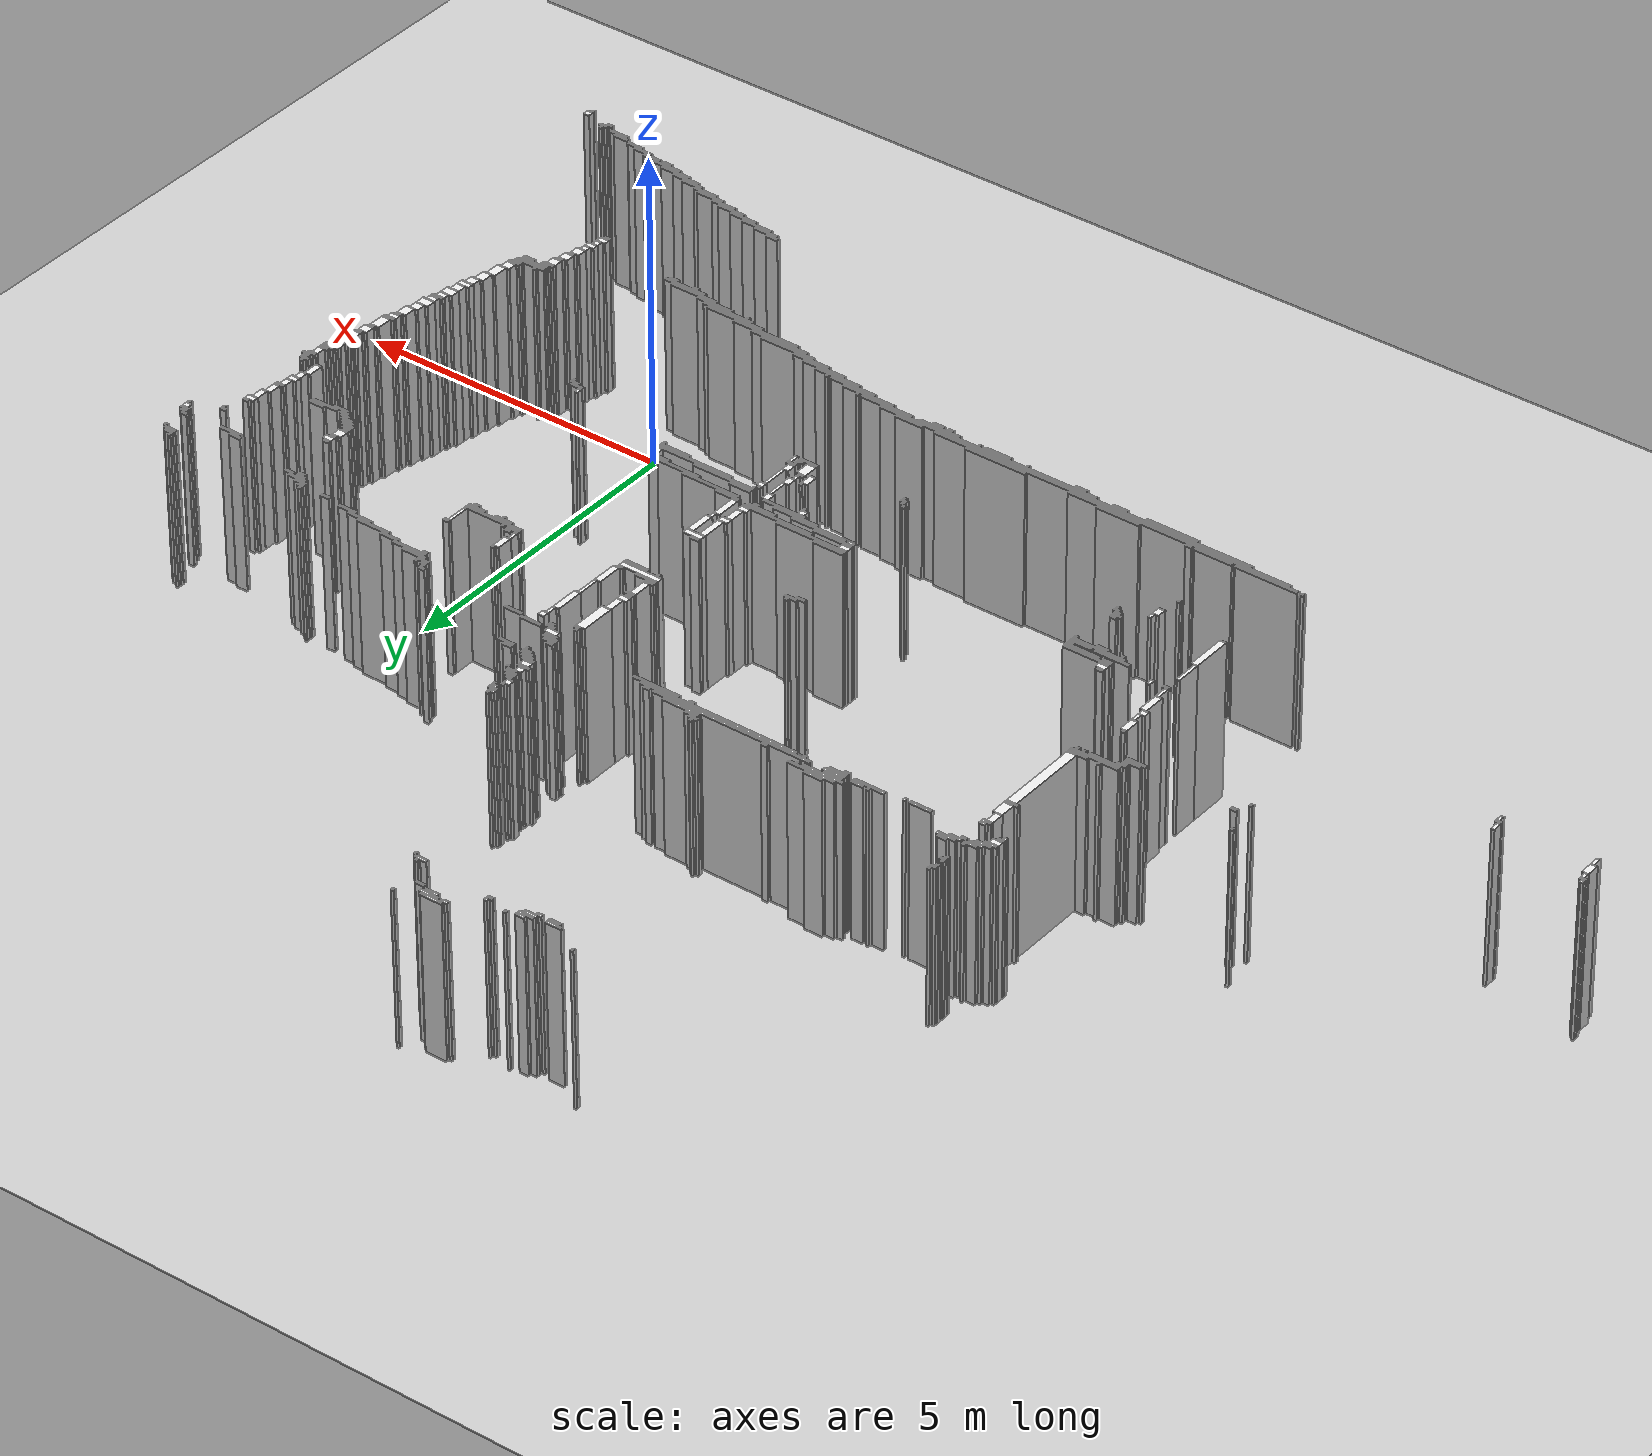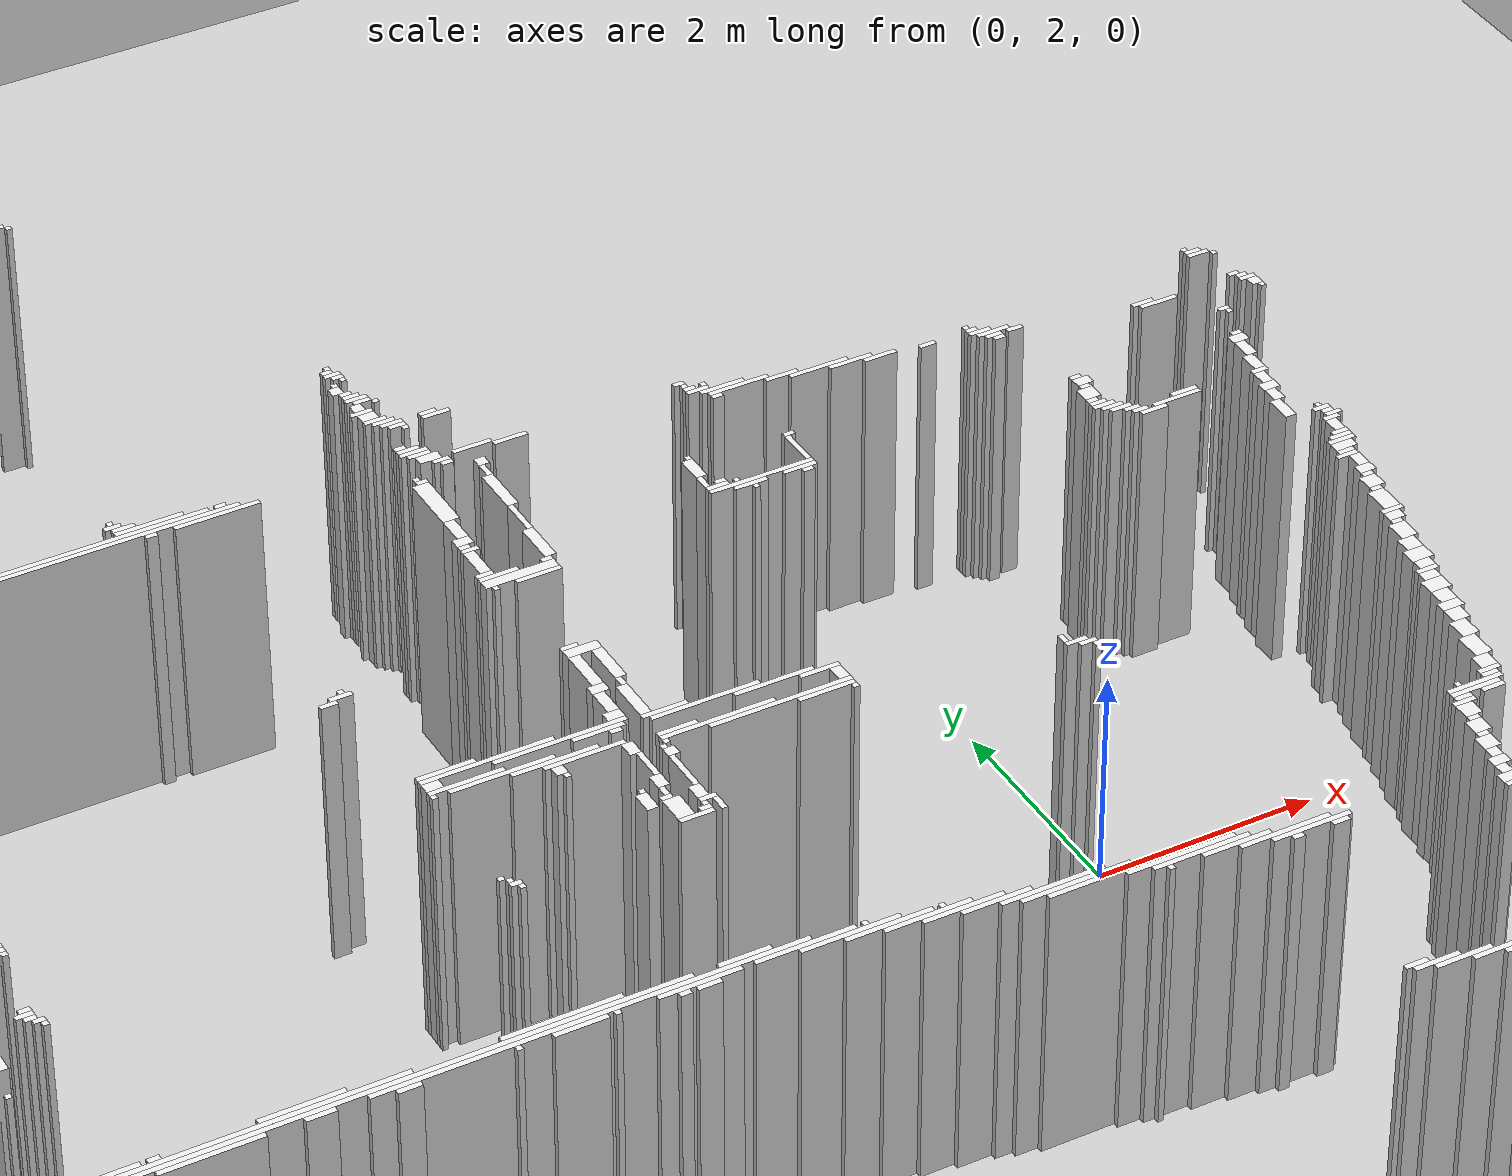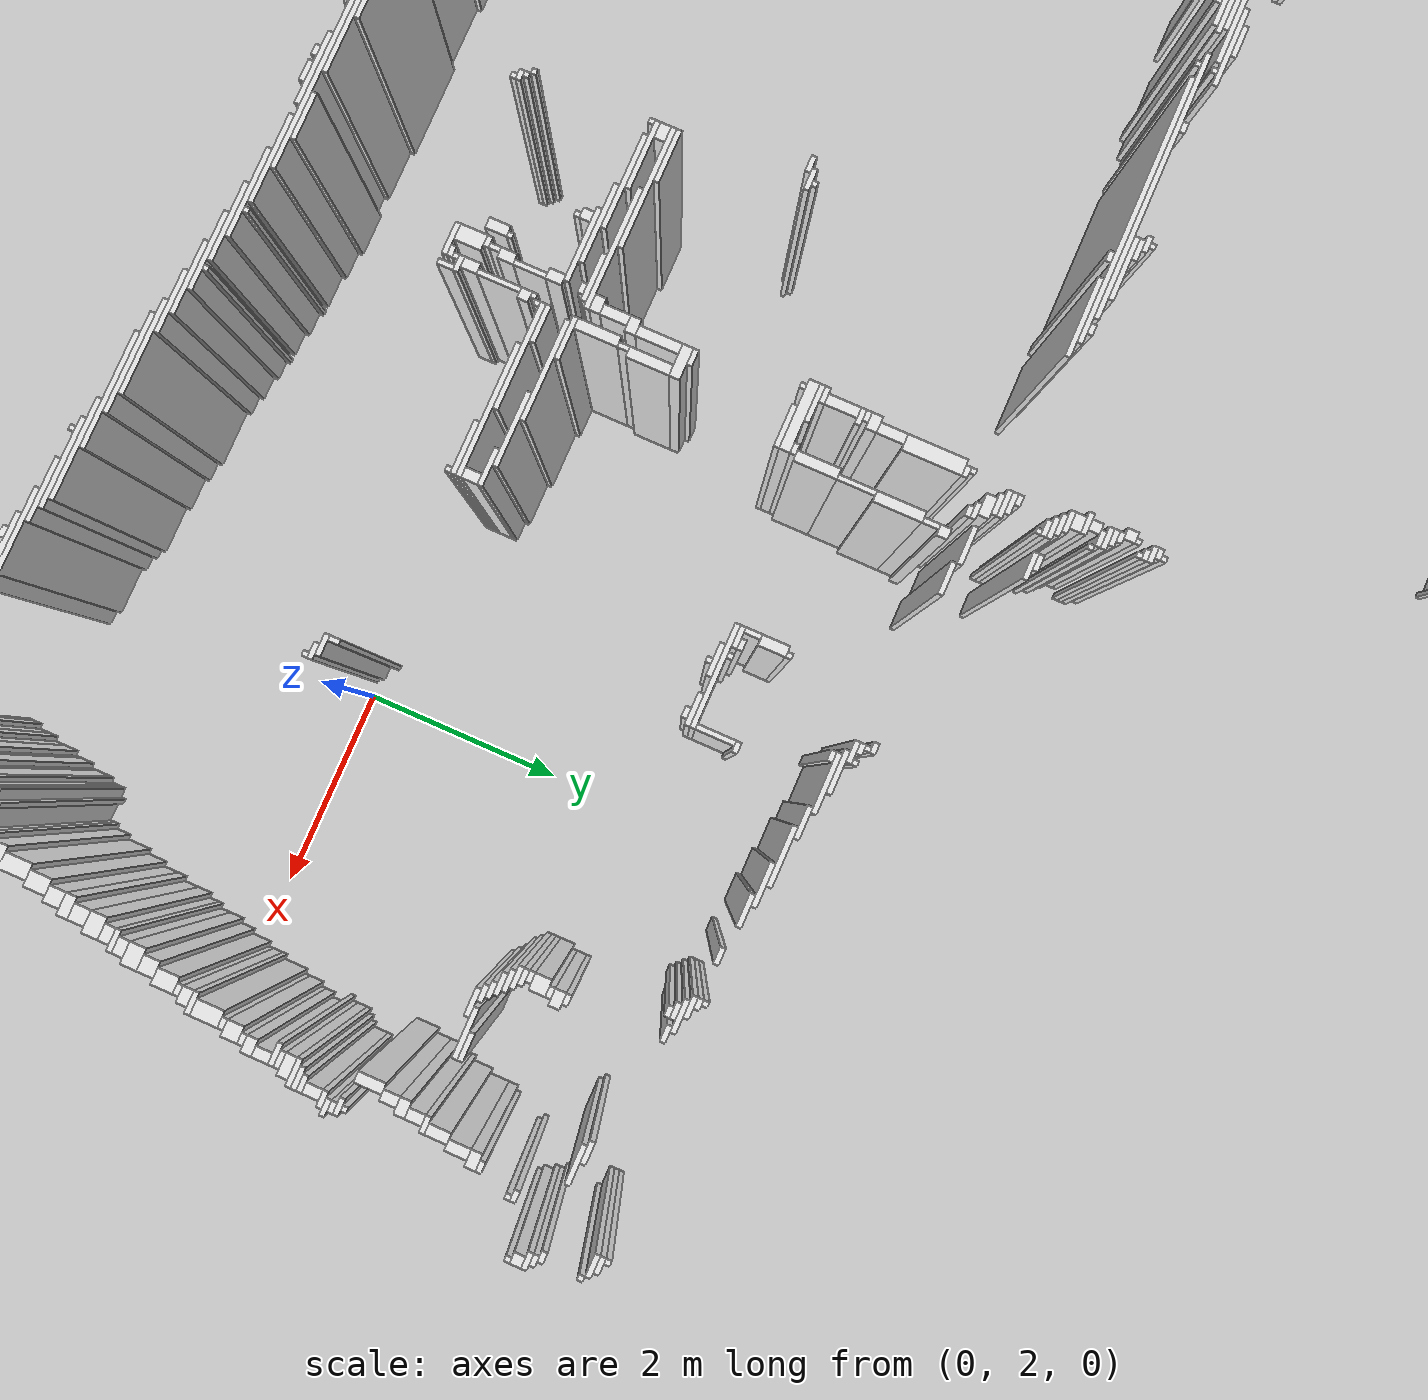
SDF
<?xml version="1.0" encoding="utf-8"?>
<sdf version="1.7">
  <world name="occupancy_map_world">
    <physics name="default_physics" default="0" type="ode">
      <max_step_size>0.001</max_step_size>
      <real_time_factor>1</real_time_factor>
      <real_time_update_rate>1000</real_time_update_rate>
    </physics>
    <light name="sun" type="directional">
      <cast_shadows>1</cast_shadows>
      <pose>0 0 10 0 0 0</pose>
      <diffuse>0.8 0.8 0.8 1</diffuse>
      <specular>0.2 0.2 0.2 1</specular>
      <attenuation>
        <range>1000</range>
        <constant>0.9</constant>
        <linear>0.01</linear>
        <quadratic>0.001</quadratic>
      </attenuation>
      <direction>-0.5 0.1 -0.9</direction>
    </light>
    <model name="ground_plane">
      <static>true</static>
      <link name="link">
        <collision name="collision">
          <geometry>
            <plane>
              <normal>0 0 1</normal>
              <size>25.380000000000003 18.84</size>
            </plane>
          </geometry>
        </collision>
        <visual name="visual">
          <geometry>
            <plane>
              <normal>0 0 1</normal>
              <size>25.380000000000003 18.84</size>
            </plane>
          </geometry>
          <material>
            <script>
              <uri>file://media/materials/scripts/gazebo.material</uri>
              <name>Gazebo/Grey</name>
            </script>
          </material>
        </visual>
      </link>
    </model>
    <model name="wall_0">
      <static>true</static>
      <pose>-5.479000000000001 12.102999999999998 1.25 0 0 0.0</pose>
      <link name="link">
        <collision name="collision">
          <geometry>
            <box>
              <size>0.05 0.05 2.5</size>
            </box>
          </geometry>
        </collision>
        <visual name="visual">
          <geometry>
            <box>
              <size>0.05 0.05 2.5</size>
            </box>
          </geometry>
          <material>
            <script>
              <uri>file://media/materials/scripts/gazebo.material</uri>
              <name>Gazebo/White</name>
            </script>
          </material>
        </visual>
      </link>
    </model>
    <model name="wall_1">
      <static>true</static>
      <pose>-5.479000000000001 1.553 1.25 0 0 0.0</pose>
      <link name="link">
        <collision name="collision">
          <geometry>
            <box>
              <size>0.05 0.05 2.5</size>
            </box>
          </geometry>
        </collision>
        <visual name="visual">
          <geometry>
            <box>
              <size>0.05 0.05 2.5</size>
            </box>
          </geometry>
          <material>
            <script>
              <uri>file://media/materials/scripts/gazebo.material</uri>
              <name>Gazebo/White</name>
            </script>
          </material>
        </visual>
      </link>
    </model>
    <model name="wall_2">
      <static>true</static>
      <pose>-5.479000000000001 -0.14700000000000024 1.25 0 0 0.0</pose>
      <link name="link">
        <collision name="collision">
          <geometry>
            <box>
              <size>0.05 0.05 2.5</size>
            </box>
          </geometry>
        </collision>
        <visual name="visual">
          <geometry>
            <box>
              <size>0.05 0.05 2.5</size>
            </box>
          </geometry>
          <material>
            <script>
              <uri>file://media/materials/scripts/gazebo.material</uri>
              <name>Gazebo/White</name>
            </script>
          </material>
        </visual>
      </link>
    </model>
    <model name="wall_3">
      <static>true</static>
      <pose>-5.979000000000001 11.953 1.25 0 0 0.0</pose>
      <link name="link">
        <collision name="collision">
          <geometry>
            <box>
              <size>0.35000000000000003 0.05 2.5</size>
            </box>
          </geometry>
        </collision>
        <visual name="visual">
          <geometry>
            <box>
              <size>0.35000000000000003 0.05 2.5</size>
            </box>
          </geometry>
          <material>
            <script>
              <uri>file://media/materials/scripts/gazebo.material</uri>
              <name>Gazebo/White</name>
            </script>
          </material>
        </visual>
      </link>
    </model>
    <model name="wall_4">
      <static>true</static>
      <pose>-6.154 11.902999999999999 1.25 0 0 0.0</pose>
      <link name="link">
        <collision name="collision">
          <geometry>
            <box>
              <size>0.1 0.05 2.5</size>
            </box>
          </geometry>
        </collision>
        <visual name="visual">
          <geometry>
            <box>
              <size>0.1 0.05 2.5</size>
            </box>
          </geometry>
          <material>
            <script>
              <uri>file://media/materials/scripts/gazebo.material</uri>
              <name>Gazebo/White</name>
            </script>
          </material>
        </visual>
      </link>
    </model>
    <model name="wall_5">
      <static>true</static>
      <pose>-5.904 11.902999999999999 1.25 0 0 0.0</pose>
      <link name="link">
        <collision name="collision">
          <geometry>
            <box>
              <size>0.30000000000000004 0.05 2.5</size>
            </box>
          </geometry>
        </collision>
        <visual name="visual">
          <geometry>
            <box>
              <size>0.30000000000000004 0.05 2.5</size>
            </box>
          </geometry>
          <material>
            <script>
              <uri>file://media/materials/scripts/gazebo.material</uri>
              <name>Gazebo/White</name>
            </script>
          </material>
        </visual>
      </link>
    </model>
    <model name="wall_6">
      <static>true</static>
      <pose>-5.904 11.852999999999998 1.25 0 0 0.0</pose>
      <link name="link">
        <collision name="collision">
          <geometry>
            <box>
              <size>0.2 0.05 2.5</size>
            </box>
          </geometry>
        </collision>
        <visual name="visual">
          <geometry>
            <box>
              <size>0.2 0.05 2.5</size>
            </box>
          </geometry>
          <material>
            <script>
              <uri>file://media/materials/scripts/gazebo.material</uri>
              <name>Gazebo/White</name>
            </script>
          </material>
        </visual>
      </link>
    </model>
    <model name="wall_7">
      <static>true</static>
      <pose>-5.679 11.803 1.25 0 0 0.0</pose>
      <link name="link">
        <collision name="collision">
          <geometry>
            <box>
              <size>0.15000000000000002 0.05 2.5</size>
            </box>
          </geometry>
        </collision>
        <visual name="visual">
          <geometry>
            <box>
              <size>0.15000000000000002 0.05 2.5</size>
            </box>
          </geometry>
          <material>
            <script>
              <uri>file://media/materials/scripts/gazebo.material</uri>
              <name>Gazebo/White</name>
            </script>
          </material>
        </visual>
      </link>
    </model>
    <model name="wall_8">
      <static>true</static>
      <pose>-8.029 11.703 1.25 0 0 0.0</pose>
      <link name="link">
        <collision name="collision">
          <geometry>
            <box>
              <size>0.05 0.05 2.5</size>
            </box>
          </geometry>
        </collision>
        <visual name="visual">
          <geometry>
            <box>
              <size>0.05 0.05 2.5</size>
            </box>
          </geometry>
          <material>
            <script>
              <uri>file://media/materials/scripts/gazebo.material</uri>
              <name>Gazebo/White</name>
            </script>
          </material>
        </visual>
      </link>
    </model>
    <model name="wall_9">
      <static>true</static>
      <pose>-6.879000000000001 11.603000000000002 1.25 0 0 0.0</pose>
      <link name="link">
        <collision name="collision">
          <geometry>
            <box>
              <size>0.05 0.05 2.5</size>
            </box>
          </geometry>
        </collision>
        <visual name="visual">
          <geometry>
            <box>
              <size>0.05 0.05 2.5</size>
            </box>
          </geometry>
          <material>
            <script>
              <uri>file://media/materials/scripts/gazebo.material</uri>
              <name>Gazebo/White</name>
            </script>
          </material>
        </visual>
      </link>
    </model>
    <model name="wall_10">
      <static>true</static>
      <pose>-7.079000000000001 11.553 1.25 0 0 0.0</pose>
      <link name="link">
        <collision name="collision">
          <geometry>
            <box>
              <size>0.15000000000000002 0.05 2.5</size>
            </box>
          </geometry>
        </collision>
        <visual name="visual">
          <geometry>
            <box>
              <size>0.15000000000000002 0.05 2.5</size>
            </box>
          </geometry>
          <material>
            <script>
              <uri>file://media/materials/scripts/gazebo.material</uri>
              <name>Gazebo/White</name>
            </script>
          </material>
        </visual>
      </link>
    </model>
    <model name="wall_11">
      <static>true</static>
      <pose>-6.529 11.553 1.25 0 0 0.0</pose>
      <link name="link">
        <collision name="collision">
          <geometry>
            <box>
              <size>0.05 0.05 2.5</size>
            </box>
          </geometry>
        </collision>
        <visual name="visual">
          <geometry>
            <box>
              <size>0.05 0.05 2.5</size>
            </box>
          </geometry>
          <material>
            <script>
              <uri>file://media/materials/scripts/gazebo.material</uri>
              <name>Gazebo/White</name>
            </script>
          </material>
        </visual>
      </link>
    </model>
    <model name="wall_12">
      <static>true</static>
      <pose>-7.129000000000001 11.503 1.25 0 0 0.0</pose>
      <link name="link">
        <collision name="collision">
          <geometry>
            <box>
              <size>0.25 0.05 2.5</size>
            </box>
          </geometry>
        </collision>
        <visual name="visual">
          <geometry>
            <box>
              <size>0.25 0.05 2.5</size>
            </box>
          </geometry>
          <material>
            <script>
              <uri>file://media/materials/scripts/gazebo.material</uri>
              <name>Gazebo/White</name>
            </script>
          </material>
        </visual>
      </link>
    </model>
    <model name="wall_13">
      <static>true</static>
      <pose>-6.554 11.503 1.25 0 0 0.0</pose>
      <link name="link">
        <collision name="collision">
          <geometry>
            <box>
              <size>0.1 0.05 2.5</size>
            </box>
          </geometry>
        </collision>
        <visual name="visual">
          <geometry>
            <box>
              <size>0.1 0.05 2.5</size>
            </box>
          </geometry>
          <material>
            <script>
              <uri>file://media/materials/scripts/gazebo.material</uri>
              <name>Gazebo/White</name>
            </script>
          </material>
        </visual>
      </link>
    </model>
    <model name="wall_14">
      <static>true</static>
      <pose>-7.529 11.453 1.25 0 0 0.0</pose>
      <link name="link">
        <collision name="collision">
          <geometry>
            <box>
              <size>0.25 0.05 2.5</size>
            </box>
          </geometry>
        </collision>
        <visual name="visual">
          <geometry>
            <box>
              <size>0.25 0.05 2.5</size>
            </box>
          </geometry>
          <material>
            <script>
              <uri>file://media/materials/scripts/gazebo.material</uri>
              <name>Gazebo/White</name>
            </script>
          </material>
        </visual>
      </link>
    </model>
    <model name="wall_15">
      <static>true</static>
      <pose>-7.154 11.453 1.25 0 0 0.0</pose>
      <link name="link">
        <collision name="collision">
          <geometry>
            <box>
              <size>0.2 0.05 2.5</size>
            </box>
          </geometry>
        </collision>
        <visual name="visual">
          <geometry>
            <box>
              <size>0.2 0.05 2.5</size>
            </box>
          </geometry>
          <material>
            <script>
              <uri>file://media/materials/scripts/gazebo.material</uri>
              <name>Gazebo/White</name>
            </script>
          </material>
        </visual>
      </link>
    </model>
    <model name="wall_16">
      <static>true</static>
      <pose>-7.154 -0.14700000000000024 1.25 0 0 0.0</pose>
      <link name="link">
        <collision name="collision">
          <geometry>
            <box>
              <size>0.2 0.05 2.5</size>
            </box>
          </geometry>
        </collision>
        <visual name="visual">
          <geometry>
            <box>
              <size>0.2 0.05 2.5</size>
            </box>
          </geometry>
          <material>
            <script>
              <uri>file://media/materials/scripts/gazebo.material</uri>
              <name>Gazebo/White</name>
            </script>
          </material>
        </visual>
      </link>
    </model>
    <model name="wall_17">
      <static>true</static>
      <pose>-5.329000000000001 11.453 1.25 0 0 0.0</pose>
      <link name="link">
        <collision name="collision">
          <geometry>
            <box>
              <size>0.05 0.05 2.5</size>
            </box>
          </geometry>
        </collision>
        <visual name="visual">
          <geometry>
            <box>
              <size>0.05 0.05 2.5</size>
            </box>
          </geometry>
          <material>
            <script>
              <uri>file://media/materials/scripts/gazebo.material</uri>
              <name>Gazebo/White</name>
            </script>
          </material>
        </visual>
      </link>
    </model>
    <model name="wall_18">
      <static>true</static>
      <pose>-7.504000000000001 11.402999999999999 1.25 0 0 0.0</pose>
      <link name="link">
        <collision name="collision">
          <geometry>
            <box>
              <size>0.2 0.05 2.5</size>
            </box>
          </geometry>
        </collision>
        <visual name="visual">
          <geometry>
            <box>
              <size>0.2 0.05 2.5</size>
            </box>
          </geometry>
          <material>
            <script>
              <uri>file://media/materials/scripts/gazebo.material</uri>
              <name>Gazebo/White</name>
            </script>
          </material>
        </visual>
      </link>
    </model>
    <model name="wall_19">
      <static>true</static>
      <pose>-7.254000000000001 11.402999999999999 1.25 0 0 0.0</pose>
      <link name="link">
        <collision name="collision">
          <geometry>
            <box>
              <size>0.1 0.05 2.5</size>
            </box>
          </geometry>
        </collision>
        <visual name="visual">
          <geometry>
            <box>
              <size>0.1 0.05 2.5</size>
            </box>
          </geometry>
          <material>
            <script>
              <uri>file://media/materials/scripts/gazebo.material</uri>
              <name>Gazebo/White</name>
            </script>
          </material>
        </visual>
      </link>
    </model>
    <model name="wall_20">
      <static>true</static>
      <pose>-5.354000000000001 11.402999999999999 1.25 0 0 0.0</pose>
      <link name="link">
        <collision name="collision">
          <geometry>
            <box>
              <size>0.2 0.05 2.5</size>
            </box>
          </geometry>
        </collision>
        <visual name="visual">
          <geometry>
            <box>
              <size>0.2 0.05 2.5</size>
            </box>
          </geometry>
          <material>
            <script>
              <uri>file://media/materials/scripts/gazebo.material</uri>
              <name>Gazebo/White</name>
            </script>
          </material>
        </visual>
      </link>
    </model>
    <model name="wall_21">
      <static>true</static>
      <pose>-5.229000000000001 11.353000000000002 1.25 0 0 0.0</pose>
      <link name="link">
        <collision name="collision">
          <geometry>
            <box>
              <size>0.05 0.05 2.5</size>
            </box>
          </geometry>
        </collision>
        <visual name="visual">
          <geometry>
            <box>
              <size>0.05 0.05 2.5</size>
            </box>
          </geometry>
          <material>
            <script>
              <uri>file://media/materials/scripts/gazebo.material</uri>
              <name>Gazebo/White</name>
            </script>
          </material>
        </visual>
      </link>
    </model>
    <model name="wall_22">
      <static>true</static>
      <pose>-3.779 8.152999999999999 1.25 0 0 0.0</pose>
      <link name="link">
        <collision name="collision">
          <geometry>
            <box>
              <size>0.05 0.05 2.5</size>
            </box>
          </geometry>
        </collision>
        <visual name="visual">
          <geometry>
            <box>
              <size>0.05 0.05 2.5</size>
            </box>
          </geometry>
          <material>
            <script>
              <uri>file://media/materials/scripts/gazebo.material</uri>
              <name>Gazebo/White</name>
            </script>
          </material>
        </visual>
      </link>
    </model>
    <model name="wall_23">
      <static>true</static>
      <pose>-3.779 1.6529999999999996 1.25 0 0 0.0</pose>
      <link name="link">
        <collision name="collision">
          <geometry>
            <box>
              <size>0.05 0.05 2.5</size>
            </box>
          </geometry>
        </collision>
        <visual name="visual">
          <geometry>
            <box>
              <size>0.05 0.05 2.5</size>
            </box>
          </geometry>
          <material>
            <script>
              <uri>file://media/materials/scripts/gazebo.material</uri>
              <name>Gazebo/White</name>
            </script>
          </material>
        </visual>
      </link>
    </model>
    <model name="wall_24">
      <static>true</static>
      <pose>-3.8040000000000003 8.103000000000002 1.25 0 0 0.0</pose>
      <link name="link">
        <collision name="collision">
          <geometry>
            <box>
              <size>0.1 0.05 2.5</size>
            </box>
          </geometry>
        </collision>
        <visual name="visual">
          <geometry>
            <box>
              <size>0.1 0.05 2.5</size>
            </box>
          </geometry>
          <material>
            <script>
              <uri>file://media/materials/scripts/gazebo.material</uri>
              <name>Gazebo/White</name>
            </script>
          </material>
        </visual>
      </link>
    </model>
    <model name="wall_25">
      <static>true</static>
      <pose>-3.8040000000000003 7.753000000000001 1.25 0 0 0.0</pose>
      <link name="link">
        <collision name="collision">
          <geometry>
            <box>
              <size>0.1 0.05 2.5</size>
            </box>
          </geometry>
        </collision>
        <visual name="visual">
          <geometry>
            <box>
              <size>0.1 0.05 2.5</size>
            </box>
          </geometry>
          <material>
            <script>
              <uri>file://media/materials/scripts/gazebo.material</uri>
              <name>Gazebo/White</name>
            </script>
          </material>
        </visual>
      </link>
    </model>
    <model name="wall_26">
      <static>true</static>
      <pose>-3.8040000000000003 7.528 1.25 0 0 0.0</pose>
      <link name="link">
        <collision name="collision">
          <geometry>
            <box>
              <size>0.1 0.1 2.5</size>
            </box>
          </geometry>
        </collision>
        <visual name="visual">
          <geometry>
            <box>
              <size>0.1 0.1 2.5</size>
            </box>
          </geometry>
          <material>
            <script>
              <uri>file://media/materials/scripts/gazebo.material</uri>
              <name>Gazebo/White</name>
            </script>
          </material>
        </visual>
      </link>
    </model>
    <model name="wall_27">
      <static>true</static>
      <pose>-3.8040000000000003 6.353000000000001 1.25 0 0 0.0</pose>
      <link name="link">
        <collision name="collision">
          <geometry>
            <box>
              <size>0.1 0.05 2.5</size>
            </box>
          </geometry>
        </collision>
        <visual name="visual">
          <geometry>
            <box>
              <size>0.1 0.05 2.5</size>
            </box>
          </geometry>
          <material>
            <script>
              <uri>file://media/materials/scripts/gazebo.material</uri>
              <name>Gazebo/White</name>
            </script>
          </material>
        </visual>
      </link>
    </model>
    <model name="wall_28">
      <static>true</static>
      <pose>-3.8040000000000003 3.5279999999999996 1.25 0 0 0.0</pose>
      <link name="link">
        <collision name="collision">
          <geometry>
            <box>
              <size>0.1 0.4 2.5</size>
            </box>
          </geometry>
        </collision>
        <visual name="visual">
          <geometry>
            <box>
              <size>0.1 0.4 2.5</size>
            </box>
          </geometry>
          <material>
            <script>
              <uri>file://media/materials/scripts/gazebo.material</uri>
              <name>Gazebo/White</name>
            </script>
          </material>
        </visual>
      </link>
    </model>
    <model name="wall_29">
      <static>true</static>
      <pose>-3.8040000000000003 1.6029999999999998 1.25 0 0 0.0</pose>
      <link name="link">
        <collision name="collision">
          <geometry>
            <box>
              <size>0.1 0.05 2.5</size>
            </box>
          </geometry>
        </collision>
        <visual name="visual">
          <geometry>
            <box>
              <size>0.1 0.05 2.5</size>
            </box>
          </geometry>
          <material>
            <script>
              <uri>file://media/materials/scripts/gazebo.material</uri>
              <name>Gazebo/White</name>
            </script>
          </material>
        </visual>
      </link>
    </model>
    <model name="wall_30">
      <static>true</static>
      <pose>-3.779 8.053 1.25 0 0 0.0</pose>
      <link name="link">
        <collision name="collision">
          <geometry>
            <box>
              <size>0.15000000000000002 0.05 2.5</size>
            </box>
          </geometry>
        </collision>
        <visual name="visual">
          <geometry>
            <box>
              <size>0.15000000000000002 0.05 2.5</size>
            </box>
          </geometry>
          <material>
            <script>
              <uri>file://media/materials/scripts/gazebo.material</uri>
              <name>Gazebo/White</name>
            </script>
          </material>
        </visual>
      </link>
    </model>
    <model name="wall_31">
      <static>true</static>
      <pose>-3.779 7.703 1.25 0 0 0.0</pose>
      <link name="link">
        <collision name="collision">
          <geometry>
            <box>
              <size>0.15000000000000002 0.05 2.5</size>
            </box>
          </geometry>
        </collision>
        <visual name="visual">
          <geometry>
            <box>
              <size>0.15000000000000002 0.05 2.5</size>
            </box>
          </geometry>
          <material>
            <script>
              <uri>file://media/materials/scripts/gazebo.material</uri>
              <name>Gazebo/White</name>
            </script>
          </material>
        </visual>
      </link>
    </model>
    <model name="wall_32">
      <static>true</static>
      <pose>-3.779 7.378000000000001 1.25 0 0 0.0</pose>
      <link name="link">
        <collision name="collision">
          <geometry>
            <box>
              <size>0.15000000000000002 0.1 2.5</size>
            </box>
          </geometry>
        </collision>
        <visual name="visual">
          <geometry>
            <box>
              <size>0.15000000000000002 0.1 2.5</size>
            </box>
          </geometry>
          <material>
            <script>
              <uri>file://media/materials/scripts/gazebo.material</uri>
              <name>Gazebo/White</name>
            </script>
          </material>
        </visual>
      </link>
    </model>
    <model name="wall_33">
      <static>true</static>
      <pose>-3.779 3.8530000000000006 1.25 0 0 0.0</pose>
      <link name="link">
        <collision name="collision">
          <geometry>
            <box>
              <size>0.15000000000000002 0.05 2.5</size>
            </box>
          </geometry>
        </collision>
        <visual name="visual">
          <geometry>
            <box>
              <size>0.15000000000000002 0.05 2.5</size>
            </box>
          </geometry>
          <material>
            <script>
              <uri>file://media/materials/scripts/gazebo.material</uri>
              <name>Gazebo/White</name>
            </script>
          </material>
        </visual>
      </link>
    </model>
    <model name="wall_34">
      <static>true</static>
      <pose>-3.7540000000000013 8.003 1.25 0 0 0.0</pose>
      <link name="link">
        <collision name="collision">
          <geometry>
            <box>
              <size>0.1 0.05 2.5</size>
            </box>
          </geometry>
        </collision>
        <visual name="visual">
          <geometry>
            <box>
              <size>0.1 0.05 2.5</size>
            </box>
          </geometry>
          <material>
            <script>
              <uri>file://media/materials/scripts/gazebo.material</uri>
              <name>Gazebo/White</name>
            </script>
          </material>
        </visual>
      </link>
    </model>
    <model name="wall_35">
      <static>true</static>
      <pose>-3.7540000000000013 6.853000000000001 1.25 0 0 0.0</pose>
      <link name="link">
        <collision name="collision">
          <geometry>
            <box>
              <size>0.1 0.05 2.5</size>
            </box>
          </geometry>
        </collision>
        <visual name="visual">
          <geometry>
            <box>
              <size>0.1 0.05 2.5</size>
            </box>
          </geometry>
          <material>
            <script>
              <uri>file://media/materials/scripts/gazebo.material</uri>
              <name>Gazebo/White</name>
            </script>
          </material>
        </visual>
      </link>
    </model>
    <model name="wall_36">
      <static>true</static>
      <pose>-3.7540000000000013 1.803 1.25 0 0 0.0</pose>
      <link name="link">
        <collision name="collision">
          <geometry>
            <box>
              <size>0.1 0.15000000000000002 2.5</size>
            </box>
          </geometry>
        </collision>
        <visual name="visual">
          <geometry>
            <box>
              <size>0.1 0.15000000000000002 2.5</size>
            </box>
          </geometry>
          <material>
            <script>
              <uri>file://media/materials/scripts/gazebo.material</uri>
              <name>Gazebo/White</name>
            </script>
          </material>
        </visual>
      </link>
    </model>
    <model name="wall_37">
      <static>true</static>
      <pose>-3.729000000000001 7.953 1.25 0 0 0.0</pose>
      <link name="link">
        <collision name="collision">
          <geometry>
            <box>
              <size>0.05 0.05 2.5</size>
            </box>
          </geometry>
        </collision>
        <visual name="visual">
          <geometry>
            <box>
              <size>0.05 0.05 2.5</size>
            </box>
          </geometry>
          <material>
            <script>
              <uri>file://media/materials/scripts/gazebo.material</uri>
              <name>Gazebo/White</name>
            </script>
          </material>
        </visual>
      </link>
    </model>
    <model name="wall_38">
      <static>true</static>
      <pose>-3.729000000000001 2.4029999999999996 1.25 0 0 0.0</pose>
      <link name="link">
        <collision name="collision">
          <geometry>
            <box>
              <size>0.05 0.05 2.5</size>
            </box>
          </geometry>
        </collision>
        <visual name="visual">
          <geometry>
            <box>
              <size>0.05 0.05 2.5</size>
            </box>
          </geometry>
          <material>
            <script>
              <uri>file://media/materials/scripts/gazebo.material</uri>
              <name>Gazebo/White</name>
            </script>
          </material>
        </visual>
      </link>
    </model>
    <model name="wall_39">
      <static>true</static>
      <pose>-3.729000000000001 2.0780000000000003 1.25 0 0 0.0</pose>
      <link name="link">
        <collision name="collision">
          <geometry>
            <box>
              <size>0.05 0.4 2.5</size>
            </box>
          </geometry>
        </collision>
        <visual name="visual">
          <geometry>
            <box>
              <size>0.05 0.4 2.5</size>
            </box>
          </geometry>
          <material>
            <script>
              <uri>file://media/materials/scripts/gazebo.material</uri>
              <name>Gazebo/White</name>
            </script>
          </material>
        </visual>
      </link>
    </model>
    <model name="wall_40">
      <static>true</static>
      <pose>-3.8290000000000006 7.903 1.25 0 0 0.0</pose>
      <link name="link">
        <collision name="collision">
          <geometry>
            <box>
              <size>0.05 0.05 2.5</size>
            </box>
          </geometry>
        </collision>
        <visual name="visual">
          <geometry>
            <box>
              <size>0.05 0.05 2.5</size>
            </box>
          </geometry>
          <material>
            <script>
              <uri>file://media/materials/scripts/gazebo.material</uri>
              <name>Gazebo/White</name>
            </script>
          </material>
        </visual>
      </link>
    </model>
    <model name="wall_41">
      <static>true</static>
      <pose>-3.8290000000000006 6.403 1.25 0 0 0.0</pose>
      <link name="link">
        <collision name="collision">
          <geometry>
            <box>
              <size>0.05 0.05 2.5</size>
            </box>
          </geometry>
        </collision>
        <visual name="visual">
          <geometry>
            <box>
              <size>0.05 0.05 2.5</size>
            </box>
          </geometry>
          <material>
            <script>
              <uri>file://media/materials/scripts/gazebo.material</uri>
              <name>Gazebo/White</name>
            </script>
          </material>
        </visual>
      </link>
    </model>
    <model name="wall_42">
      <static>true</static>
      <pose>-3.854000000000001 7.828 1.25 0 0 0.0</pose>
      <link name="link">
        <collision name="collision">
          <geometry>
            <box>
              <size>0.1 0.1 2.5</size>
            </box>
          </geometry>
        </collision>
        <visual name="visual">
          <geometry>
            <box>
              <size>0.1 0.1 2.5</size>
            </box>
          </geometry>
          <material>
            <script>
              <uri>file://media/materials/scripts/gazebo.material</uri>
              <name>Gazebo/White</name>
            </script>
          </material>
        </visual>
      </link>
    </model>
    <model name="wall_43">
      <static>true</static>
      <pose>-3.854000000000001 5.653 1.25 0 0 0.0</pose>
      <link name="link">
        <collision name="collision">
          <geometry>
            <box>
              <size>0.1 0.25 2.5</size>
            </box>
          </geometry>
        </collision>
        <visual name="visual">
          <geometry>
            <box>
              <size>0.1 0.25 2.5</size>
            </box>
          </geometry>
          <material>
            <script>
              <uri>file://media/materials/scripts/gazebo.material</uri>
              <name>Gazebo/White</name>
            </script>
          </material>
        </visual>
      </link>
    </model>
    <model name="wall_44">
      <static>true</static>
      <pose>-3.854000000000001 3.1029999999999998 1.25 0 0 0.0</pose>
      <link name="link">
        <collision name="collision">
          <geometry>
            <box>
              <size>0.1 0.25 2.5</size>
            </box>
          </geometry>
        </collision>
        <visual name="visual">
          <geometry>
            <box>
              <size>0.1 0.25 2.5</size>
            </box>
          </geometry>
          <material>
            <script>
              <uri>file://media/materials/scripts/gazebo.material</uri>
              <name>Gazebo/White</name>
            </script>
          </material>
        </visual>
      </link>
    </model>
    <model name="wall_45">
      <static>true</static>
      <pose>-10.529 7.703 1.25 0 0 0.0</pose>
      <link name="link">
        <collision name="collision">
          <geometry>
            <box>
              <size>0.05 0.05 2.5</size>
            </box>
          </geometry>
        </collision>
        <visual name="visual">
          <geometry>
            <box>
              <size>0.05 0.05 2.5</size>
            </box>
          </geometry>
          <material>
            <script>
              <uri>file://media/materials/scripts/gazebo.material</uri>
              <name>Gazebo/White</name>
            </script>
          </material>
        </visual>
      </link>
    </model>
    <model name="wall_46">
      <static>true</static>
      <pose>-10.529 4.553 1.25 0 0 0.0</pose>
      <link name="link">
        <collision name="collision">
          <geometry>
            <box>
              <size>0.05 0.05 2.5</size>
            </box>
          </geometry>
        </collision>
        <visual name="visual">
          <geometry>
            <box>
              <size>0.05 0.05 2.5</size>
            </box>
          </geometry>
          <material>
            <script>
              <uri>file://media/materials/scripts/gazebo.material</uri>
              <name>Gazebo/White</name>
            </script>
          </material>
        </visual>
      </link>
    </model>
    <model name="wall_47">
      <static>true</static>
      <pose>-10.554000000000002 7.653 1.25 0 0 0.0</pose>
      <link name="link">
        <collision name="collision">
          <geometry>
            <box>
              <size>0.1 0.05 2.5</size>
            </box>
          </geometry>
        </collision>
        <visual name="visual">
          <geometry>
            <box>
              <size>0.1 0.05 2.5</size>
            </box>
          </geometry>
          <material>
            <script>
              <uri>file://media/materials/scripts/gazebo.material</uri>
              <name>Gazebo/White</name>
            </script>
          </material>
        </visual>
      </link>
    </model>
    <model name="wall_48">
      <static>true</static>
      <pose>-10.554000000000002 7.453 1.25 0 0 0.0</pose>
      <link name="link">
        <collision name="collision">
          <geometry>
            <box>
              <size>0.1 0.05 2.5</size>
            </box>
          </geometry>
        </collision>
        <visual name="visual">
          <geometry>
            <box>
              <size>0.1 0.05 2.5</size>
            </box>
          </geometry>
          <material>
            <script>
              <uri>file://media/materials/scripts/gazebo.material</uri>
              <name>Gazebo/White</name>
            </script>
          </material>
        </visual>
      </link>
    </model>
    <model name="wall_49">
      <static>true</static>
      <pose>-10.554000000000002 6.378000000000001 1.25 0 0 0.0</pose>
      <link name="link">
        <collision name="collision">
          <geometry>
            <box>
              <size>0.1 0.2 2.5</size>
            </box>
          </geometry>
        </collision>
        <visual name="visual">
          <geometry>
            <box>
              <size>0.1 0.2 2.5</size>
            </box>
          </geometry>
          <material>
            <script>
              <uri>file://media/materials/scripts/gazebo.material</uri>
              <name>Gazebo/White</name>
            </script>
          </material>
        </visual>
      </link>
    </model>
    <model name="wall_50">
      <static>true</static>
      <pose>-3.7540000000000013 7.653 1.25 0 0 0.0</pose>
      <link name="link">
        <collision name="collision">
          <geometry>
            <box>
              <size>0.2 0.05 2.5</size>
            </box>
          </geometry>
        </collision>
        <visual name="visual">
          <geometry>
            <box>
              <size>0.2 0.05 2.5</size>
            </box>
          </geometry>
          <material>
            <script>
              <uri>file://media/materials/scripts/gazebo.material</uri>
              <name>Gazebo/White</name>
            </script>
          </material>
        </visual>
      </link>
    </model>
    <model name="wall_51">
      <static>true</static>
      <pose>-3.7540000000000013 7.303 1.25 0 0 0.0</pose>
      <link name="link">
        <collision name="collision">
          <geometry>
            <box>
              <size>0.2 0.05 2.5</size>
            </box>
          </geometry>
        </collision>
        <visual name="visual">
          <geometry>
            <box>
              <size>0.2 0.05 2.5</size>
            </box>
          </geometry>
          <material>
            <script>
              <uri>file://media/materials/scripts/gazebo.material</uri>
              <name>Gazebo/White</name>
            </script>
          </material>
        </visual>
      </link>
    </model>
    <model name="wall_52">
      <static>true</static>
      <pose>-10.579 7.603000000000001 1.25 0 0 0.0</pose>
      <link name="link">
        <collision name="collision">
          <geometry>
            <box>
              <size>0.05 0.05 2.5</size>
            </box>
          </geometry>
        </collision>
        <visual name="visual">
          <geometry>
            <box>
              <size>0.05 0.05 2.5</size>
            </box>
          </geometry>
          <material>
            <script>
              <uri>file://media/materials/scripts/gazebo.material</uri>
              <name>Gazebo/White</name>
            </script>
          </material>
        </visual>
      </link>
    </model>
    <model name="wall_53">
      <static>true</static>
      <pose>-10.579 7.503000000000001 1.25 0 0 0.0</pose>
      <link name="link">
        <collision name="collision">
          <geometry>
            <box>
              <size>0.05 0.05 2.5</size>
            </box>
          </geometry>
        </collision>
        <visual name="visual">
          <geometry>
            <box>
              <size>0.05 0.05 2.5</size>
            </box>
          </geometry>
          <material>
            <script>
              <uri>file://media/materials/scripts/gazebo.material</uri>
              <name>Gazebo/White</name>
            </script>
          </material>
        </visual>
      </link>
    </model>
    <model name="wall_54">
      <static>true</static>
      <pose>-10.579 7.403 1.25 0 0 0.0</pose>
      <link name="link">
        <collision name="collision">
          <geometry>
            <box>
              <size>0.05 0.05 2.5</size>
            </box>
          </geometry>
        </collision>
        <visual name="visual">
          <geometry>
            <box>
              <size>0.05 0.05 2.5</size>
            </box>
          </geometry>
          <material>
            <script>
              <uri>file://media/materials/scripts/gazebo.material</uri>
              <name>Gazebo/White</name>
            </script>
          </material>
        </visual>
      </link>
    </model>
    <model name="wall_55">
      <static>true</static>
      <pose>-10.579 7.053 1.25 0 0 0.0</pose>
      <link name="link">
        <collision name="collision">
          <geometry>
            <box>
              <size>0.05 0.05 2.5</size>
            </box>
          </geometry>
        </collision>
        <visual name="visual">
          <geometry>
            <box>
              <size>0.05 0.05 2.5</size>
            </box>
          </geometry>
          <material>
            <script>
              <uri>file://media/materials/scripts/gazebo.material</uri>
              <name>Gazebo/White</name>
            </script>
          </material>
        </visual>
      </link>
    </model>
    <model name="wall_56">
      <static>true</static>
      <pose>-3.729000000000001 7.603000000000001 1.25 0 0 0.0</pose>
      <link name="link">
        <collision name="collision">
          <geometry>
            <box>
              <size>0.15000000000000002 0.05 2.5</size>
            </box>
          </geometry>
        </collision>
        <visual name="visual">
          <geometry>
            <box>
              <size>0.15000000000000002 0.05 2.5</size>
            </box>
          </geometry>
          <material>
            <script>
              <uri>file://media/materials/scripts/gazebo.material</uri>
              <name>Gazebo/White</name>
            </script>
          </material>
        </visual>
      </link>
    </model>
    <model name="wall_57">
      <static>true</static>
      <pose>-3.729000000000001 1.7030000000000003 1.25 0 0 0.0</pose>
      <link name="link">
        <collision name="collision">
          <geometry>
            <box>
              <size>0.15000000000000002 0.05 2.5</size>
            </box>
          </geometry>
        </collision>
        <visual name="visual">
          <geometry>
            <box>
              <size>0.15000000000000002 0.05 2.5</size>
            </box>
          </geometry>
          <material>
            <script>
              <uri>file://media/materials/scripts/gazebo.material</uri>
              <name>Gazebo/White</name>
            </script>
          </material>
        </visual>
      </link>
    </model>
    <model name="wall_58">
      <static>true</static>
      <pose>-3.6290000000000013 7.553 1.25 0 0 0.0</pose>
      <link name="link">
        <collision name="collision">
          <geometry>
            <box>
              <size>0.05 0.05 2.5</size>
            </box>
          </geometry>
        </collision>
        <visual name="visual">
          <geometry>
            <box>
              <size>0.05 0.05 2.5</size>
            </box>
          </geometry>
          <material>
            <script>
              <uri>file://media/materials/scripts/gazebo.material</uri>
              <name>Gazebo/White</name>
            </script>
          </material>
        </visual>
      </link>
    </model>
    <model name="wall_59">
      <static>true</static>
      <pose>-3.6290000000000013 3.2779999999999996 1.25 0 0 0.0</pose>
      <link name="link">
        <collision name="collision">
          <geometry>
            <box>
              <size>0.05 0.1 2.5</size>
            </box>
          </geometry>
        </collision>
        <visual name="visual">
          <geometry>
            <box>
              <size>0.05 0.1 2.5</size>
            </box>
          </geometry>
          <material>
            <script>
              <uri>file://media/materials/scripts/gazebo.material</uri>
              <name>Gazebo/White</name>
            </script>
          </material>
        </visual>
      </link>
    </model>
    <model name="wall_60">
      <static>true</static>
      <pose>-3.8040000000000003 7.453 1.25 0 0 0.0</pose>
      <link name="link">
        <collision name="collision">
          <geometry>
            <box>
              <size>0.2 0.05 2.5</size>
            </box>
          </geometry>
        </collision>
        <visual name="visual">
          <geometry>
            <box>
              <size>0.2 0.05 2.5</size>
            </box>
          </geometry>
          <material>
            <script>
              <uri>file://media/materials/scripts/gazebo.material</uri>
              <name>Gazebo/White</name>
            </script>
          </material>
        </visual>
      </link>
    </model>
    <model name="wall_61">
      <static>true</static>
      <pose>-3.7040000000000006 7.253000000000001 1.25 0 0 0.0</pose>
      <link name="link">
        <collision name="collision">
          <geometry>
            <box>
              <size>0.2 0.05 2.5</size>
            </box>
          </geometry>
        </collision>
        <visual name="visual">
          <geometry>
            <box>
              <size>0.2 0.05 2.5</size>
            </box>
          </geometry>
          <material>
            <script>
              <uri>file://media/materials/scripts/gazebo.material</uri>
              <name>Gazebo/White</name>
            </script>
          </material>
        </visual>
      </link>
    </model>
    <model name="wall_62">
      <static>true</static>
      <pose>-3.7040000000000006 6.803 1.25 0 0 0.0</pose>
      <link name="link">
        <collision name="collision">
          <geometry>
            <box>
              <size>0.2 0.05 2.5</size>
            </box>
          </geometry>
        </collision>
        <visual name="visual">
          <geometry>
            <box>
              <size>0.2 0.05 2.5</size>
            </box>
          </geometry>
          <material>
            <script>
              <uri>file://media/materials/scripts/gazebo.material</uri>
              <name>Gazebo/White</name>
            </script>
          </material>
        </visual>
      </link>
    </model>
    <model name="wall_63">
      <static>true</static>
      <pose>-3.654 7.203 1.25 0 0 0.0</pose>
      <link name="link">
        <collision name="collision">
          <geometry>
            <box>
              <size>0.2 0.05 2.5</size>
            </box>
          </geometry>
        </collision>
        <visual name="visual">
          <geometry>
            <box>
              <size>0.2 0.05 2.5</size>
            </box>
          </geometry>
          <material>
            <script>
              <uri>file://media/materials/scripts/gazebo.material</uri>
              <name>Gazebo/White</name>
            </script>
          </material>
        </visual>
      </link>
    </model>
    <model name="wall_64">
      <static>true</static>
      <pose>-3.654 6.703 1.25 0 0 0.0</pose>
      <link name="link">
        <collision name="collision">
          <geometry>
            <box>
              <size>0.2 0.05 2.5</size>
            </box>
          </geometry>
        </collision>
        <visual name="visual">
          <geometry>
            <box>
              <size>0.2 0.05 2.5</size>
            </box>
          </geometry>
          <material>
            <script>
              <uri>file://media/materials/scripts/gazebo.material</uri>
              <name>Gazebo/White</name>
            </script>
          </material>
        </visual>
      </link>
    </model>
    <model name="wall_65">
      <static>true</static>
      <pose>-3.3290000000000006 7.203 1.25 0 0 0.0</pose>
      <link name="link">
        <collision name="collision">
          <geometry>
            <box>
              <size>0.15000000000000002 0.05 2.5</size>
            </box>
          </geometry>
        </collision>
        <visual name="visual">
          <geometry>
            <box>
              <size>0.15000000000000002 0.05 2.5</size>
            </box>
          </geometry>
          <material>
            <script>
              <uri>file://media/materials/scripts/gazebo.material</uri>
              <name>Gazebo/White</name>
            </script>
          </material>
        </visual>
      </link>
    </model>
    <model name="wall_66">
      <static>true</static>
      <pose>-3.6290000000000013 7.153 1.25 0 0 0.0</pose>
      <link name="link">
        <collision name="collision">
          <geometry>
            <box>
              <size>0.15000000000000002 0.05 2.5</size>
            </box>
          </geometry>
        </collision>
        <visual name="visual">
          <geometry>
            <box>
              <size>0.15000000000000002 0.05 2.5</size>
            </box>
          </geometry>
          <material>
            <script>
              <uri>file://media/materials/scripts/gazebo.material</uri>
              <name>Gazebo/White</name>
            </script>
          </material>
        </visual>
      </link>
    </model>
    <model name="wall_67">
      <static>true</static>
      <pose>-3.279 7.153 1.25 0 0 0.0</pose>
      <link name="link">
        <collision name="collision">
          <geometry>
            <box>
              <size>0.25 0.05 2.5</size>
            </box>
          </geometry>
        </collision>
        <visual name="visual">
          <geometry>
            <box>
              <size>0.25 0.05 2.5</size>
            </box>
          </geometry>
          <material>
            <script>
              <uri>file://media/materials/scripts/gazebo.material</uri>
              <name>Gazebo/White</name>
            </script>
          </material>
        </visual>
      </link>
    </model>
    <model name="wall_68">
      <static>true</static>
      <pose>-10.279000000000002 7.103000000000001 1.25 0 0 0.0</pose>
      <link name="link">
        <collision name="collision">
          <geometry>
            <box>
              <size>0.15000000000000002 0.05 2.5</size>
            </box>
          </geometry>
        </collision>
        <visual name="visual">
          <geometry>
            <box>
              <size>0.15000000000000002 0.05 2.5</size>
            </box>
          </geometry>
          <material>
            <script>
              <uri>file://media/materials/scripts/gazebo.material</uri>
              <name>Gazebo/White</name>
            </script>
          </material>
        </visual>
      </link>
    </model>
    <model name="wall_69">
      <static>true</static>
      <pose>-3.5790000000000006 7.103000000000001 1.25 0 0 0.0</pose>
      <link name="link">
        <collision name="collision">
          <geometry>
            <box>
              <size>0.05 0.05 2.5</size>
            </box>
          </geometry>
        </collision>
        <visual name="visual">
          <geometry>
            <box>
              <size>0.05 0.05 2.5</size>
            </box>
          </geometry>
          <material>
            <script>
              <uri>file://media/materials/scripts/gazebo.material</uri>
              <name>Gazebo/White</name>
            </script>
          </material>
        </visual>
      </link>
    </model>
    <model name="wall_70">
      <static>true</static>
      <pose>-10.304 7.053 1.25 0 0 0.0</pose>
      <link name="link">
        <collision name="collision">
          <geometry>
            <box>
              <size>0.30000000000000004 0.05 2.5</size>
            </box>
          </geometry>
        </collision>
        <visual name="visual">
          <geometry>
            <box>
              <size>0.30000000000000004 0.05 2.5</size>
            </box>
          </geometry>
          <material>
            <script>
              <uri>file://media/materials/scripts/gazebo.material</uri>
              <name>Gazebo/White</name>
            </script>
          </material>
        </visual>
      </link>
    </model>
    <model name="wall_71">
      <static>true</static>
      <pose>-8.204 7.053 1.25 0 0 0.0</pose>
      <link name="link">
        <collision name="collision">
          <geometry>
            <box>
              <size>0.30000000000000004 0.05 2.5</size>
            </box>
          </geometry>
        </collision>
        <visual name="visual">
          <geometry>
            <box>
              <size>0.30000000000000004 0.05 2.5</size>
            </box>
          </geometry>
          <material>
            <script>
              <uri>file://media/materials/scripts/gazebo.material</uri>
              <name>Gazebo/White</name>
            </script>
          </material>
        </visual>
      </link>
    </model>
    <model name="wall_72">
      <static>true</static>
      <pose>-6.229000000000001 7.053 1.25 0 0 0.0</pose>
      <link name="link">
        <collision name="collision">
          <geometry>
            <box>
              <size>0.05 0.05 2.5</size>
            </box>
          </geometry>
        </collision>
        <visual name="visual">
          <geometry>
            <box>
              <size>0.05 0.05 2.5</size>
            </box>
          </geometry>
          <material>
            <script>
              <uri>file://media/materials/scripts/gazebo.material</uri>
              <name>Gazebo/White</name>
            </script>
          </material>
        </visual>
      </link>
    </model>
    <model name="wall_73">
      <static>true</static>
      <pose>-10.654 7.003000000000001 1.25 0 0 0.0</pose>
      <link name="link">
        <collision name="collision">
          <geometry>
            <box>
              <size>0.2 0.05 2.5</size>
            </box>
          </geometry>
        </collision>
        <visual name="visual">
          <geometry>
            <box>
              <size>0.2 0.05 2.5</size>
            </box>
          </geometry>
          <material>
            <script>
              <uri>file://media/materials/scripts/gazebo.material</uri>
              <name>Gazebo/White</name>
            </script>
          </material>
        </visual>
      </link>
    </model>
    <model name="wall_74">
      <static>true</static>
      <pose>-10.404 7.003000000000001 1.25 0 0 0.0</pose>
      <link name="link">
        <collision name="collision">
          <geometry>
            <box>
              <size>0.2 0.05 2.5</size>
            </box>
          </geometry>
        </collision>
        <visual name="visual">
          <geometry>
            <box>
              <size>0.2 0.05 2.5</size>
            </box>
          </geometry>
          <material>
            <script>
              <uri>file://media/materials/scripts/gazebo.material</uri>
              <name>Gazebo/White</name>
            </script>
          </material>
        </visual>
      </link>
    </model>
    <model name="wall_75">
      <static>true</static>
      <pose>-8.129000000000001 7.003000000000001 1.25 0 0 0.0</pose>
      <link name="link">
        <collision name="collision">
          <geometry>
            <box>
              <size>0.75 0.05 2.5</size>
            </box>
          </geometry>
        </collision>
        <visual name="visual">
          <geometry>
            <box>
              <size>0.75 0.05 2.5</size>
            </box>
          </geometry>
          <material>
            <script>
              <uri>file://media/materials/scripts/gazebo.material</uri>
              <name>Gazebo/White</name>
            </script>
          </material>
        </visual>
      </link>
    </model>
    <model name="wall_76">
      <static>true</static>
      <pose>-6.229000000000001 7.003000000000001 1.25 0 0 0.0</pose>
      <link name="link">
        <collision name="collision">
          <geometry>
            <box>
              <size>0.15000000000000002 0.05 2.5</size>
            </box>
          </geometry>
        </collision>
        <visual name="visual">
          <geometry>
            <box>
              <size>0.15000000000000002 0.05 2.5</size>
            </box>
          </geometry>
          <material>
            <script>
              <uri>file://media/materials/scripts/gazebo.material</uri>
              <name>Gazebo/White</name>
            </script>
          </material>
        </visual>
      </link>
    </model>
    <model name="wall_77">
      <static>true</static>
      <pose>-10.704 6.953 1.25 0 0 0.0</pose>
      <link name="link">
        <collision name="collision">
          <geometry>
            <box>
              <size>0.2 0.05 2.5</size>
            </box>
          </geometry>
        </collision>
        <visual name="visual">
          <geometry>
            <box>
              <size>0.2 0.05 2.5</size>
            </box>
          </geometry>
          <material>
            <script>
              <uri>file://media/materials/scripts/gazebo.material</uri>
              <name>Gazebo/White</name>
            </script>
          </material>
        </visual>
      </link>
    </model>
    <model name="wall_78">
      <static>true</static>
      <pose>-10.504000000000001 6.953 1.25 0 0 0.0</pose>
      <link name="link">
        <collision name="collision">
          <geometry>
            <box>
              <size>0.1 0.05 2.5</size>
            </box>
          </geometry>
        </collision>
        <visual name="visual">
          <geometry>
            <box>
              <size>0.1 0.05 2.5</size>
            </box>
          </geometry>
          <material>
            <script>
              <uri>file://media/materials/scripts/gazebo.material</uri>
              <name>Gazebo/White</name>
            </script>
          </material>
        </visual>
      </link>
    </model>
    <model name="wall_79">
      <static>true</static>
      <pose>-10.504000000000001 6.553 1.25 0 0 0.0</pose>
      <link name="link">
        <collision name="collision">
          <geometry>
            <box>
              <size>0.1 0.05 2.5</size>
            </box>
          </geometry>
        </collision>
        <visual name="visual">
          <geometry>
            <box>
              <size>0.1 0.05 2.5</size>
            </box>
          </geometry>
          <material>
            <script>
              <uri>file://media/materials/scripts/gazebo.material</uri>
              <name>Gazebo/White</name>
            </script>
          </material>
        </visual>
      </link>
    </model>
    <model name="wall_80">
      <static>true</static>
      <pose>-8.279 6.953 1.25 0 0 0.0</pose>
      <link name="link">
        <collision name="collision">
          <geometry>
            <box>
              <size>0.65 0.05 2.5</size>
            </box>
          </geometry>
        </collision>
        <visual name="visual">
          <geometry>
            <box>
              <size>0.65 0.05 2.5</size>
            </box>
          </geometry>
          <material>
            <script>
              <uri>file://media/materials/scripts/gazebo.material</uri>
              <name>Gazebo/White</name>
            </script>
          </material>
        </visual>
      </link>
    </model>
    <model name="wall_81">
      <static>true</static>
      <pose>-7.879000000000001 6.953 1.25 0 0 0.0</pose>
      <link name="link">
        <collision name="collision">
          <geometry>
            <box>
              <size>0.05 0.05 2.5</size>
            </box>
          </geometry>
        </collision>
        <visual name="visual">
          <geometry>
            <box>
              <size>0.05 0.05 2.5</size>
            </box>
          </geometry>
          <material>
            <script>
              <uri>file://media/materials/scripts/gazebo.material</uri>
              <name>Gazebo/White</name>
            </script>
          </material>
        </visual>
      </link>
    </model>
    <model name="wall_82">
      <static>true</static>
      <pose>-7.879000000000001 6.803 1.25 0 0 0.0</pose>
      <link name="link">
        <collision name="collision">
          <geometry>
            <box>
              <size>0.05 0.05 2.5</size>
            </box>
          </geometry>
        </collision>
        <visual name="visual">
          <geometry>
            <box>
              <size>0.05 0.05 2.5</size>
            </box>
          </geometry>
          <material>
            <script>
              <uri>file://media/materials/scripts/gazebo.material</uri>
              <name>Gazebo/White</name>
            </script>
          </material>
        </visual>
      </link>
    </model>
    <model name="wall_83">
      <static>true</static>
      <pose>-6.154 6.953 1.25 0 0 0.0</pose>
      <link name="link">
        <collision name="collision">
          <geometry>
            <box>
              <size>0.2 0.05 2.5</size>
            </box>
          </geometry>
        </collision>
        <visual name="visual">
          <geometry>
            <box>
              <size>0.2 0.05 2.5</size>
            </box>
          </geometry>
          <material>
            <script>
              <uri>file://media/materials/scripts/gazebo.material</uri>
              <name>Gazebo/White</name>
            </script>
          </material>
        </visual>
      </link>
    </model>
    <model name="wall_84">
      <static>true</static>
      <pose>-10.779 6.903 1.25 0 0 0.0</pose>
      <link name="link">
        <collision name="collision">
          <geometry>
            <box>
              <size>0.25 0.05 2.5</size>
            </box>
          </geometry>
        </collision>
        <visual name="visual">
          <geometry>
            <box>
              <size>0.25 0.05 2.5</size>
            </box>
          </geometry>
          <material>
            <script>
              <uri>file://media/materials/scripts/gazebo.material</uri>
              <name>Gazebo/White</name>
            </script>
          </material>
        </visual>
      </link>
    </model>
    <model name="wall_85">
      <static>true</static>
      <pose>-8.404 6.903 1.25 0 0 0.0</pose>
      <link name="link">
        <collision name="collision">
          <geometry>
            <box>
              <size>0.30000000000000004 0.05 2.5</size>
            </box>
          </geometry>
        </collision>
        <visual name="visual">
          <geometry>
            <box>
              <size>0.30000000000000004 0.05 2.5</size>
            </box>
          </geometry>
          <material>
            <script>
              <uri>file://media/materials/scripts/gazebo.material</uri>
              <name>Gazebo/White</name>
            </script>
          </material>
        </visual>
      </link>
    </model>
    <model name="wall_86">
      <static>true</static>
      <pose>-8.404 6.803 1.25 0 0 0.0</pose>
      <link name="link">
        <collision name="collision">
          <geometry>
            <box>
              <size>0.30000000000000004 0.05 2.5</size>
            </box>
          </geometry>
        </collision>
        <visual name="visual">
          <geometry>
            <box>
              <size>0.30000000000000004 0.05 2.5</size>
            </box>
          </geometry>
          <material>
            <script>
              <uri>file://media/materials/scripts/gazebo.material</uri>
              <name>Gazebo/White</name>
            </script>
          </material>
        </visual>
      </link>
    </model>
    <model name="wall_87">
      <static>true</static>
      <pose>-7.304 6.903 1.25 0 0 0.0</pose>
      <link name="link">
        <collision name="collision">
          <geometry>
            <box>
              <size>0.1 0.05 2.5</size>
            </box>
          </geometry>
        </collision>
        <visual name="visual">
          <geometry>
            <box>
              <size>0.1 0.05 2.5</size>
            </box>
          </geometry>
          <material>
            <script>
              <uri>file://media/materials/scripts/gazebo.material</uri>
              <name>Gazebo/White</name>
            </script>
          </material>
        </visual>
      </link>
    </model>
    <model name="wall_88">
      <static>true</static>
      <pose>-5.954000000000001 6.903 1.25 0 0 0.0</pose>
      <link name="link">
        <collision name="collision">
          <geometry>
            <box>
              <size>0.6000000000000001 0.05 2.5</size>
            </box>
          </geometry>
        </collision>
        <visual name="visual">
          <geometry>
            <box>
              <size>0.6000000000000001 0.05 2.5</size>
            </box>
          </geometry>
          <material>
            <script>
              <uri>file://media/materials/scripts/gazebo.material</uri>
              <name>Gazebo/White</name>
            </script>
          </material>
        </visual>
      </link>
    </model>
    <model name="wall_89">
      <static>true</static>
      <pose>-10.854000000000001 6.853000000000001 1.25 0 0 0.0</pose>
      <link name="link">
        <collision name="collision">
          <geometry>
            <box>
              <size>0.2 0.05 2.5</size>
            </box>
          </geometry>
        </collision>
        <visual name="visual">
          <geometry>
            <box>
              <size>0.2 0.05 2.5</size>
            </box>
          </geometry>
          <material>
            <script>
              <uri>file://media/materials/scripts/gazebo.material</uri>
              <name>Gazebo/White</name>
            </script>
          </material>
        </visual>
      </link>
    </model>
    <model name="wall_90">
      <static>true</static>
      <pose>-8.929 6.853000000000001 1.25 0 0 0.0</pose>
      <link name="link">
        <collision name="collision">
          <geometry>
            <box>
              <size>0.05 0.05 2.5</size>
            </box>
          </geometry>
        </collision>
        <visual name="visual">
          <geometry>
            <box>
              <size>0.05 0.05 2.5</size>
            </box>
          </geometry>
          <material>
            <script>
              <uri>file://media/materials/scripts/gazebo.material</uri>
              <name>Gazebo/White</name>
            </script>
          </material>
        </visual>
      </link>
    </model>
    <model name="wall_91">
      <static>true</static>
      <pose>-8.754000000000001 6.853000000000001 1.25 0 0 0.0</pose>
      <link name="link">
        <collision name="collision">
          <geometry>
            <box>
              <size>0.2 0.05 2.5</size>
            </box>
          </geometry>
        </collision>
        <visual name="visual">
          <geometry>
            <box>
              <size>0.2 0.05 2.5</size>
            </box>
          </geometry>
          <material>
            <script>
              <uri>file://media/materials/scripts/gazebo.material</uri>
              <name>Gazebo/White</name>
            </script>
          </material>
        </visual>
      </link>
    </model>
    <model name="wall_92">
      <static>true</static>
      <pose>-8.379000000000001 6.853000000000001 1.25 0 0 0.0</pose>
      <link name="link">
        <collision name="collision">
          <geometry>
            <box>
              <size>0.35000000000000003 0.05 2.5</size>
            </box>
          </geometry>
        </collision>
        <visual name="visual">
          <geometry>
            <box>
              <size>0.35000000000000003 0.05 2.5</size>
            </box>
          </geometry>
          <material>
            <script>
              <uri>file://media/materials/scripts/gazebo.material</uri>
              <name>Gazebo/White</name>
            </script>
          </material>
        </visual>
      </link>
    </model>
    <model name="wall_93">
      <static>true</static>
      <pose>-6.729000000000001 6.853000000000001 1.25 0 0 0.0</pose>
      <link name="link">
        <collision name="collision">
          <geometry>
            <box>
              <size>2.5500000000000003 0.05 2.5</size>
            </box>
          </geometry>
        </collision>
        <visual name="visual">
          <geometry>
            <box>
              <size>2.5500000000000003 0.05 2.5</size>
            </box>
          </geometry>
          <material>
            <script>
              <uri>file://media/materials/scripts/gazebo.material</uri>
              <name>Gazebo/White</name>
            </script>
          </material>
        </visual>
      </link>
    </model>
    <model name="wall_94">
      <static>true</static>
      <pose>-5.354000000000001 6.853000000000001 1.25 0 0 0.0</pose>
      <link name="link">
        <collision name="collision">
          <geometry>
            <box>
              <size>0.1 0.05 2.5</size>
            </box>
          </geometry>
        </collision>
        <visual name="visual">
          <geometry>
            <box>
              <size>0.1 0.05 2.5</size>
            </box>
          </geometry>
          <material>
            <script>
              <uri>file://media/materials/scripts/gazebo.material</uri>
              <name>Gazebo/White</name>
            </script>
          </material>
        </visual>
      </link>
    </model>
    <model name="wall_95">
      <static>true</static>
      <pose>-10.879000000000001 6.778 1.25 0 0 0.0</pose>
      <link name="link">
        <collision name="collision">
          <geometry>
            <box>
              <size>0.15000000000000002 0.1 2.5</size>
            </box>
          </geometry>
        </collision>
        <visual name="visual">
          <geometry>
            <box>
              <size>0.15000000000000002 0.1 2.5</size>
            </box>
          </geometry>
          <material>
            <script>
              <uri>file://media/materials/scripts/gazebo.material</uri>
              <name>Gazebo/White</name>
            </script>
          </material>
        </visual>
      </link>
    </model>
    <model name="wall_96">
      <static>true</static>
      <pose>-8.904000000000002 6.803 1.25 0 0 0.0</pose>
      <link name="link">
        <collision name="collision">
          <geometry>
            <box>
              <size>0.5 0.05 2.5</size>
            </box>
          </geometry>
        </collision>
        <visual name="visual">
          <geometry>
            <box>
              <size>0.5 0.05 2.5</size>
            </box>
          </geometry>
          <material>
            <script>
              <uri>file://media/materials/scripts/gazebo.material</uri>
              <name>Gazebo/White</name>
            </script>
          </material>
        </visual>
      </link>
    </model>
    <model name="wall_97">
      <static>true</static>
      <pose>-6.479000000000001 6.803 1.25 0 0 0.0</pose>
      <link name="link">
        <collision name="collision">
          <geometry>
            <box>
              <size>2.5500000000000003 0.05 2.5</size>
            </box>
          </geometry>
        </collision>
        <visual name="visual">
          <geometry>
            <box>
              <size>2.5500000000000003 0.05 2.5</size>
            </box>
          </geometry>
          <material>
            <script>
              <uri>file://media/materials/scripts/gazebo.material</uri>
              <name>Gazebo/White</name>
            </script>
          </material>
        </visual>
      </link>
    </model>
    <model name="wall_98">
      <static>true</static>
      <pose>-9.679 6.753000000000001 1.25 0 0 0.0</pose>
      <link name="link">
        <collision name="collision">
          <geometry>
            <box>
              <size>0.35000000000000003 0.05 2.5</size>
            </box>
          </geometry>
        </collision>
        <visual name="visual">
          <geometry>
            <box>
              <size>0.35000000000000003 0.05 2.5</size>
            </box>
          </geometry>
          <material>
            <script>
              <uri>file://media/materials/scripts/gazebo.material</uri>
              <name>Gazebo/White</name>
            </script>
          </material>
        </visual>
      </link>
    </model>
    <model name="wall_99">
      <static>true</static>
      <pose>-9.429 6.753000000000001 1.25 0 0 0.0</pose>
      <link name="link">
        <collision name="collision">
          <geometry>
            <box>
              <size>0.05 0.05 2.5</size>
            </box>
          </geometry>
        </collision>
        <visual name="visual">
          <geometry>
            <box>
              <size>0.05 0.05 2.5</size>
            </box>
          </geometry>
          <material>
            <script>
              <uri>file://media/materials/scripts/gazebo.material</uri>
              <name>Gazebo/White</name>
            </script>
          </material>
        </visual>
      </link>
    </model>
    <model name="wall_100">
      <static>true</static>
      <pose>-8.504000000000001 6.753000000000001 1.25 0 0 0.0</pose>
      <link name="link">
        <collision name="collision">
          <geometry>
            <box>
              <size>0.1 0.05 2.5</size>
            </box>
          </geometry>
        </collision>
        <visual name="visual">
          <geometry>
            <box>
              <size>0.1 0.05 2.5</size>
            </box>
          </geometry>
          <material>
            <script>
              <uri>file://media/materials/scripts/gazebo.material</uri>
              <name>Gazebo/White</name>
            </script>
          </material>
        </visual>
      </link>
    </model>
    <model name="wall_101">
      <static>true</static>
      <pose>-6.004000000000001 6.753000000000001 1.25 0 0 0.0</pose>
      <link name="link">
        <collision name="collision">
          <geometry>
            <box>
              <size>0.1 0.05 2.5</size>
            </box>
          </geometry>
        </collision>
        <visual name="visual">
          <geometry>
            <box>
              <size>0.1 0.05 2.5</size>
            </box>
          </geometry>
          <material>
            <script>
              <uri>file://media/materials/scripts/gazebo.material</uri>
              <name>Gazebo/White</name>
            </script>
          </material>
        </visual>
      </link>
    </model>
    <model name="wall_102">
      <static>true</static>
      <pose>-5.429 6.753000000000001 1.25 0 0 0.0</pose>
      <link name="link">
        <collision name="collision">
          <geometry>
            <box>
              <size>0.75 0.05 2.5</size>
            </box>
          </geometry>
        </collision>
        <visual name="visual">
          <geometry>
            <box>
              <size>0.75 0.05 2.5</size>
            </box>
          </geometry>
          <material>
            <script>
              <uri>file://media/materials/scripts/gazebo.material</uri>
              <name>Gazebo/White</name>
            </script>
          </material>
        </visual>
      </link>
    </model>
    <model name="wall_103">
      <static>true</static>
      <pose>-3.6790000000000003 6.753000000000001 1.25 0 0 0.0</pose>
      <link name="link">
        <collision name="collision">
          <geometry>
            <box>
              <size>0.25 0.05 2.5</size>
            </box>
          </geometry>
        </collision>
        <visual name="visual">
          <geometry>
            <box>
              <size>0.25 0.05 2.5</size>
            </box>
          </geometry>
          <material>
            <script>
              <uri>file://media/materials/scripts/gazebo.material</uri>
              <name>Gazebo/White</name>
            </script>
          </material>
        </visual>
      </link>
    </model>
    <model name="wall_104">
      <static>true</static>
      <pose>-10.904 6.703 1.25 0 0 0.0</pose>
      <link name="link">
        <collision name="collision">
          <geometry>
            <box>
              <size>0.1 0.05 2.5</size>
            </box>
          </geometry>
        </collision>
        <visual name="visual">
          <geometry>
            <box>
              <size>0.1 0.05 2.5</size>
            </box>
          </geometry>
          <material>
            <script>
              <uri>file://media/materials/scripts/gazebo.material</uri>
              <name>Gazebo/White</name>
            </script>
          </material>
        </visual>
      </link>
    </model>
    <model name="wall_105">
      <static>true</static>
      <pose>-10.929000000000002 6.653 1.25 0 0 0.0</pose>
      <link name="link">
        <collision name="collision">
          <geometry>
            <box>
              <size>0.05 0.05 2.5</size>
            </box>
          </geometry>
        </collision>
        <visual name="visual">
          <geometry>
            <box>
              <size>0.05 0.05 2.5</size>
            </box>
          </geometry>
          <material>
            <script>
              <uri>file://media/materials/scripts/gazebo.material</uri>
              <name>Gazebo/White</name>
            </script>
          </material>
        </visual>
      </link>
    </model>
    <model name="wall_106">
      <static>true</static>
      <pose>-10.929000000000002 4.653 1.25 0 0 0.0</pose>
      <link name="link">
        <collision name="collision">
          <geometry>
            <box>
              <size>0.05 0.05 2.5</size>
            </box>
          </geometry>
        </collision>
        <visual name="visual">
          <geometry>
            <box>
              <size>0.05 0.05 2.5</size>
            </box>
          </geometry>
          <material>
            <script>
              <uri>file://media/materials/scripts/gazebo.material</uri>
              <name>Gazebo/White</name>
            </script>
          </material>
        </visual>
      </link>
    </model>
    <model name="wall_107">
      <static>true</static>
      <pose>-3.604000000000001 6.628000000000001 1.25 0 0 0.0</pose>
      <link name="link">
        <collision name="collision">
          <geometry>
            <box>
              <size>0.2 0.1 2.5</size>
            </box>
          </geometry>
        </collision>
        <visual name="visual">
          <geometry>
            <box>
              <size>0.2 0.1 2.5</size>
            </box>
          </geometry>
          <material>
            <script>
              <uri>file://media/materials/scripts/gazebo.material</uri>
              <name>Gazebo/White</name>
            </script>
          </material>
        </visual>
      </link>
    </model>
    <model name="wall_108">
      <static>true</static>
      <pose>-3.229000000000001 6.603000000000001 1.25 0 0 0.0</pose>
      <link name="link">
        <collision name="collision">
          <geometry>
            <box>
              <size>0.35000000000000003 0.05 2.5</size>
            </box>
          </geometry>
        </collision>
        <visual name="visual">
          <geometry>
            <box>
              <size>0.35000000000000003 0.05 2.5</size>
            </box>
          </geometry>
          <material>
            <script>
              <uri>file://media/materials/scripts/gazebo.material</uri>
              <name>Gazebo/White</name>
            </script>
          </material>
        </visual>
      </link>
    </model>
    <model name="wall_109">
      <static>true</static>
      <pose>-3.529 6.553 1.25 0 0 0.0</pose>
      <link name="link">
        <collision name="collision">
          <geometry>
            <box>
              <size>0.15000000000000002 0.05 2.5</size>
            </box>
          </geometry>
        </collision>
        <visual name="visual">
          <geometry>
            <box>
              <size>0.15000000000000002 0.05 2.5</size>
            </box>
          </geometry>
          <material>
            <script>
              <uri>file://media/materials/scripts/gazebo.material</uri>
              <name>Gazebo/White</name>
            </script>
          </material>
        </visual>
      </link>
    </model>
    <model name="wall_110">
      <static>true</static>
      <pose>-2.904 6.553 1.25 0 0 0.0</pose>
      <link name="link">
        <collision name="collision">
          <geometry>
            <box>
              <size>0.30000000000000004 0.05 2.5</size>
            </box>
          </geometry>
        </collision>
        <visual name="visual">
          <geometry>
            <box>
              <size>0.30000000000000004 0.05 2.5</size>
            </box>
          </geometry>
          <material>
            <script>
              <uri>file://media/materials/scripts/gazebo.material</uri>
              <name>Gazebo/White</name>
            </script>
          </material>
        </visual>
      </link>
    </model>
    <model name="wall_111">
      <static>true</static>
      <pose>-1.3539999999999992 6.553 1.25 0 0 0.0</pose>
      <link name="link">
        <collision name="collision">
          <geometry>
            <box>
              <size>0.1 0.05 2.5</size>
            </box>
          </geometry>
        </collision>
        <visual name="visual">
          <geometry>
            <box>
              <size>0.1 0.05 2.5</size>
            </box>
          </geometry>
          <material>
            <script>
              <uri>file://media/materials/scripts/gazebo.material</uri>
              <name>Gazebo/White</name>
            </script>
          </material>
        </visual>
      </link>
    </model>
    <model name="wall_112">
      <static>true</static>
      <pose>-10.529 6.503000000000001 1.25 0 0 0.0</pose>
      <link name="link">
        <collision name="collision">
          <geometry>
            <box>
              <size>0.15000000000000002 0.05 2.5</size>
            </box>
          </geometry>
        </collision>
        <visual name="visual">
          <geometry>
            <box>
              <size>0.15000000000000002 0.05 2.5</size>
            </box>
          </geometry>
          <material>
            <script>
              <uri>file://media/materials/scripts/gazebo.material</uri>
              <name>Gazebo/White</name>
            </script>
          </material>
        </visual>
      </link>
    </model>
    <model name="wall_113">
      <static>true</static>
      <pose>-10.529 6.153 1.25 0 0 0.0</pose>
      <link name="link">
        <collision name="collision">
          <geometry>
            <box>
              <size>0.15000000000000002 0.25 2.5</size>
            </box>
          </geometry>
        </collision>
        <visual name="visual">
          <geometry>
            <box>
              <size>0.15000000000000002 0.25 2.5</size>
            </box>
          </geometry>
          <material>
            <script>
              <uri>file://media/materials/scripts/gazebo.material</uri>
              <name>Gazebo/White</name>
            </script>
          </material>
        </visual>
      </link>
    </model>
    <model name="wall_114">
      <static>true</static>
      <pose>-10.529 5.328 1.25 0 0 0.0</pose>
      <link name="link">
        <collision name="collision">
          <geometry>
            <box>
              <size>0.15000000000000002 1.3 2.5</size>
            </box>
          </geometry>
        </collision>
        <visual name="visual">
          <geometry>
            <box>
              <size>0.15000000000000002 1.3 2.5</size>
            </box>
          </geometry>
          <material>
            <script>
              <uri>file://media/materials/scripts/gazebo.material</uri>
              <name>Gazebo/White</name>
            </script>
          </material>
        </visual>
      </link>
    </model>
    <model name="wall_115">
      <static>true</static>
      <pose>-3.5040000000000013 6.503000000000001 1.25 0 0 0.0</pose>
      <link name="link">
        <collision name="collision">
          <geometry>
            <box>
              <size>0.1 0.05 2.5</size>
            </box>
          </geometry>
        </collision>
        <visual name="visual">
          <geometry>
            <box>
              <size>0.1 0.05 2.5</size>
            </box>
          </geometry>
          <material>
            <script>
              <uri>file://media/materials/scripts/gazebo.material</uri>
              <name>Gazebo/White</name>
            </script>
          </material>
        </visual>
      </link>
    </model>
    <model name="wall_116">
      <static>true</static>
      <pose>-1.3290000000000006 6.503000000000001 1.25 0 0 0.0</pose>
      <link name="link">
        <collision name="collision">
          <geometry>
            <box>
              <size>0.05 0.05 2.5</size>
            </box>
          </geometry>
        </collision>
        <visual name="visual">
          <geometry>
            <box>
              <size>0.05 0.05 2.5</size>
            </box>
          </geometry>
          <material>
            <script>
              <uri>file://media/materials/scripts/gazebo.material</uri>
              <name>Gazebo/White</name>
            </script>
          </material>
        </visual>
      </link>
    </model>
    <model name="wall_117">
      <static>true</static>
      <pose>-1.304000000000002 6.453 1.25 0 0 0.0</pose>
      <link name="link">
        <collision name="collision">
          <geometry>
            <box>
              <size>0.1 0.05 2.5</size>
            </box>
          </geometry>
        </collision>
        <visual name="visual">
          <geometry>
            <box>
              <size>0.1 0.05 2.5</size>
            </box>
          </geometry>
          <material>
            <script>
              <uri>file://media/materials/scripts/gazebo.material</uri>
              <name>Gazebo/White</name>
            </script>
          </material>
        </visual>
      </link>
    </model>
    <model name="wall_118">
      <static>true</static>
      <pose>-1.179000000000002 6.453 1.25 0 0 0.0</pose>
      <link name="link">
        <collision name="collision">
          <geometry>
            <box>
              <size>0.05 0.05 2.5</size>
            </box>
          </geometry>
        </collision>
        <visual name="visual">
          <geometry>
            <box>
              <size>0.05 0.05 2.5</size>
            </box>
          </geometry>
          <material>
            <script>
              <uri>file://media/materials/scripts/gazebo.material</uri>
              <name>Gazebo/White</name>
            </script>
          </material>
        </visual>
      </link>
    </model>
    <model name="wall_119">
      <static>true</static>
      <pose>-3.2540000000000013 6.378000000000001 1.25 0 0 0.0</pose>
      <link name="link">
        <collision name="collision">
          <geometry>
            <box>
              <size>0.1 0.1 2.5</size>
            </box>
          </geometry>
        </collision>
        <visual name="visual">
          <geometry>
            <box>
              <size>0.1 0.1 2.5</size>
            </box>
          </geometry>
          <material>
            <script>
              <uri>file://media/materials/scripts/gazebo.material</uri>
              <name>Gazebo/White</name>
            </script>
          </material>
        </visual>
      </link>
    </model>
    <model name="wall_120">
      <static>true</static>
      <pose>-1.2540000000000013 6.403 1.25 0 0 0.0</pose>
      <link name="link">
        <collision name="collision">
          <geometry>
            <box>
              <size>0.2 0.05 2.5</size>
            </box>
          </geometry>
        </collision>
        <visual name="visual">
          <geometry>
            <box>
              <size>0.2 0.05 2.5</size>
            </box>
          </geometry>
          <material>
            <script>
              <uri>file://media/materials/scripts/gazebo.material</uri>
              <name>Gazebo/White</name>
            </script>
          </material>
        </visual>
      </link>
    </model>
    <model name="wall_121">
      <static>true</static>
      <pose>-1.054000000000002 6.353000000000001 1.25 0 0 0.0</pose>
      <link name="link">
        <collision name="collision">
          <geometry>
            <box>
              <size>0.4 0.05 2.5</size>
            </box>
          </geometry>
        </collision>
        <visual name="visual">
          <geometry>
            <box>
              <size>0.4 0.05 2.5</size>
            </box>
          </geometry>
          <material>
            <script>
              <uri>file://media/materials/scripts/gazebo.material</uri>
              <name>Gazebo/White</name>
            </script>
          </material>
        </visual>
      </link>
    </model>
    <model name="wall_122">
      <static>true</static>
      <pose>-3.8290000000000006 6.053 1.25 0 0 0.0</pose>
      <link name="link">
        <collision name="collision">
          <geometry>
            <box>
              <size>0.15000000000000002 0.55 2.5</size>
            </box>
          </geometry>
        </collision>
        <visual name="visual">
          <geometry>
            <box>
              <size>0.15000000000000002 0.55 2.5</size>
            </box>
          </geometry>
          <material>
            <script>
              <uri>file://media/materials/scripts/gazebo.material</uri>
              <name>Gazebo/White</name>
            </script>
          </material>
        </visual>
      </link>
    </model>
    <model name="wall_123">
      <static>true</static>
      <pose>-3.8290000000000006 3.2779999999999996 1.25 0 0 0.0</pose>
      <link name="link">
        <collision name="collision">
          <geometry>
            <box>
              <size>0.15000000000000002 0.1 2.5</size>
            </box>
          </geometry>
        </collision>
        <visual name="visual">
          <geometry>
            <box>
              <size>0.15000000000000002 0.1 2.5</size>
            </box>
          </geometry>
          <material>
            <script>
              <uri>file://media/materials/scripts/gazebo.material</uri>
              <name>Gazebo/White</name>
            </script>
          </material>
        </visual>
      </link>
    </model>
    <model name="wall_124">
      <static>true</static>
      <pose>-3.279 6.253000000000001 1.25 0 0 0.0</pose>
      <link name="link">
        <collision name="collision">
          <geometry>
            <box>
              <size>0.05 0.15000000000000002 2.5</size>
            </box>
          </geometry>
        </collision>
        <visual name="visual">
          <geometry>
            <box>
              <size>0.05 0.15000000000000002 2.5</size>
            </box>
          </geometry>
          <material>
            <script>
              <uri>file://media/materials/scripts/gazebo.material</uri>
              <name>Gazebo/White</name>
            </script>
          </material>
        </visual>
      </link>
    </model>
    <model name="wall_125">
      <static>true</static>
      <pose>-0.929000000000002 6.303 1.25 0 0 0.0</pose>
      <link name="link">
        <collision name="collision">
          <geometry>
            <box>
              <size>0.55 0.05 2.5</size>
            </box>
          </geometry>
        </collision>
        <visual name="visual">
          <geometry>
            <box>
              <size>0.55 0.05 2.5</size>
            </box>
          </geometry>
          <material>
            <script>
              <uri>file://media/materials/scripts/gazebo.material</uri>
              <name>Gazebo/White</name>
            </script>
          </material>
        </visual>
      </link>
    </model>
    <model name="wall_126">
      <static>true</static>
      <pose>-1.154 6.253000000000001 1.25 0 0 0.0</pose>
      <link name="link">
        <collision name="collision">
          <geometry>
            <box>
              <size>0.1 0.05 2.5</size>
            </box>
          </geometry>
        </collision>
        <visual name="visual">
          <geometry>
            <box>
              <size>0.1 0.05 2.5</size>
            </box>
          </geometry>
          <material>
            <script>
              <uri>file://media/materials/scripts/gazebo.material</uri>
              <name>Gazebo/White</name>
            </script>
          </material>
        </visual>
      </link>
    </model>
    <model name="wall_127">
      <static>true</static>
      <pose>-0.554000000000002 6.253000000000001 1.25 0 0 0.0</pose>
      <link name="link">
        <collision name="collision">
          <geometry>
            <box>
              <size>0.30000000000000004 0.05 2.5</size>
            </box>
          </geometry>
        </collision>
        <visual name="visual">
          <geometry>
            <box>
              <size>0.30000000000000004 0.05 2.5</size>
            </box>
          </geometry>
          <material>
            <script>
              <uri>file://media/materials/scripts/gazebo.material</uri>
              <name>Gazebo/White</name>
            </script>
          </material>
        </visual>
      </link>
    </model>
    <model name="wall_128">
      <static>true</static>
      <pose>-0.2289999999999992 6.203 1.25 0 0 0.0</pose>
      <link name="link">
        <collision name="collision">
          <geometry>
            <box>
              <size>0.55 0.05 2.5</size>
            </box>
          </geometry>
        </collision>
        <visual name="visual">
          <geometry>
            <box>
              <size>0.55 0.05 2.5</size>
            </box>
          </geometry>
          <material>
            <script>
              <uri>file://media/materials/scripts/gazebo.material</uri>
              <name>Gazebo/White</name>
            </script>
          </material>
        </visual>
      </link>
    </model>
    <model name="wall_129">
      <static>true</static>
      <pose>3.3210000000000015 6.203 1.25 0 0 0.0</pose>
      <link name="link">
        <collision name="collision">
          <geometry>
            <box>
              <size>0.05 0.05 2.5</size>
            </box>
          </geometry>
        </collision>
        <visual name="visual">
          <geometry>
            <box>
              <size>0.05 0.05 2.5</size>
            </box>
          </geometry>
          <material>
            <script>
              <uri>file://media/materials/scripts/gazebo.material</uri>
              <name>Gazebo/White</name>
            </script>
          </material>
        </visual>
      </link>
    </model>
    <model name="wall_130">
      <static>true</static>
      <pose>-3.3040000000000003 5.953 1.25 0 0 0.0</pose>
      <link name="link">
        <collision name="collision">
          <geometry>
            <box>
              <size>0.1 0.45 2.5</size>
            </box>
          </geometry>
        </collision>
        <visual name="visual">
          <geometry>
            <box>
              <size>0.1 0.45 2.5</size>
            </box>
          </geometry>
          <material>
            <script>
              <uri>file://media/materials/scripts/gazebo.material</uri>
              <name>Gazebo/White</name>
            </script>
          </material>
        </visual>
      </link>
    </model>
    <model name="wall_131">
      <static>true</static>
      <pose>0.045999999999999375 6.153 1.25 0 0 0.0</pose>
      <link name="link">
        <collision name="collision">
          <geometry>
            <box>
              <size>0.4 0.05 2.5</size>
            </box>
          </geometry>
        </collision>
        <visual name="visual">
          <geometry>
            <box>
              <size>0.4 0.05 2.5</size>
            </box>
          </geometry>
          <material>
            <script>
              <uri>file://media/materials/scripts/gazebo.material</uri>
              <name>Gazebo/White</name>
            </script>
          </material>
        </visual>
      </link>
    </model>
    <model name="wall_132">
      <static>true</static>
      <pose>3.3709999999999987 6.153 1.25 0 0 0.0</pose>
      <link name="link">
        <collision name="collision">
          <geometry>
            <box>
              <size>0.15000000000000002 0.05 2.5</size>
            </box>
          </geometry>
        </collision>
        <visual name="visual">
          <geometry>
            <box>
              <size>0.15000000000000002 0.05 2.5</size>
            </box>
          </geometry>
          <material>
            <script>
              <uri>file://media/materials/scripts/gazebo.material</uri>
              <name>Gazebo/White</name>
            </script>
          </material>
        </visual>
      </link>
    </model>
    <model name="wall_133">
      <static>true</static>
      <pose>0.2959999999999994 6.103000000000001 1.25 0 0 0.0</pose>
      <link name="link">
        <collision name="collision">
          <geometry>
            <box>
              <size>0.30000000000000004 0.05 2.5</size>
            </box>
          </geometry>
        </collision>
        <visual name="visual">
          <geometry>
            <box>
              <size>0.30000000000000004 0.05 2.5</size>
            </box>
          </geometry>
          <material>
            <script>
              <uri>file://media/materials/scripts/gazebo.material</uri>
              <name>Gazebo/White</name>
            </script>
          </material>
        </visual>
      </link>
    </model>
    <model name="wall_134">
      <static>true</static>
      <pose>1.1209999999999987 6.103000000000001 1.25 0 0 0.0</pose>
      <link name="link">
        <collision name="collision">
          <geometry>
            <box>
              <size>0.05 0.05 2.5</size>
            </box>
          </geometry>
        </collision>
        <visual name="visual">
          <geometry>
            <box>
              <size>0.05 0.05 2.5</size>
            </box>
          </geometry>
          <material>
            <script>
              <uri>file://media/materials/scripts/gazebo.material</uri>
              <name>Gazebo/White</name>
            </script>
          </material>
        </visual>
      </link>
    </model>
    <model name="wall_135">
      <static>true</static>
      <pose>3.396000000000001 6.103000000000001 1.25 0 0 0.0</pose>
      <link name="link">
        <collision name="collision">
          <geometry>
            <box>
              <size>0.2 0.05 2.5</size>
            </box>
          </geometry>
        </collision>
        <visual name="visual">
          <geometry>
            <box>
              <size>0.2 0.05 2.5</size>
            </box>
          </geometry>
          <material>
            <script>
              <uri>file://media/materials/scripts/gazebo.material</uri>
              <name>Gazebo/White</name>
            </script>
          </material>
        </visual>
      </link>
    </model>
    <model name="wall_136">
      <static>true</static>
      <pose>0.7210000000000001 6.053 1.25 0 0 0.0</pose>
      <link name="link">
        <collision name="collision">
          <geometry>
            <box>
              <size>0.15000000000000002 0.05 2.5</size>
            </box>
          </geometry>
        </collision>
        <visual name="visual">
          <geometry>
            <box>
              <size>0.15000000000000002 0.05 2.5</size>
            </box>
          </geometry>
          <material>
            <script>
              <uri>file://media/materials/scripts/gazebo.material</uri>
              <name>Gazebo/White</name>
            </script>
          </material>
        </visual>
      </link>
    </model>
    <model name="wall_137">
      <static>true</static>
      <pose>1.1460000000000008 6.053 1.25 0 0 0.0</pose>
      <link name="link">
        <collision name="collision">
          <geometry>
            <box>
              <size>0.1 0.05 2.5</size>
            </box>
          </geometry>
        </collision>
        <visual name="visual">
          <geometry>
            <box>
              <size>0.1 0.05 2.5</size>
            </box>
          </geometry>
          <material>
            <script>
              <uri>file://media/materials/scripts/gazebo.material</uri>
              <name>Gazebo/White</name>
            </script>
          </material>
        </visual>
      </link>
    </model>
    <model name="wall_138">
      <static>true</static>
      <pose>3.521000000000001 6.053 1.25 0 0 0.0</pose>
      <link name="link">
        <collision name="collision">
          <geometry>
            <box>
              <size>0.05 0.05 2.5</size>
            </box>
          </geometry>
        </collision>
        <visual name="visual">
          <geometry>
            <box>
              <size>0.05 0.05 2.5</size>
            </box>
          </geometry>
          <material>
            <script>
              <uri>file://media/materials/scripts/gazebo.material</uri>
              <name>Gazebo/White</name>
            </script>
          </material>
        </visual>
      </link>
    </model>
    <model name="wall_139">
      <static>true</static>
      <pose>3.521000000000001 -3.2970000000000006 1.25 0 0 0.0</pose>
      <link name="link">
        <collision name="collision">
          <geometry>
            <box>
              <size>0.05 0.05 2.5</size>
            </box>
          </geometry>
        </collision>
        <visual name="visual">
          <geometry>
            <box>
              <size>0.05 0.05 2.5</size>
            </box>
          </geometry>
          <material>
            <script>
              <uri>file://media/materials/scripts/gazebo.material</uri>
              <name>Gazebo/White</name>
            </script>
          </material>
        </visual>
      </link>
    </model>
    <model name="wall_140">
      <static>true</static>
      <pose>-10.554000000000002 6.003000000000001 1.25 0 0 0.0</pose>
      <link name="link">
        <collision name="collision">
          <geometry>
            <box>
              <size>0.2 0.05 2.5</size>
            </box>
          </geometry>
        </collision>
        <visual name="visual">
          <geometry>
            <box>
              <size>0.2 0.05 2.5</size>
            </box>
          </geometry>
          <material>
            <script>
              <uri>file://media/materials/scripts/gazebo.material</uri>
              <name>Gazebo/White</name>
            </script>
          </material>
        </visual>
      </link>
    </model>
    <model name="wall_141">
      <static>true</static>
      <pose>1.1960000000000015 6.003000000000001 1.25 0 0 0.0</pose>
      <link name="link">
        <collision name="collision">
          <geometry>
            <box>
              <size>0.2 0.05 2.5</size>
            </box>
          </geometry>
        </collision>
        <visual name="visual">
          <geometry>
            <box>
              <size>0.2 0.05 2.5</size>
            </box>
          </geometry>
          <material>
            <script>
              <uri>file://media/materials/scripts/gazebo.material</uri>
              <name>Gazebo/White</name>
            </script>
          </material>
        </visual>
      </link>
    </model>
    <model name="wall_142">
      <static>true</static>
      <pose>1.2959999999999994 5.953 1.25 0 0 0.0</pose>
      <link name="link">
        <collision name="collision">
          <geometry>
            <box>
              <size>0.30000000000000004 0.05 2.5</size>
            </box>
          </geometry>
        </collision>
        <visual name="visual">
          <geometry>
            <box>
              <size>0.30000000000000004 0.05 2.5</size>
            </box>
          </geometry>
          <material>
            <script>
              <uri>file://media/materials/scripts/gazebo.material</uri>
              <name>Gazebo/White</name>
            </script>
          </material>
        </visual>
      </link>
    </model>
    <model name="wall_143">
      <static>true</static>
      <pose>1.2710000000000008 5.903 1.25 0 0 0.0</pose>
      <link name="link">
        <collision name="collision">
          <geometry>
            <box>
              <size>0.15000000000000002 0.05 2.5</size>
            </box>
          </geometry>
        </collision>
        <visual name="visual">
          <geometry>
            <box>
              <size>0.15000000000000002 0.05 2.5</size>
            </box>
          </geometry>
          <material>
            <script>
              <uri>file://media/materials/scripts/gazebo.material</uri>
              <name>Gazebo/White</name>
            </script>
          </material>
        </visual>
      </link>
    </model>
    <model name="wall_144">
      <static>true</static>
      <pose>1.471 5.903 1.25 0 0 0.0</pose>
      <link name="link">
        <collision name="collision">
          <geometry>
            <box>
              <size>0.15000000000000002 0.05 2.5</size>
            </box>
          </geometry>
        </collision>
        <visual name="visual">
          <geometry>
            <box>
              <size>0.15000000000000002 0.05 2.5</size>
            </box>
          </geometry>
          <material>
            <script>
              <uri>file://media/materials/scripts/gazebo.material</uri>
              <name>Gazebo/White</name>
            </script>
          </material>
        </visual>
      </link>
    </model>
    <model name="wall_145">
      <static>true</static>
      <pose>1.2959999999999994 5.853000000000001 1.25 0 0 0.0</pose>
      <link name="link">
        <collision name="collision">
          <geometry>
            <box>
              <size>0.1 0.05 2.5</size>
            </box>
          </geometry>
        </collision>
        <visual name="visual">
          <geometry>
            <box>
              <size>0.1 0.05 2.5</size>
            </box>
          </geometry>
          <material>
            <script>
              <uri>file://media/materials/scripts/gazebo.material</uri>
              <name>Gazebo/White</name>
            </script>
          </material>
        </visual>
      </link>
    </model>
    <model name="wall_146">
      <static>true</static>
      <pose>-3.3290000000000006 5.553 1.25 0 0 0.0</pose>
      <link name="link">
        <collision name="collision">
          <geometry>
            <box>
              <size>0.05 0.35000000000000003 2.5</size>
            </box>
          </geometry>
        </collision>
        <visual name="visual">
          <geometry>
            <box>
              <size>0.05 0.35000000000000003 2.5</size>
            </box>
          </geometry>
          <material>
            <script>
              <uri>file://media/materials/scripts/gazebo.material</uri>
              <name>Gazebo/White</name>
            </script>
          </material>
        </visual>
      </link>
    </model>
    <model name="wall_147">
      <static>true</static>
      <pose>2.596 5.703 1.25 0 0 0.0</pose>
      <link name="link">
        <collision name="collision">
          <geometry>
            <box>
              <size>0.2 0.05 2.5</size>
            </box>
          </geometry>
        </collision>
        <visual name="visual">
          <geometry>
            <box>
              <size>0.2 0.05 2.5</size>
            </box>
          </geometry>
          <material>
            <script>
              <uri>file://media/materials/scripts/gazebo.material</uri>
              <name>Gazebo/White</name>
            </script>
          </material>
        </visual>
      </link>
    </model>
    <model name="wall_148">
      <static>true</static>
      <pose>2.596 1.4530000000000003 1.25 0 0 0.0</pose>
      <link name="link">
        <collision name="collision">
          <geometry>
            <box>
              <size>0.2 0.05 2.5</size>
            </box>
          </geometry>
        </collision>
        <visual name="visual">
          <geometry>
            <box>
              <size>0.2 0.05 2.5</size>
            </box>
          </geometry>
          <material>
            <script>
              <uri>file://media/materials/scripts/gazebo.material</uri>
              <name>Gazebo/White</name>
            </script>
          </material>
        </visual>
      </link>
    </model>
    <model name="wall_149">
      <static>true</static>
      <pose>3.4959999999999987 5.703 1.25 0 0 0.0</pose>
      <link name="link">
        <collision name="collision">
          <geometry>
            <box>
              <size>0.1 0.05 2.5</size>
            </box>
          </geometry>
        </collision>
        <visual name="visual">
          <geometry>
            <box>
              <size>0.1 0.05 2.5</size>
            </box>
          </geometry>
          <material>
            <script>
              <uri>file://media/materials/scripts/gazebo.material</uri>
              <name>Gazebo/White</name>
            </script>
          </material>
        </visual>
      </link>
    </model>
    <model name="wall_150">
      <static>true</static>
      <pose>2.721 5.653 1.25 0 0 0.0</pose>
      <link name="link">
        <collision name="collision">
          <geometry>
            <box>
              <size>0.35000000000000003 0.05 2.5</size>
            </box>
          </geometry>
        </collision>
        <visual name="visual">
          <geometry>
            <box>
              <size>0.35000000000000003 0.05 2.5</size>
            </box>
          </geometry>
          <material>
            <script>
              <uri>file://media/materials/scripts/gazebo.material</uri>
              <name>Gazebo/White</name>
            </script>
          </material>
        </visual>
      </link>
    </model>
    <model name="wall_151">
      <static>true</static>
      <pose>3.5459999999999994 5.653 1.25 0 0 0.0</pose>
      <link name="link">
        <collision name="collision">
          <geometry>
            <box>
              <size>0.1 0.05 2.5</size>
            </box>
          </geometry>
        </collision>
        <visual name="visual">
          <geometry>
            <box>
              <size>0.1 0.05 2.5</size>
            </box>
          </geometry>
          <material>
            <script>
              <uri>file://media/materials/scripts/gazebo.material</uri>
              <name>Gazebo/White</name>
            </script>
          </material>
        </visual>
      </link>
    </model>
    <model name="wall_152">
      <static>true</static>
      <pose>-1.779 5.603000000000001 1.25 0 0 0.0</pose>
      <link name="link">
        <collision name="collision">
          <geometry>
            <box>
              <size>0.05 0.05 2.5</size>
            </box>
          </geometry>
        </collision>
        <visual name="visual">
          <geometry>
            <box>
              <size>0.05 0.05 2.5</size>
            </box>
          </geometry>
          <material>
            <script>
              <uri>file://media/materials/scripts/gazebo.material</uri>
              <name>Gazebo/White</name>
            </script>
          </material>
        </visual>
      </link>
    </model>
    <model name="wall_153">
      <static>true</static>
      <pose>3.5710000000000015 5.603000000000001 1.25 0 0 0.0</pose>
      <link name="link">
        <collision name="collision">
          <geometry>
            <box>
              <size>0.15000000000000002 0.05 2.5</size>
            </box>
          </geometry>
        </collision>
        <visual name="visual">
          <geometry>
            <box>
              <size>0.15000000000000002 0.05 2.5</size>
            </box>
          </geometry>
          <material>
            <script>
              <uri>file://media/materials/scripts/gazebo.material</uri>
              <name>Gazebo/White</name>
            </script>
          </material>
        </visual>
      </link>
    </model>
    <model name="wall_154">
      <static>true</static>
      <pose>-1.804000000000002 5.453 1.25 0 0 0.0</pose>
      <link name="link">
        <collision name="collision">
          <geometry>
            <box>
              <size>0.1 0.25 2.5</size>
            </box>
          </geometry>
        </collision>
        <visual name="visual">
          <geometry>
            <box>
              <size>0.1 0.25 2.5</size>
            </box>
          </geometry>
          <material>
            <script>
              <uri>file://media/materials/scripts/gazebo.material</uri>
              <name>Gazebo/White</name>
            </script>
          </material>
        </visual>
      </link>
    </model>
    <model name="wall_155">
      <static>true</static>
      <pose>3.596 5.528 1.25 0 0 0.0</pose>
      <link name="link">
        <collision name="collision">
          <geometry>
            <box>
              <size>0.1 0.1 2.5</size>
            </box>
          </geometry>
        </collision>
        <visual name="visual">
          <geometry>
            <box>
              <size>0.1 0.1 2.5</size>
            </box>
          </geometry>
          <material>
            <script>
              <uri>file://media/materials/scripts/gazebo.material</uri>
              <name>Gazebo/White</name>
            </script>
          </material>
        </visual>
      </link>
    </model>
    <model name="wall_156">
      <static>true</static>
      <pose>-3.8790000000000013 5.478000000000001 1.25 0 0 0.0</pose>
      <link name="link">
        <collision name="collision">
          <geometry>
            <box>
              <size>0.15000000000000002 0.1 2.5</size>
            </box>
          </geometry>
        </collision>
        <visual name="visual">
          <geometry>
            <box>
              <size>0.15000000000000002 0.1 2.5</size>
            </box>
          </geometry>
          <material>
            <script>
              <uri>file://media/materials/scripts/gazebo.material</uri>
              <name>Gazebo/White</name>
            </script>
          </material>
        </visual>
      </link>
    </model>
    <model name="wall_157">
      <static>true</static>
      <pose>-3.8790000000000013 5.353000000000001 1.25 0 0 0.0</pose>
      <link name="link">
        <collision name="collision">
          <geometry>
            <box>
              <size>0.15000000000000002 0.05 2.5</size>
            </box>
          </geometry>
        </collision>
        <visual name="visual">
          <geometry>
            <box>
              <size>0.15000000000000002 0.05 2.5</size>
            </box>
          </geometry>
          <material>
            <script>
              <uri>file://media/materials/scripts/gazebo.material</uri>
              <name>Gazebo/White</name>
            </script>
          </material>
        </visual>
      </link>
    </model>
    <model name="wall_158">
      <static>true</static>
      <pose>-3.8790000000000013 2.928 1.25 0 0 0.0</pose>
      <link name="link">
        <collision name="collision">
          <geometry>
            <box>
              <size>0.15000000000000002 0.1 2.5</size>
            </box>
          </geometry>
        </collision>
        <visual name="visual">
          <geometry>
            <box>
              <size>0.15000000000000002 0.1 2.5</size>
            </box>
          </geometry>
          <material>
            <script>
              <uri>file://media/materials/scripts/gazebo.material</uri>
              <name>Gazebo/White</name>
            </script>
          </material>
        </visual>
      </link>
    </model>
    <model name="wall_159">
      <static>true</static>
      <pose>-0.9039999999999999 5.503000000000001 1.25 0 0 0.0</pose>
      <link name="link">
        <collision name="collision">
          <geometry>
            <box>
              <size>0.1 0.05 2.5</size>
            </box>
          </geometry>
        </collision>
        <visual name="visual">
          <geometry>
            <box>
              <size>0.1 0.05 2.5</size>
            </box>
          </geometry>
          <material>
            <script>
              <uri>file://media/materials/scripts/gazebo.material</uri>
              <name>Gazebo/White</name>
            </script>
          </material>
        </visual>
      </link>
    </model>
    <model name="wall_160">
      <static>true</static>
      <pose>-0.929000000000002 5.303 1.25 0 0 0.0</pose>
      <link name="link">
        <collision name="collision">
          <geometry>
            <box>
              <size>0.05 0.35000000000000003 2.5</size>
            </box>
          </geometry>
        </collision>
        <visual name="visual">
          <geometry>
            <box>
              <size>0.05 0.35000000000000003 2.5</size>
            </box>
          </geometry>
          <material>
            <script>
              <uri>file://media/materials/scripts/gazebo.material</uri>
              <name>Gazebo/White</name>
            </script>
          </material>
        </visual>
      </link>
    </model>
    <model name="wall_161">
      <static>true</static>
      <pose>3.6209999999999987 5.453 1.25 0 0 0.0</pose>
      <link name="link">
        <collision name="collision">
          <geometry>
            <box>
              <size>0.05 0.05 2.5</size>
            </box>
          </geometry>
        </collision>
        <visual name="visual">
          <geometry>
            <box>
              <size>0.05 0.05 2.5</size>
            </box>
          </geometry>
          <material>
            <script>
              <uri>file://media/materials/scripts/gazebo.material</uri>
              <name>Gazebo/White</name>
            </script>
          </material>
        </visual>
      </link>
    </model>
    <model name="wall_162">
      <static>true</static>
      <pose>-3.904 5.403 1.25 0 0 0.0</pose>
      <link name="link">
        <collision name="collision">
          <geometry>
            <box>
              <size>0.1 0.05 2.5</size>
            </box>
          </geometry>
        </collision>
        <visual name="visual">
          <geometry>
            <box>
              <size>0.1 0.05 2.5</size>
            </box>
          </geometry>
          <material>
            <script>
              <uri>file://media/materials/scripts/gazebo.material</uri>
              <name>Gazebo/White</name>
            </script>
          </material>
        </visual>
      </link>
    </model>
    <model name="wall_163">
      <static>true</static>
      <pose>-3.904 5.178 1.25 0 0 0.0</pose>
      <link name="link">
        <collision name="collision">
          <geometry>
            <box>
              <size>0.1 0.30000000000000004 2.5</size>
            </box>
          </geometry>
        </collision>
        <visual name="visual">
          <geometry>
            <box>
              <size>0.1 0.30000000000000004 2.5</size>
            </box>
          </geometry>
          <material>
            <script>
              <uri>file://media/materials/scripts/gazebo.material</uri>
              <name>Gazebo/White</name>
            </script>
          </material>
        </visual>
      </link>
    </model>
    <model name="wall_164">
      <static>true</static>
      <pose>-3.354000000000001 5.178 1.25 0 0 0.0</pose>
      <link name="link">
        <collision name="collision">
          <geometry>
            <box>
              <size>0.1 0.4 2.5</size>
            </box>
          </geometry>
        </collision>
        <visual name="visual">
          <geometry>
            <box>
              <size>0.1 0.4 2.5</size>
            </box>
          </geometry>
          <material>
            <script>
              <uri>file://media/materials/scripts/gazebo.material</uri>
              <name>Gazebo/White</name>
            </script>
          </material>
        </visual>
      </link>
    </model>
    <model name="wall_165">
      <static>true</static>
      <pose>-1.8290000000000006 5.253000000000001 1.25 0 0 0.0</pose>
      <link name="link">
        <collision name="collision">
          <geometry>
            <box>
              <size>0.05 0.15000000000000002 2.5</size>
            </box>
          </geometry>
        </collision>
        <visual name="visual">
          <geometry>
            <box>
              <size>0.05 0.15000000000000002 2.5</size>
            </box>
          </geometry>
          <material>
            <script>
              <uri>file://media/materials/scripts/gazebo.material</uri>
              <name>Gazebo/White</name>
            </script>
          </material>
        </visual>
      </link>
    </model>
    <model name="wall_166">
      <static>true</static>
      <pose>3.146000000000001 5.303 1.25 0 0 0.0</pose>
      <link name="link">
        <collision name="collision">
          <geometry>
            <box>
              <size>0.1 0.05 2.5</size>
            </box>
          </geometry>
        </collision>
        <visual name="visual">
          <geometry>
            <box>
              <size>0.1 0.05 2.5</size>
            </box>
          </geometry>
          <material>
            <script>
              <uri>file://media/materials/scripts/gazebo.material</uri>
              <name>Gazebo/White</name>
            </script>
          </material>
        </visual>
      </link>
    </model>
    <model name="wall_167">
      <static>true</static>
      <pose>3.1709999999999994 5.253000000000001 1.25 0 0 0.0</pose>
      <link name="link">
        <collision name="collision">
          <geometry>
            <box>
              <size>0.05 0.05 2.5</size>
            </box>
          </geometry>
        </collision>
        <visual name="visual">
          <geometry>
            <box>
              <size>0.05 0.05 2.5</size>
            </box>
          </geometry>
          <material>
            <script>
              <uri>file://media/materials/scripts/gazebo.material</uri>
              <name>Gazebo/White</name>
            </script>
          </material>
        </visual>
      </link>
    </model>
    <model name="wall_168">
      <static>true</static>
      <pose>-1.7040000000000006 5.203 1.25 0 0 0.0</pose>
      <link name="link">
        <collision name="collision">
          <geometry>
            <box>
              <size>0.1 0.05 2.5</size>
            </box>
          </geometry>
        </collision>
        <visual name="visual">
          <geometry>
            <box>
              <size>0.1 0.05 2.5</size>
            </box>
          </geometry>
          <material>
            <script>
              <uri>file://media/materials/scripts/gazebo.material</uri>
              <name>Gazebo/White</name>
            </script>
          </material>
        </visual>
      </link>
    </model>
    <model name="wall_169">
      <static>true</static>
      <pose>-1.7540000000000013 5.153 1.25 0 0 0.0</pose>
      <link name="link">
        <collision name="collision">
          <geometry>
            <box>
              <size>0.2 0.05 2.5</size>
            </box>
          </geometry>
        </collision>
        <visual name="visual">
          <geometry>
            <box>
              <size>0.2 0.05 2.5</size>
            </box>
          </geometry>
          <material>
            <script>
              <uri>file://media/materials/scripts/gazebo.material</uri>
              <name>Gazebo/White</name>
            </script>
          </material>
        </visual>
      </link>
    </model>
    <model name="wall_170">
      <static>true</static>
      <pose>-1.5790000000000006 5.153 1.25 0 0 0.0</pose>
      <link name="link">
        <collision name="collision">
          <geometry>
            <box>
              <size>0.05 0.05 2.5</size>
            </box>
          </geometry>
        </collision>
        <visual name="visual">
          <geometry>
            <box>
              <size>0.05 0.05 2.5</size>
            </box>
          </geometry>
          <material>
            <script>
              <uri>file://media/materials/scripts/gazebo.material</uri>
              <name>Gazebo/White</name>
            </script>
          </material>
        </visual>
      </link>
    </model>
    <model name="wall_171">
      <static>true</static>
      <pose>-1.3790000000000013 5.103000000000001 1.25 0 0 0.0</pose>
      <link name="link">
        <collision name="collision">
          <geometry>
            <box>
              <size>0.9500000000000001 0.05 2.5</size>
            </box>
          </geometry>
        </collision>
        <visual name="visual">
          <geometry>
            <box>
              <size>0.9500000000000001 0.05 2.5</size>
            </box>
          </geometry>
          <material>
            <script>
              <uri>file://media/materials/scripts/gazebo.material</uri>
              <name>Gazebo/White</name>
            </script>
          </material>
        </visual>
      </link>
    </model>
    <model name="wall_172">
      <static>true</static>
      <pose>-1.5040000000000013 5.053 1.25 0 0 0.0</pose>
      <link name="link">
        <collision name="collision">
          <geometry>
            <box>
              <size>0.30000000000000004 0.05 2.5</size>
            </box>
          </geometry>
        </collision>
        <visual name="visual">
          <geometry>
            <box>
              <size>0.30000000000000004 0.05 2.5</size>
            </box>
          </geometry>
          <material>
            <script>
              <uri>file://media/materials/scripts/gazebo.material</uri>
              <name>Gazebo/White</name>
            </script>
          </material>
        </visual>
      </link>
    </model>
    <model name="wall_173">
      <static>true</static>
      <pose>-1.054000000000002 5.053 1.25 0 0 0.0</pose>
      <link name="link">
        <collision name="collision">
          <geometry>
            <box>
              <size>0.30000000000000004 0.05 2.5</size>
            </box>
          </geometry>
        </collision>
        <visual name="visual">
          <geometry>
            <box>
              <size>0.30000000000000004 0.05 2.5</size>
            </box>
          </geometry>
          <material>
            <script>
              <uri>file://media/materials/scripts/gazebo.material</uri>
              <name>Gazebo/White</name>
            </script>
          </material>
        </visual>
      </link>
    </model>
    <model name="wall_174">
      <static>true</static>
      <pose>1.5459999999999994 5.053 1.25 0 0 0.0</pose>
      <link name="link">
        <collision name="collision">
          <geometry>
            <box>
              <size>0.1 0.05 2.5</size>
            </box>
          </geometry>
        </collision>
        <visual name="visual">
          <geometry>
            <box>
              <size>0.1 0.05 2.5</size>
            </box>
          </geometry>
          <material>
            <script>
              <uri>file://media/materials/scripts/gazebo.material</uri>
              <name>Gazebo/White</name>
            </script>
          </material>
        </visual>
      </link>
    </model>
    <model name="wall_175">
      <static>true</static>
      <pose>1.5459999999999994 4.903 1.25 0 0 0.0</pose>
      <link name="link">
        <collision name="collision">
          <geometry>
            <box>
              <size>0.1 0.05 2.5</size>
            </box>
          </geometry>
        </collision>
        <visual name="visual">
          <geometry>
            <box>
              <size>0.1 0.05 2.5</size>
            </box>
          </geometry>
          <material>
            <script>
              <uri>file://media/materials/scripts/gazebo.material</uri>
              <name>Gazebo/White</name>
            </script>
          </material>
        </visual>
      </link>
    </model>
    <model name="wall_176">
      <static>true</static>
      <pose>-3.9290000000000003 5.002999999999999 1.25 0 0 0.0</pose>
      <link name="link">
        <collision name="collision">
          <geometry>
            <box>
              <size>0.15000000000000002 0.05 2.5</size>
            </box>
          </geometry>
        </collision>
        <visual name="visual">
          <geometry>
            <box>
              <size>0.15000000000000002 0.05 2.5</size>
            </box>
          </geometry>
          <material>
            <script>
              <uri>file://media/materials/scripts/gazebo.material</uri>
              <name>Gazebo/White</name>
            </script>
          </material>
        </visual>
      </link>
    </model>
    <model name="wall_177">
      <static>true</static>
      <pose>-1.4789999999999992 5.002999999999999 1.25 0 0 0.0</pose>
      <link name="link">
        <collision name="collision">
          <geometry>
            <box>
              <size>0.05 0.05 2.5</size>
            </box>
          </geometry>
        </collision>
        <visual name="visual">
          <geometry>
            <box>
              <size>0.05 0.05 2.5</size>
            </box>
          </geometry>
          <material>
            <script>
              <uri>file://media/materials/scripts/gazebo.material</uri>
              <name>Gazebo/White</name>
            </script>
          </material>
        </visual>
      </link>
    </model>
    <model name="wall_178">
      <static>true</static>
      <pose>-1.0040000000000013 5.002999999999999 1.25 0 0 0.0</pose>
      <link name="link">
        <collision name="collision">
          <geometry>
            <box>
              <size>0.1 0.05 2.5</size>
            </box>
          </geometry>
        </collision>
        <visual name="visual">
          <geometry>
            <box>
              <size>0.1 0.05 2.5</size>
            </box>
          </geometry>
          <material>
            <script>
              <uri>file://media/materials/scripts/gazebo.material</uri>
              <name>Gazebo/White</name>
            </script>
          </material>
        </visual>
      </link>
    </model>
    <model name="wall_179">
      <static>true</static>
      <pose>1.5710000000000015 4.978000000000001 1.25 0 0 0.0</pose>
      <link name="link">
        <collision name="collision">
          <geometry>
            <box>
              <size>0.15000000000000002 0.1 2.5</size>
            </box>
          </geometry>
        </collision>
        <visual name="visual">
          <geometry>
            <box>
              <size>0.15000000000000002 0.1 2.5</size>
            </box>
          </geometry>
          <material>
            <script>
              <uri>file://media/materials/scripts/gazebo.material</uri>
              <name>Gazebo/White</name>
            </script>
          </material>
        </visual>
      </link>
    </model>
    <model name="wall_180">
      <static>true</static>
      <pose>-3.8290000000000006 4.953 1.25 0 0 0.0</pose>
      <link name="link">
        <collision name="collision">
          <geometry>
            <box>
              <size>0.35000000000000003 0.05 2.5</size>
            </box>
          </geometry>
        </collision>
        <visual name="visual">
          <geometry>
            <box>
              <size>0.35000000000000003 0.05 2.5</size>
            </box>
          </geometry>
          <material>
            <script>
              <uri>file://media/materials/scripts/gazebo.material</uri>
              <name>Gazebo/White</name>
            </script>
          </material>
        </visual>
      </link>
    </model>
    <model name="wall_181">
      <static>true</static>
      <pose>-3.404 4.953 1.25 0 0 0.0</pose>
      <link name="link">
        <collision name="collision">
          <geometry>
            <box>
              <size>0.1 0.05 2.5</size>
            </box>
          </geometry>
        </collision>
        <visual name="visual">
          <geometry>
            <box>
              <size>0.1 0.05 2.5</size>
            </box>
          </geometry>
          <material>
            <script>
              <uri>file://media/materials/scripts/gazebo.material</uri>
              <name>Gazebo/White</name>
            </script>
          </material>
        </visual>
      </link>
    </model>
    <model name="wall_182">
      <static>true</static>
      <pose>3.0459999999999994 4.953 1.25 0 0 0.0</pose>
      <link name="link">
        <collision name="collision">
          <geometry>
            <box>
              <size>0.1 0.05 2.5</size>
            </box>
          </geometry>
        </collision>
        <visual name="visual">
          <geometry>
            <box>
              <size>0.1 0.05 2.5</size>
            </box>
          </geometry>
          <material>
            <script>
              <uri>file://media/materials/scripts/gazebo.material</uri>
              <name>Gazebo/White</name>
            </script>
          </material>
        </visual>
      </link>
    </model>
    <model name="wall_183">
      <static>true</static>
      <pose>3.0459999999999994 3.4530000000000003 1.25 0 0 0.0</pose>
      <link name="link">
        <collision name="collision">
          <geometry>
            <box>
              <size>0.1 0.15000000000000002 2.5</size>
            </box>
          </geometry>
        </collision>
        <visual name="visual">
          <geometry>
            <box>
              <size>0.1 0.15000000000000002 2.5</size>
            </box>
          </geometry>
          <material>
            <script>
              <uri>file://media/materials/scripts/gazebo.material</uri>
              <name>Gazebo/White</name>
            </script>
          </material>
        </visual>
      </link>
    </model>
    <model name="wall_184">
      <static>true</static>
      <pose>-3.6790000000000003 4.877999999999999 1.25 0 0 0.0</pose>
      <link name="link">
        <collision name="collision">
          <geometry>
            <box>
              <size>0.65 0.1 2.5</size>
            </box>
          </geometry>
        </collision>
        <visual name="visual">
          <geometry>
            <box>
              <size>0.65 0.1 2.5</size>
            </box>
          </geometry>
          <material>
            <script>
              <uri>file://media/materials/scripts/gazebo.material</uri>
              <name>Gazebo/White</name>
            </script>
          </material>
        </visual>
      </link>
    </model>
    <model name="wall_185">
      <static>true</static>
      <pose>3.021000000000001 4.877999999999999 1.25 0 0 0.0</pose>
      <link name="link">
        <collision name="collision">
          <geometry>
            <box>
              <size>0.15000000000000002 0.1 2.5</size>
            </box>
          </geometry>
        </collision>
        <visual name="visual">
          <geometry>
            <box>
              <size>0.15000000000000002 0.1 2.5</size>
            </box>
          </geometry>
          <material>
            <script>
              <uri>file://media/materials/scripts/gazebo.material</uri>
              <name>Gazebo/White</name>
            </script>
          </material>
        </visual>
      </link>
    </model>
    <model name="wall_186">
      <static>true</static>
      <pose>3.021000000000001 3.3529999999999998 1.25 0 0 0.0</pose>
      <link name="link">
        <collision name="collision">
          <geometry>
            <box>
              <size>0.15000000000000002 0.05 2.5</size>
            </box>
          </geometry>
        </collision>
        <visual name="visual">
          <geometry>
            <box>
              <size>0.15000000000000002 0.05 2.5</size>
            </box>
          </geometry>
          <material>
            <script>
              <uri>file://media/materials/scripts/gazebo.material</uri>
              <name>Gazebo/White</name>
            </script>
          </material>
        </visual>
      </link>
    </model>
    <model name="wall_187">
      <static>true</static>
      <pose>1.5210000000000008 4.803 1.25 0 0 0.0</pose>
      <link name="link">
        <collision name="collision">
          <geometry>
            <box>
              <size>0.15000000000000002 0.15000000000000002 2.5</size>
            </box>
          </geometry>
        </collision>
        <visual name="visual">
          <geometry>
            <box>
              <size>0.15000000000000002 0.15000000000000002 2.5</size>
            </box>
          </geometry>
          <material>
            <script>
              <uri>file://media/materials/scripts/gazebo.material</uri>
              <name>Gazebo/White</name>
            </script>
          </material>
        </visual>
      </link>
    </model>
    <model name="wall_188">
      <static>true</static>
      <pose>1.5210000000000008 4.653 1.25 0 0 0.0</pose>
      <link name="link">
        <collision name="collision">
          <geometry>
            <box>
              <size>0.15000000000000002 0.05 2.5</size>
            </box>
          </geometry>
        </collision>
        <visual name="visual">
          <geometry>
            <box>
              <size>0.15000000000000002 0.05 2.5</size>
            </box>
          </geometry>
          <material>
            <script>
              <uri>file://media/materials/scripts/gazebo.material</uri>
              <name>Gazebo/White</name>
            </script>
          </material>
        </visual>
      </link>
    </model>
    <model name="wall_189">
      <static>true</static>
      <pose>-3.9290000000000003 4.803 1.25 0 0 0.0</pose>
      <link name="link">
        <collision name="collision">
          <geometry>
            <box>
              <size>0.05 0.05 2.5</size>
            </box>
          </geometry>
        </collision>
        <visual name="visual">
          <geometry>
            <box>
              <size>0.05 0.05 2.5</size>
            </box>
          </geometry>
          <material>
            <script>
              <uri>file://media/materials/scripts/gazebo.material</uri>
              <name>Gazebo/White</name>
            </script>
          </material>
        </visual>
      </link>
    </model>
    <model name="wall_190">
      <static>true</static>
      <pose>-3.9290000000000003 2.2779999999999996 1.25 0 0 0.0</pose>
      <link name="link">
        <collision name="collision">
          <geometry>
            <box>
              <size>0.05 0.30000000000000004 2.5</size>
            </box>
          </geometry>
        </collision>
        <visual name="visual">
          <geometry>
            <box>
              <size>0.05 0.30000000000000004 2.5</size>
            </box>
          </geometry>
          <material>
            <script>
              <uri>file://media/materials/scripts/gazebo.material</uri>
              <name>Gazebo/White</name>
            </script>
          </material>
        </visual>
      </link>
    </model>
    <model name="wall_191">
      <static>true</static>
      <pose>-3.5540000000000003 4.803 1.25 0 0 0.0</pose>
      <link name="link">
        <collision name="collision">
          <geometry>
            <box>
              <size>0.4 0.05 2.5</size>
            </box>
          </geometry>
        </collision>
        <visual name="visual">
          <geometry>
            <box>
              <size>0.4 0.05 2.5</size>
            </box>
          </geometry>
          <material>
            <script>
              <uri>file://media/materials/scripts/gazebo.material</uri>
              <name>Gazebo/White</name>
            </script>
          </material>
        </visual>
      </link>
    </model>
    <model name="wall_192">
      <static>true</static>
      <pose>2.9959999999999987 4.728000000000001 1.25 0 0 0.0</pose>
      <link name="link">
        <collision name="collision">
          <geometry>
            <box>
              <size>0.1 0.2 2.5</size>
            </box>
          </geometry>
        </collision>
        <visual name="visual">
          <geometry>
            <box>
              <size>0.1 0.2 2.5</size>
            </box>
          </geometry>
          <material>
            <script>
              <uri>file://media/materials/scripts/gazebo.material</uri>
              <name>Gazebo/White</name>
            </script>
          </material>
        </visual>
      </link>
    </model>
    <model name="wall_193">
      <static>true</static>
      <pose>-13.079 4.752999999999999 1.25 0 0 0.0</pose>
      <link name="link">
        <collision name="collision">
          <geometry>
            <box>
              <size>0.05 0.05 2.5</size>
            </box>
          </geometry>
        </collision>
        <visual name="visual">
          <geometry>
            <box>
              <size>0.05 0.05 2.5</size>
            </box>
          </geometry>
          <material>
            <script>
              <uri>file://media/materials/scripts/gazebo.material</uri>
              <name>Gazebo/White</name>
            </script>
          </material>
        </visual>
      </link>
    </model>
    <model name="wall_194">
      <static>true</static>
      <pose>1.4959999999999987 4.703 1.25 0 0 0.0</pose>
      <link name="link">
        <collision name="collision">
          <geometry>
            <box>
              <size>0.1 0.05 2.5</size>
            </box>
          </geometry>
        </collision>
        <visual name="visual">
          <geometry>
            <box>
              <size>0.1 0.05 2.5</size>
            </box>
          </geometry>
          <material>
            <script>
              <uri>file://media/materials/scripts/gazebo.material</uri>
              <name>Gazebo/White</name>
            </script>
          </material>
        </visual>
      </link>
    </model>
    <model name="wall_195">
      <static>true</static>
      <pose>-10.604000000000001 4.653 1.25 0 0 0.0</pose>
      <link name="link">
        <collision name="collision">
          <geometry>
            <box>
              <size>0.30000000000000004 0.05 2.5</size>
            </box>
          </geometry>
        </collision>
        <visual name="visual">
          <geometry>
            <box>
              <size>0.30000000000000004 0.05 2.5</size>
            </box>
          </geometry>
          <material>
            <script>
              <uri>file://media/materials/scripts/gazebo.material</uri>
              <name>Gazebo/White</name>
            </script>
          </material>
        </visual>
      </link>
    </model>
    <model name="wall_196">
      <static>true</static>
      <pose>-10.829 4.603000000000001 1.25 0 0 0.0</pose>
      <link name="link">
        <collision name="collision">
          <geometry>
            <box>
              <size>0.75 0.05 2.5</size>
            </box>
          </geometry>
        </collision>
        <visual name="visual">
          <geometry>
            <box>
              <size>0.75 0.05 2.5</size>
            </box>
          </geometry>
          <material>
            <script>
              <uri>file://media/materials/scripts/gazebo.material</uri>
              <name>Gazebo/White</name>
            </script>
          </material>
        </visual>
      </link>
    </model>
    <model name="wall_197">
      <static>true</static>
      <pose>1.5459999999999994 4.603000000000001 1.25 0 0 0.0</pose>
      <link name="link">
        <collision name="collision">
          <geometry>
            <box>
              <size>0.2 0.05 2.5</size>
            </box>
          </geometry>
        </collision>
        <visual name="visual">
          <geometry>
            <box>
              <size>0.2 0.05 2.5</size>
            </box>
          </geometry>
          <material>
            <script>
              <uri>file://media/materials/scripts/gazebo.material</uri>
              <name>Gazebo/White</name>
            </script>
          </material>
        </visual>
      </link>
    </model>
    <model name="wall_198">
      <static>true</static>
      <pose>2.9460000000000015 4.528 1.25 0 0 0.0</pose>
      <link name="link">
        <collision name="collision">
          <geometry>
            <box>
              <size>0.1 0.2 2.5</size>
            </box>
          </geometry>
        </collision>
        <visual name="visual">
          <geometry>
            <box>
              <size>0.1 0.2 2.5</size>
            </box>
          </geometry>
          <material>
            <script>
              <uri>file://media/materials/scripts/gazebo.material</uri>
              <name>Gazebo/White</name>
            </script>
          </material>
        </visual>
      </link>
    </model>
    <model name="wall_199">
      <static>true</static>
      <pose>2.9460000000000015 2.9530000000000003 1.25 0 0 0.0</pose>
      <link name="link">
        <collision name="collision">
          <geometry>
            <box>
              <size>0.1 0.15000000000000002 2.5</size>
            </box>
          </geometry>
        </collision>
        <visual name="visual">
          <geometry>
            <box>
              <size>0.1 0.15000000000000002 2.5</size>
            </box>
          </geometry>
          <material>
            <script>
              <uri>file://media/materials/scripts/gazebo.material</uri>
              <name>Gazebo/White</name>
            </script>
          </material>
        </visual>
      </link>
    </model>
    <model name="wall_200">
      <static>true</static>
      <pose>-10.954 4.553 1.25 0 0 0.0</pose>
      <link name="link">
        <collision name="collision">
          <geometry>
            <box>
              <size>0.5 0.05 2.5</size>
            </box>
          </geometry>
        </collision>
        <visual name="visual">
          <geometry>
            <box>
              <size>0.5 0.05 2.5</size>
            </box>
          </geometry>
          <material>
            <script>
              <uri>file://media/materials/scripts/gazebo.material</uri>
              <name>Gazebo/White</name>
            </script>
          </material>
        </visual>
      </link>
    </model>
    <model name="wall_201">
      <static>true</static>
      <pose>-10.629000000000001 4.553 1.25 0 0 0.0</pose>
      <link name="link">
        <collision name="collision">
          <geometry>
            <box>
              <size>0.05 0.05 2.5</size>
            </box>
          </geometry>
        </collision>
        <visual name="visual">
          <geometry>
            <box>
              <size>0.05 0.05 2.5</size>
            </box>
          </geometry>
          <material>
            <script>
              <uri>file://media/materials/scripts/gazebo.material</uri>
              <name>Gazebo/White</name>
            </script>
          </material>
        </visual>
      </link>
    </model>
    <model name="wall_202">
      <static>true</static>
      <pose>1.596 4.553 1.25 0 0 0.0</pose>
      <link name="link">
        <collision name="collision">
          <geometry>
            <box>
              <size>0.2 0.05 2.5</size>
            </box>
          </geometry>
        </collision>
        <visual name="visual">
          <geometry>
            <box>
              <size>0.2 0.05 2.5</size>
            </box>
          </geometry>
          <material>
            <script>
              <uri>file://media/materials/scripts/gazebo.material</uri>
              <name>Gazebo/White</name>
            </script>
          </material>
        </visual>
      </link>
    </model>
    <model name="wall_203">
      <static>true</static>
      <pose>-11.179000000000002 4.502999999999999 1.25 0 0 0.0</pose>
      <link name="link">
        <collision name="collision">
          <geometry>
            <box>
              <size>0.15000000000000002 0.05 2.5</size>
            </box>
          </geometry>
        </collision>
        <visual name="visual">
          <geometry>
            <box>
              <size>0.15000000000000002 0.05 2.5</size>
            </box>
          </geometry>
          <material>
            <script>
              <uri>file://media/materials/scripts/gazebo.material</uri>
              <name>Gazebo/White</name>
            </script>
          </material>
        </visual>
      </link>
    </model>
    <model name="wall_204">
      <static>true</static>
      <pose>1.6460000000000008 4.502999999999999 1.25 0 0 0.0</pose>
      <link name="link">
        <collision name="collision">
          <geometry>
            <box>
              <size>0.2 0.05 2.5</size>
            </box>
          </geometry>
        </collision>
        <visual name="visual">
          <geometry>
            <box>
              <size>0.2 0.05 2.5</size>
            </box>
          </geometry>
          <material>
            <script>
              <uri>file://media/materials/scripts/gazebo.material</uri>
              <name>Gazebo/White</name>
            </script>
          </material>
        </visual>
      </link>
    </model>
    <model name="wall_205">
      <static>true</static>
      <pose>-11.204 4.453 1.25 0 0 0.0</pose>
      <link name="link">
        <collision name="collision">
          <geometry>
            <box>
              <size>0.1 0.05 2.5</size>
            </box>
          </geometry>
        </collision>
        <visual name="visual">
          <geometry>
            <box>
              <size>0.1 0.05 2.5</size>
            </box>
          </geometry>
          <material>
            <script>
              <uri>file://media/materials/scripts/gazebo.material</uri>
              <name>Gazebo/White</name>
            </script>
          </material>
        </visual>
      </link>
    </model>
    <model name="wall_206">
      <static>true</static>
      <pose>1.721 4.453 1.25 0 0 0.0</pose>
      <link name="link">
        <collision name="collision">
          <geometry>
            <box>
              <size>0.15000000000000002 0.05 2.5</size>
            </box>
          </geometry>
        </collision>
        <visual name="visual">
          <geometry>
            <box>
              <size>0.15000000000000002 0.05 2.5</size>
            </box>
          </geometry>
          <material>
            <script>
              <uri>file://media/materials/scripts/gazebo.material</uri>
              <name>Gazebo/White</name>
            </script>
          </material>
        </visual>
      </link>
    </model>
    <model name="wall_207">
      <static>true</static>
      <pose>1.721 -0.8220000000000001 1.25 0 0 0.0</pose>
      <link name="link">
        <collision name="collision">
          <geometry>
            <box>
              <size>0.15000000000000002 0.1 2.5</size>
            </box>
          </geometry>
        </collision>
        <visual name="visual">
          <geometry>
            <box>
              <size>0.15000000000000002 0.1 2.5</size>
            </box>
          </geometry>
          <material>
            <script>
              <uri>file://media/materials/scripts/gazebo.material</uri>
              <name>Gazebo/White</name>
            </script>
          </material>
        </visual>
      </link>
    </model>
    <model name="wall_208">
      <static>true</static>
      <pose>2.221 4.453 1.25 0 0 0.0</pose>
      <link name="link">
        <collision name="collision">
          <geometry>
            <box>
              <size>0.25 0.05 2.5</size>
            </box>
          </geometry>
        </collision>
        <visual name="visual">
          <geometry>
            <box>
              <size>0.25 0.05 2.5</size>
            </box>
          </geometry>
          <material>
            <script>
              <uri>file://media/materials/scripts/gazebo.material</uri>
              <name>Gazebo/White</name>
            </script>
          </material>
        </visual>
      </link>
    </model>
    <model name="wall_209">
      <static>true</static>
      <pose>-12.854000000000001 4.403 1.25 0 0 0.0</pose>
      <link name="link">
        <collision name="collision">
          <geometry>
            <box>
              <size>0.1 0.05 2.5</size>
            </box>
          </geometry>
        </collision>
        <visual name="visual">
          <geometry>
            <box>
              <size>0.1 0.05 2.5</size>
            </box>
          </geometry>
          <material>
            <script>
              <uri>file://media/materials/scripts/gazebo.material</uri>
              <name>Gazebo/White</name>
            </script>
          </material>
        </visual>
      </link>
    </model>
    <model name="wall_210">
      <static>true</static>
      <pose>-11.279 4.403 1.25 0 0 0.0</pose>
      <link name="link">
        <collision name="collision">
          <geometry>
            <box>
              <size>0.25 0.05 2.5</size>
            </box>
          </geometry>
        </collision>
        <visual name="visual">
          <geometry>
            <box>
              <size>0.25 0.05 2.5</size>
            </box>
          </geometry>
          <material>
            <script>
              <uri>file://media/materials/scripts/gazebo.material</uri>
              <name>Gazebo/White</name>
            </script>
          </material>
        </visual>
      </link>
    </model>
    <model name="wall_211">
      <static>true</static>
      <pose>1.7710000000000008 4.403 1.25 0 0 0.0</pose>
      <link name="link">
        <collision name="collision">
          <geometry>
            <box>
              <size>0.15000000000000002 0.05 2.5</size>
            </box>
          </geometry>
        </collision>
        <visual name="visual">
          <geometry>
            <box>
              <size>0.15000000000000002 0.05 2.5</size>
            </box>
          </geometry>
          <material>
            <script>
              <uri>file://media/materials/scripts/gazebo.material</uri>
              <name>Gazebo/White</name>
            </script>
          </material>
        </visual>
      </link>
    </model>
    <model name="wall_212">
      <static>true</static>
      <pose>1.7710000000000008 -0.5970000000000004 1.25 0 0 0.0</pose>
      <link name="link">
        <collision name="collision">
          <geometry>
            <box>
              <size>0.15000000000000002 0.15000000000000002 2.5</size>
            </box>
          </geometry>
        </collision>
        <visual name="visual">
          <geometry>
            <box>
              <size>0.15000000000000002 0.15000000000000002 2.5</size>
            </box>
          </geometry>
          <material>
            <script>
              <uri>file://media/materials/scripts/gazebo.material</uri>
              <name>Gazebo/White</name>
            </script>
          </material>
        </visual>
      </link>
    </model>
    <model name="wall_213">
      <static>true</static>
      <pose>2.1209999999999987 4.403 1.25 0 0 0.0</pose>
      <link name="link">
        <collision name="collision">
          <geometry>
            <box>
              <size>0.45 0.05 2.5</size>
            </box>
          </geometry>
        </collision>
        <visual name="visual">
          <geometry>
            <box>
              <size>0.45 0.05 2.5</size>
            </box>
          </geometry>
          <material>
            <script>
              <uri>file://media/materials/scripts/gazebo.material</uri>
              <name>Gazebo/White</name>
            </script>
          </material>
        </visual>
      </link>
    </model>
    <model name="wall_214">
      <static>true</static>
      <pose>2.9209999999999994 4.403 1.25 0 0 0.0</pose>
      <link name="link">
        <collision name="collision">
          <geometry>
            <box>
              <size>0.15000000000000002 0.05 2.5</size>
            </box>
          </geometry>
        </collision>
        <visual name="visual">
          <geometry>
            <box>
              <size>0.15000000000000002 0.05 2.5</size>
            </box>
          </geometry>
          <material>
            <script>
              <uri>file://media/materials/scripts/gazebo.material</uri>
              <name>Gazebo/White</name>
            </script>
          </material>
        </visual>
      </link>
    </model>
    <model name="wall_215">
      <static>true</static>
      <pose>2.9209999999999994 3.1029999999999998 1.25 0 0 0.0</pose>
      <link name="link">
        <collision name="collision">
          <geometry>
            <box>
              <size>0.15000000000000002 0.05 2.5</size>
            </box>
          </geometry>
        </collision>
        <visual name="visual">
          <geometry>
            <box>
              <size>0.15000000000000002 0.05 2.5</size>
            </box>
          </geometry>
          <material>
            <script>
              <uri>file://media/materials/scripts/gazebo.material</uri>
              <name>Gazebo/White</name>
            </script>
          </material>
        </visual>
      </link>
    </model>
    <model name="wall_216">
      <static>true</static>
      <pose>2.9209999999999994 2.8280000000000003 1.25 0 0 0.0</pose>
      <link name="link">
        <collision name="collision">
          <geometry>
            <box>
              <size>0.15000000000000002 0.1 2.5</size>
            </box>
          </geometry>
        </collision>
        <visual name="visual">
          <geometry>
            <box>
              <size>0.15000000000000002 0.1 2.5</size>
            </box>
          </geometry>
          <material>
            <script>
              <uri>file://media/materials/scripts/gazebo.material</uri>
              <name>Gazebo/White</name>
            </script>
          </material>
        </visual>
      </link>
    </model>
    <model name="wall_217">
      <static>true</static>
      <pose>-11.304000000000002 4.353000000000001 1.25 0 0 0.0</pose>
      <link name="link">
        <collision name="collision">
          <geometry>
            <box>
              <size>0.30000000000000004 0.05 2.5</size>
            </box>
          </geometry>
        </collision>
        <visual name="visual">
          <geometry>
            <box>
              <size>0.30000000000000004 0.05 2.5</size>
            </box>
          </geometry>
          <material>
            <script>
              <uri>file://media/materials/scripts/gazebo.material</uri>
              <name>Gazebo/White</name>
            </script>
          </material>
        </visual>
      </link>
    </model>
    <model name="wall_218">
      <static>true</static>
      <pose>1.8709999999999987 4.353000000000001 1.25 0 0 0.0</pose>
      <link name="link">
        <collision name="collision">
          <geometry>
            <box>
              <size>0.25 0.05 2.5</size>
            </box>
          </geometry>
        </collision>
        <visual name="visual">
          <geometry>
            <box>
              <size>0.25 0.05 2.5</size>
            </box>
          </geometry>
          <material>
            <script>
              <uri>file://media/materials/scripts/gazebo.material</uri>
              <name>Gazebo/White</name>
            </script>
          </material>
        </visual>
      </link>
    </model>
    <model name="wall_219">
      <static>true</static>
      <pose>2.896000000000001 4.303 1.25 0 0 0.0</pose>
      <link name="link">
        <collision name="collision">
          <geometry>
            <box>
              <size>0.1 0.15000000000000002 2.5</size>
            </box>
          </geometry>
        </collision>
        <visual name="visual">
          <geometry>
            <box>
              <size>0.1 0.15000000000000002 2.5</size>
            </box>
          </geometry>
          <material>
            <script>
              <uri>file://media/materials/scripts/gazebo.material</uri>
              <name>Gazebo/White</name>
            </script>
          </material>
        </visual>
      </link>
    </model>
    <model name="wall_220">
      <static>true</static>
      <pose>2.896000000000001 2.753 1.25 0 0 0.0</pose>
      <link name="link">
        <collision name="collision">
          <geometry>
            <box>
              <size>0.1 0.05 2.5</size>
            </box>
          </geometry>
        </collision>
        <visual name="visual">
          <geometry>
            <box>
              <size>0.1 0.05 2.5</size>
            </box>
          </geometry>
          <material>
            <script>
              <uri>file://media/materials/scripts/gazebo.material</uri>
              <name>Gazebo/White</name>
            </script>
          </material>
        </visual>
      </link>
    </model>
    <model name="wall_221">
      <static>true</static>
      <pose>-12.979000000000001 4.203 1.25 0 0 0.0</pose>
      <link name="link">
        <collision name="collision">
          <geometry>
            <box>
              <size>0.05 0.05 2.5</size>
            </box>
          </geometry>
        </collision>
        <visual name="visual">
          <geometry>
            <box>
              <size>0.05 0.05 2.5</size>
            </box>
          </geometry>
          <material>
            <script>
              <uri>file://media/materials/scripts/gazebo.material</uri>
              <name>Gazebo/White</name>
            </script>
          </material>
        </visual>
      </link>
    </model>
    <model name="wall_222">
      <static>true</static>
      <pose>-5.579000000000001 4.203 1.25 0 0 0.0</pose>
      <link name="link">
        <collision name="collision">
          <geometry>
            <box>
              <size>0.05 0.05 2.5</size>
            </box>
          </geometry>
        </collision>
        <visual name="visual">
          <geometry>
            <box>
              <size>0.05 0.05 2.5</size>
            </box>
          </geometry>
          <material>
            <script>
              <uri>file://media/materials/scripts/gazebo.material</uri>
              <name>Gazebo/White</name>
            </script>
          </material>
        </visual>
      </link>
    </model>
    <model name="wall_223">
      <static>true</static>
      <pose>2.8709999999999987 4.178 1.25 0 0 0.0</pose>
      <link name="link">
        <collision name="collision">
          <geometry>
            <box>
              <size>0.15000000000000002 0.1 2.5</size>
            </box>
          </geometry>
        </collision>
        <visual name="visual">
          <geometry>
            <box>
              <size>0.15000000000000002 0.1 2.5</size>
            </box>
          </geometry>
          <material>
            <script>
              <uri>file://media/materials/scripts/gazebo.material</uri>
              <name>Gazebo/White</name>
            </script>
          </material>
        </visual>
      </link>
    </model>
    <model name="wall_224">
      <static>true</static>
      <pose>2.8709999999999987 2.6529999999999996 1.25 0 0 0.0</pose>
      <link name="link">
        <collision name="collision">
          <geometry>
            <box>
              <size>0.15000000000000002 0.15000000000000002 2.5</size>
            </box>
          </geometry>
        </collision>
        <visual name="visual">
          <geometry>
            <box>
              <size>0.15000000000000002 0.15000000000000002 2.5</size>
            </box>
          </geometry>
          <material>
            <script>
              <uri>file://media/materials/scripts/gazebo.material</uri>
              <name>Gazebo/White</name>
            </script>
          </material>
        </visual>
      </link>
    </model>
    <model name="wall_225">
      <static>true</static>
      <pose>-5.604000000000001 4.153 1.25 0 0 0.0</pose>
      <link name="link">
        <collision name="collision">
          <geometry>
            <box>
              <size>0.2 0.05 2.5</size>
            </box>
          </geometry>
        </collision>
        <visual name="visual">
          <geometry>
            <box>
              <size>0.2 0.05 2.5</size>
            </box>
          </geometry>
          <material>
            <script>
              <uri>file://media/materials/scripts/gazebo.material</uri>
              <name>Gazebo/White</name>
            </script>
          </material>
        </visual>
      </link>
    </model>
    <model name="wall_226">
      <static>true</static>
      <pose>-5.729000000000001 4.103000000000001 1.25 0 0 0.0</pose>
      <link name="link">
        <collision name="collision">
          <geometry>
            <box>
              <size>0.15000000000000002 0.05 2.5</size>
            </box>
          </geometry>
        </collision>
        <visual name="visual">
          <geometry>
            <box>
              <size>0.15000000000000002 0.05 2.5</size>
            </box>
          </geometry>
          <material>
            <script>
              <uri>file://media/materials/scripts/gazebo.material</uri>
              <name>Gazebo/White</name>
            </script>
          </material>
        </visual>
      </link>
    </model>
    <model name="wall_227">
      <static>true</static>
      <pose>2.846 4.053 1.25 0 0 0.0</pose>
      <link name="link">
        <collision name="collision">
          <geometry>
            <box>
              <size>0.1 0.15000000000000002 2.5</size>
            </box>
          </geometry>
        </collision>
        <visual name="visual">
          <geometry>
            <box>
              <size>0.1 0.15000000000000002 2.5</size>
            </box>
          </geometry>
          <material>
            <script>
              <uri>file://media/materials/scripts/gazebo.material</uri>
              <name>Gazebo/White</name>
            </script>
          </material>
        </visual>
      </link>
    </model>
    <model name="wall_228">
      <static>true</static>
      <pose>2.846 2.553 1.25 0 0 0.0</pose>
      <link name="link">
        <collision name="collision">
          <geometry>
            <box>
              <size>0.1 0.05 2.5</size>
            </box>
          </geometry>
        </collision>
        <visual name="visual">
          <geometry>
            <box>
              <size>0.1 0.05 2.5</size>
            </box>
          </geometry>
          <material>
            <script>
              <uri>file://media/materials/scripts/gazebo.material</uri>
              <name>Gazebo/White</name>
            </script>
          </material>
        </visual>
      </link>
    </model>
    <model name="wall_229">
      <static>true</static>
      <pose>2.7959999999999994 3.8530000000000006 1.25 0 0 0.0</pose>
      <link name="link">
        <collision name="collision">
          <geometry>
            <box>
              <size>0.1 0.25 2.5</size>
            </box>
          </geometry>
        </collision>
        <visual name="visual">
          <geometry>
            <box>
              <size>0.1 0.25 2.5</size>
            </box>
          </geometry>
          <material>
            <script>
              <uri>file://media/materials/scripts/gazebo.material</uri>
              <name>Gazebo/White</name>
            </script>
          </material>
        </visual>
      </link>
    </model>
    <model name="wall_230">
      <static>true</static>
      <pose>-10.779 3.9029999999999996 1.25 0 0 0.0</pose>
      <link name="link">
        <collision name="collision">
          <geometry>
            <box>
              <size>0.05 0.05 2.5</size>
            </box>
          </geometry>
        </collision>
        <visual name="visual">
          <geometry>
            <box>
              <size>0.05 0.05 2.5</size>
            </box>
          </geometry>
          <material>
            <script>
              <uri>file://media/materials/scripts/gazebo.material</uri>
              <name>Gazebo/White</name>
            </script>
          </material>
        </visual>
      </link>
    </model>
    <model name="wall_231">
      <static>true</static>
      <pose>-10.754000000000001 3.7529999999999992 1.25 0 0 0.0</pose>
      <link name="link">
        <collision name="collision">
          <geometry>
            <box>
              <size>0.1 0.25 2.5</size>
            </box>
          </geometry>
        </collision>
        <visual name="visual">
          <geometry>
            <box>
              <size>0.1 0.25 2.5</size>
            </box>
          </geometry>
          <material>
            <script>
              <uri>file://media/materials/scripts/gazebo.material</uri>
              <name>Gazebo/White</name>
            </script>
          </material>
        </visual>
      </link>
    </model>
    <model name="wall_232">
      <static>true</static>
      <pose>-10.754000000000001 3.428 1.25 0 0 0.0</pose>
      <link name="link">
        <collision name="collision">
          <geometry>
            <box>
              <size>0.1 0.1 2.5</size>
            </box>
          </geometry>
        </collision>
        <visual name="visual">
          <geometry>
            <box>
              <size>0.1 0.1 2.5</size>
            </box>
          </geometry>
          <material>
            <script>
              <uri>file://media/materials/scripts/gazebo.material</uri>
              <name>Gazebo/White</name>
            </script>
          </material>
        </visual>
      </link>
    </model>
    <model name="wall_233">
      <static>true</static>
      <pose>-3.7040000000000006 3.7779999999999996 1.25 0 0 0.0</pose>
      <link name="link">
        <collision name="collision">
          <geometry>
            <box>
              <size>0.30000000000000004 0.1 2.5</size>
            </box>
          </geometry>
        </collision>
        <visual name="visual">
          <geometry>
            <box>
              <size>0.30000000000000004 0.1 2.5</size>
            </box>
          </geometry>
          <material>
            <script>
              <uri>file://media/materials/scripts/gazebo.material</uri>
              <name>Gazebo/White</name>
            </script>
          </material>
        </visual>
      </link>
    </model>
    <model name="wall_234">
      <static>true</static>
      <pose>3.0710000000000015 3.7529999999999992 1.25 0 0 0.0</pose>
      <link name="link">
        <collision name="collision">
          <geometry>
            <box>
              <size>0.05 0.05 2.5</size>
            </box>
          </geometry>
        </collision>
        <visual name="visual">
          <geometry>
            <box>
              <size>0.05 0.05 2.5</size>
            </box>
          </geometry>
          <material>
            <script>
              <uri>file://media/materials/scripts/gazebo.material</uri>
              <name>Gazebo/White</name>
            </script>
          </material>
        </visual>
      </link>
    </model>
    <model name="wall_235">
      <static>true</static>
      <pose>-3.604000000000001 3.5279999999999996 1.25 0 0 0.0</pose>
      <link name="link">
        <collision name="collision">
          <geometry>
            <box>
              <size>0.1 0.4 2.5</size>
            </box>
          </geometry>
        </collision>
        <visual name="visual">
          <geometry>
            <box>
              <size>0.1 0.4 2.5</size>
            </box>
          </geometry>
          <material>
            <script>
              <uri>file://media/materials/scripts/gazebo.material</uri>
              <name>Gazebo/White</name>
            </script>
          </material>
        </visual>
      </link>
    </model>
    <model name="wall_236">
      <static>true</static>
      <pose>3.0710000000000015 3.7030000000000003 1.25 0 0 0.0</pose>
      <link name="link">
        <collision name="collision">
          <geometry>
            <box>
              <size>0.15000000000000002 0.05 2.5</size>
            </box>
          </geometry>
        </collision>
        <visual name="visual">
          <geometry>
            <box>
              <size>0.15000000000000002 0.05 2.5</size>
            </box>
          </geometry>
          <material>
            <script>
              <uri>file://media/materials/scripts/gazebo.material</uri>
              <name>Gazebo/White</name>
            </script>
          </material>
        </visual>
      </link>
    </model>
    <model name="wall_237">
      <static>true</static>
      <pose>3.0710000000000015 3.553 1.25 0 0 0.0</pose>
      <link name="link">
        <collision name="collision">
          <geometry>
            <box>
              <size>0.15000000000000002 0.05 2.5</size>
            </box>
          </geometry>
        </collision>
        <visual name="visual">
          <geometry>
            <box>
              <size>0.15000000000000002 0.05 2.5</size>
            </box>
          </geometry>
          <material>
            <script>
              <uri>file://media/materials/scripts/gazebo.material</uri>
              <name>Gazebo/White</name>
            </script>
          </material>
        </visual>
      </link>
    </model>
    <model name="wall_238">
      <static>true</static>
      <pose>3.096 3.6529999999999996 1.25 0 0 0.0</pose>
      <link name="link">
        <collision name="collision">
          <geometry>
            <box>
              <size>0.1 0.05 2.5</size>
            </box>
          </geometry>
        </collision>
        <visual name="visual">
          <geometry>
            <box>
              <size>0.1 0.05 2.5</size>
            </box>
          </geometry>
          <material>
            <script>
              <uri>file://media/materials/scripts/gazebo.material</uri>
              <name>Gazebo/White</name>
            </script>
          </material>
        </visual>
      </link>
    </model>
    <model name="wall_239">
      <static>true</static>
      <pose>-10.729000000000001 3.553 1.25 0 0 0.0</pose>
      <link name="link">
        <collision name="collision">
          <geometry>
            <box>
              <size>0.05 0.15000000000000002 2.5</size>
            </box>
          </geometry>
        </collision>
        <visual name="visual">
          <geometry>
            <box>
              <size>0.05 0.15000000000000002 2.5</size>
            </box>
          </geometry>
          <material>
            <script>
              <uri>file://media/materials/scripts/gazebo.material</uri>
              <name>Gazebo/White</name>
            </script>
          </material>
        </visual>
      </link>
    </model>
    <model name="wall_240">
      <static>true</static>
      <pose>3.1209999999999987 3.6029999999999998 1.25 0 0 0.0</pose>
      <link name="link">
        <collision name="collision">
          <geometry>
            <box>
              <size>0.15000000000000002 0.05 2.5</size>
            </box>
          </geometry>
        </collision>
        <visual name="visual">
          <geometry>
            <box>
              <size>0.15000000000000002 0.05 2.5</size>
            </box>
          </geometry>
          <material>
            <script>
              <uri>file://media/materials/scripts/gazebo.material</uri>
              <name>Gazebo/White</name>
            </script>
          </material>
        </visual>
      </link>
    </model>
    <model name="wall_241">
      <static>true</static>
      <pose>-10.704 3.2030000000000003 1.25 0 0 0.0</pose>
      <link name="link">
        <collision name="collision">
          <geometry>
            <box>
              <size>0.1 0.35000000000000003 2.5</size>
            </box>
          </geometry>
        </collision>
        <visual name="visual">
          <geometry>
            <box>
              <size>0.1 0.35000000000000003 2.5</size>
            </box>
          </geometry>
          <material>
            <script>
              <uri>file://media/materials/scripts/gazebo.material</uri>
              <name>Gazebo/White</name>
            </script>
          </material>
        </visual>
      </link>
    </model>
    <model name="wall_242">
      <static>true</static>
      <pose>2.9959999999999987 3.303 1.25 0 0 0.0</pose>
      <link name="link">
        <collision name="collision">
          <geometry>
            <box>
              <size>0.2 0.05 2.5</size>
            </box>
          </geometry>
        </collision>
        <visual name="visual">
          <geometry>
            <box>
              <size>0.2 0.05 2.5</size>
            </box>
          </geometry>
          <material>
            <script>
              <uri>file://media/materials/scripts/gazebo.material</uri>
              <name>Gazebo/White</name>
            </script>
          </material>
        </visual>
      </link>
    </model>
    <model name="wall_243">
      <static>true</static>
      <pose>2.971 3.253 1.25 0 0 0.0</pose>
      <link name="link">
        <collision name="collision">
          <geometry>
            <box>
              <size>0.25 0.05 2.5</size>
            </box>
          </geometry>
        </collision>
        <visual name="visual">
          <geometry>
            <box>
              <size>0.25 0.05 2.5</size>
            </box>
          </geometry>
          <material>
            <script>
              <uri>file://media/materials/scripts/gazebo.material</uri>
              <name>Gazebo/White</name>
            </script>
          </material>
        </visual>
      </link>
    </model>
    <model name="wall_244">
      <static>true</static>
      <pose>-3.654 3.0279999999999996 1.25 0 0 0.0</pose>
      <link name="link">
        <collision name="collision">
          <geometry>
            <box>
              <size>0.1 0.4 2.5</size>
            </box>
          </geometry>
        </collision>
        <visual name="visual">
          <geometry>
            <box>
              <size>0.1 0.4 2.5</size>
            </box>
          </geometry>
          <material>
            <script>
              <uri>file://media/materials/scripts/gazebo.material</uri>
              <name>Gazebo/White</name>
            </script>
          </material>
        </visual>
      </link>
    </model>
    <model name="wall_245">
      <static>true</static>
      <pose>2.9460000000000015 3.178 1.25 0 0 0.0</pose>
      <link name="link">
        <collision name="collision">
          <geometry>
            <box>
              <size>0.2 0.1 2.5</size>
            </box>
          </geometry>
        </collision>
        <visual name="visual">
          <geometry>
            <box>
              <size>0.2 0.1 2.5</size>
            </box>
          </geometry>
          <material>
            <script>
              <uri>file://media/materials/scripts/gazebo.material</uri>
              <name>Gazebo/White</name>
            </script>
          </material>
        </visual>
      </link>
    </model>
    <model name="wall_246">
      <static>true</static>
      <pose>2.896000000000001 3.053 1.25 0 0 0.0</pose>
      <link name="link">
        <collision name="collision">
          <geometry>
            <box>
              <size>0.2 0.05 2.5</size>
            </box>
          </geometry>
        </collision>
        <visual name="visual">
          <geometry>
            <box>
              <size>0.2 0.05 2.5</size>
            </box>
          </geometry>
          <material>
            <script>
              <uri>file://media/materials/scripts/gazebo.material</uri>
              <name>Gazebo/White</name>
            </script>
          </material>
        </visual>
      </link>
    </model>
    <model name="wall_247">
      <static>true</static>
      <pose>-17.179000000000002 3.003 1.25 0 0 0.0</pose>
      <link name="link">
        <collision name="collision">
          <geometry>
            <box>
              <size>0.05 0.05 2.5</size>
            </box>
          </geometry>
        </collision>
        <visual name="visual">
          <geometry>
            <box>
              <size>0.05 0.05 2.5</size>
            </box>
          </geometry>
          <material>
            <script>
              <uri>file://media/materials/scripts/gazebo.material</uri>
              <name>Gazebo/White</name>
            </script>
          </material>
        </visual>
      </link>
    </model>
    <model name="wall_248">
      <static>true</static>
      <pose>-10.679000000000002 2.928 1.25 0 0 0.0</pose>
      <link name="link">
        <collision name="collision">
          <geometry>
            <box>
              <size>0.05 0.2 2.5</size>
            </box>
          </geometry>
        </collision>
        <visual name="visual">
          <geometry>
            <box>
              <size>0.05 0.2 2.5</size>
            </box>
          </geometry>
          <material>
            <script>
              <uri>file://media/materials/scripts/gazebo.material</uri>
              <name>Gazebo/White</name>
            </script>
          </material>
        </visual>
      </link>
    </model>
    <model name="wall_249">
      <static>true</static>
      <pose>-10.679000000000002 2.378 1.25 0 0 0.0</pose>
      <link name="link">
        <collision name="collision">
          <geometry>
            <box>
              <size>0.05 0.4 2.5</size>
            </box>
          </geometry>
        </collision>
        <visual name="visual">
          <geometry>
            <box>
              <size>0.05 0.4 2.5</size>
            </box>
          </geometry>
          <material>
            <script>
              <uri>file://media/materials/scripts/gazebo.material</uri>
              <name>Gazebo/White</name>
            </script>
          </material>
        </visual>
      </link>
    </model>
    <model name="wall_250">
      <static>true</static>
      <pose>-9.754000000000001 3.003 1.25 0 0 0.0</pose>
      <link name="link">
        <collision name="collision">
          <geometry>
            <box>
              <size>0.1 0.05 2.5</size>
            </box>
          </geometry>
        </collision>
        <visual name="visual">
          <geometry>
            <box>
              <size>0.1 0.05 2.5</size>
            </box>
          </geometry>
          <material>
            <script>
              <uri>file://media/materials/scripts/gazebo.material</uri>
              <name>Gazebo/White</name>
            </script>
          </material>
        </visual>
      </link>
    </model>
    <model name="wall_251">
      <static>true</static>
      <pose>-17.154 2.9530000000000003 1.25 0 0 0.0</pose>
      <link name="link">
        <collision name="collision">
          <geometry>
            <box>
              <size>0.1 0.05 2.5</size>
            </box>
          </geometry>
        </collision>
        <visual name="visual">
          <geometry>
            <box>
              <size>0.1 0.05 2.5</size>
            </box>
          </geometry>
          <material>
            <script>
              <uri>file://media/materials/scripts/gazebo.material</uri>
              <name>Gazebo/White</name>
            </script>
          </material>
        </visual>
      </link>
    </model>
    <model name="wall_252">
      <static>true</static>
      <pose>-9.729000000000001 2.928 1.25 0 0 0.0</pose>
      <link name="link">
        <collision name="collision">
          <geometry>
            <box>
              <size>0.15000000000000002 0.1 2.5</size>
            </box>
          </geometry>
        </collision>
        <visual name="visual">
          <geometry>
            <box>
              <size>0.15000000000000002 0.1 2.5</size>
            </box>
          </geometry>
          <material>
            <script>
              <uri>file://media/materials/scripts/gazebo.material</uri>
              <name>Gazebo/White</name>
            </script>
          </material>
        </visual>
      </link>
    </model>
    <model name="wall_253">
      <static>true</static>
      <pose>-9.729000000000001 2.803 1.25 0 0 0.0</pose>
      <link name="link">
        <collision name="collision">
          <geometry>
            <box>
              <size>0.15000000000000002 0.05 2.5</size>
            </box>
          </geometry>
        </collision>
        <visual name="visual">
          <geometry>
            <box>
              <size>0.15000000000000002 0.05 2.5</size>
            </box>
          </geometry>
          <material>
            <script>
              <uri>file://media/materials/scripts/gazebo.material</uri>
              <name>Gazebo/White</name>
            </script>
          </material>
        </visual>
      </link>
    </model>
    <model name="wall_254">
      <static>true</static>
      <pose>-5.304 2.9530000000000003 1.25 0 0 0.0</pose>
      <link name="link">
        <collision name="collision">
          <geometry>
            <box>
              <size>0.5 0.05 2.5</size>
            </box>
          </geometry>
        </collision>
        <visual name="visual">
          <geometry>
            <box>
              <size>0.5 0.05 2.5</size>
            </box>
          </geometry>
          <material>
            <script>
              <uri>file://media/materials/scripts/gazebo.material</uri>
              <name>Gazebo/White</name>
            </script>
          </material>
        </visual>
      </link>
    </model>
    <model name="wall_255">
      <static>true</static>
      <pose>-17.129 2.878 1.25 0 0 0.0</pose>
      <link name="link">
        <collision name="collision">
          <geometry>
            <box>
              <size>0.05 0.1 2.5</size>
            </box>
          </geometry>
        </collision>
        <visual name="visual">
          <geometry>
            <box>
              <size>0.05 0.1 2.5</size>
            </box>
          </geometry>
          <material>
            <script>
              <uri>file://media/materials/scripts/gazebo.material</uri>
              <name>Gazebo/White</name>
            </script>
          </material>
        </visual>
      </link>
    </model>
    <model name="wall_256">
      <static>true</static>
      <pose>-4.979000000000001 2.9029999999999996 1.25 0 0 0.0</pose>
      <link name="link">
        <collision name="collision">
          <geometry>
            <box>
              <size>1.1500000000000001 0.05 2.5</size>
            </box>
          </geometry>
        </collision>
        <visual name="visual">
          <geometry>
            <box>
              <size>1.1500000000000001 0.05 2.5</size>
            </box>
          </geometry>
          <material>
            <script>
              <uri>file://media/materials/scripts/gazebo.material</uri>
              <name>Gazebo/White</name>
            </script>
          </material>
        </visual>
      </link>
    </model>
    <model name="wall_257">
      <static>true</static>
      <pose>-10.429000000000002 2.8280000000000003 1.25 0 0 0.0</pose>
      <link name="link">
        <collision name="collision">
          <geometry>
            <box>
              <size>0.05 0.1 2.5</size>
            </box>
          </geometry>
        </collision>
        <visual name="visual">
          <geometry>
            <box>
              <size>0.05 0.1 2.5</size>
            </box>
          </geometry>
          <material>
            <script>
              <uri>file://media/materials/scripts/gazebo.material</uri>
              <name>Gazebo/White</name>
            </script>
          </material>
        </visual>
      </link>
    </model>
    <model name="wall_258">
      <static>true</static>
      <pose>-9.429 2.8529999999999998 1.25 0 0 0.0</pose>
      <link name="link">
        <collision name="collision">
          <geometry>
            <box>
              <size>0.75 0.05 2.5</size>
            </box>
          </geometry>
        </collision>
        <visual name="visual">
          <geometry>
            <box>
              <size>0.75 0.05 2.5</size>
            </box>
          </geometry>
          <material>
            <script>
              <uri>file://media/materials/scripts/gazebo.material</uri>
              <name>Gazebo/White</name>
            </script>
          </material>
        </visual>
      </link>
    </model>
    <model name="wall_259">
      <static>true</static>
      <pose>-5.479000000000001 2.8280000000000003 1.25 0 0 0.0</pose>
      <link name="link">
        <collision name="collision">
          <geometry>
            <box>
              <size>0.15000000000000002 0.1 2.5</size>
            </box>
          </geometry>
        </collision>
        <visual name="visual">
          <geometry>
            <box>
              <size>0.15000000000000002 0.1 2.5</size>
            </box>
          </geometry>
          <material>
            <script>
              <uri>file://media/materials/scripts/gazebo.material</uri>
              <name>Gazebo/White</name>
            </script>
          </material>
        </visual>
      </link>
    </model>
    <model name="wall_260">
      <static>true</static>
      <pose>-4.379000000000001 2.8529999999999998 1.25 0 0 0.0</pose>
      <link name="link">
        <collision name="collision">
          <geometry>
            <box>
              <size>1.1500000000000001 0.05 2.5</size>
            </box>
          </geometry>
        </collision>
        <visual name="visual">
          <geometry>
            <box>
              <size>1.1500000000000001 0.05 2.5</size>
            </box>
          </geometry>
          <material>
            <script>
              <uri>file://media/materials/scripts/gazebo.material</uri>
              <name>Gazebo/White</name>
            </script>
          </material>
        </visual>
      </link>
    </model>
    <model name="wall_261">
      <static>true</static>
      <pose>-17.104000000000003 2.7279999999999998 1.25 0 0 0.0</pose>
      <link name="link">
        <collision name="collision">
          <geometry>
            <box>
              <size>0.1 0.2 2.5</size>
            </box>
          </geometry>
        </collision>
        <visual name="visual">
          <geometry>
            <box>
              <size>0.1 0.2 2.5</size>
            </box>
          </geometry>
          <material>
            <script>
              <uri>file://media/materials/scripts/gazebo.material</uri>
              <name>Gazebo/White</name>
            </script>
          </material>
        </visual>
      </link>
    </model>
    <model name="wall_262">
      <static>true</static>
      <pose>-10.654 2.803 1.25 0 0 0.0</pose>
      <link name="link">
        <collision name="collision">
          <geometry>
            <box>
              <size>0.1 0.05 2.5</size>
            </box>
          </geometry>
        </collision>
        <visual name="visual">
          <geometry>
            <box>
              <size>0.1 0.05 2.5</size>
            </box>
          </geometry>
          <material>
            <script>
              <uri>file://media/materials/scripts/gazebo.material</uri>
              <name>Gazebo/White</name>
            </script>
          </material>
        </visual>
      </link>
    </model>
    <model name="wall_263">
      <static>true</static>
      <pose>-10.654 1.8529999999999998 1.25 0 0 0.0</pose>
      <link name="link">
        <collision name="collision">
          <geometry>
            <box>
              <size>0.1 0.65 2.5</size>
            </box>
          </geometry>
        </collision>
        <visual name="visual">
          <geometry>
            <box>
              <size>0.1 0.65 2.5</size>
            </box>
          </geometry>
          <material>
            <script>
              <uri>file://media/materials/scripts/gazebo.material</uri>
              <name>Gazebo/White</name>
            </script>
          </material>
        </visual>
      </link>
    </model>
    <model name="wall_264">
      <static>true</static>
      <pose>-9.329 2.803 1.25 0 0 0.0</pose>
      <link name="link">
        <collision name="collision">
          <geometry>
            <box>
              <size>0.55 0.05 2.5</size>
            </box>
          </geometry>
        </collision>
        <visual name="visual">
          <geometry>
            <box>
              <size>0.55 0.05 2.5</size>
            </box>
          </geometry>
          <material>
            <script>
              <uri>file://media/materials/scripts/gazebo.material</uri>
              <name>Gazebo/White</name>
            </script>
          </material>
        </visual>
      </link>
    </model>
    <model name="wall_265">
      <static>true</static>
      <pose>-4.079000000000001 2.803 1.25 0 0 0.0</pose>
      <link name="link">
        <collision name="collision">
          <geometry>
            <box>
              <size>0.45 0.05 2.5</size>
            </box>
          </geometry>
        </collision>
        <visual name="visual">
          <geometry>
            <box>
              <size>0.45 0.05 2.5</size>
            </box>
          </geometry>
          <material>
            <script>
              <uri>file://media/materials/scripts/gazebo.material</uri>
              <name>Gazebo/White</name>
            </script>
          </material>
        </visual>
      </link>
    </model>
    <model name="wall_266">
      <static>true</static>
      <pose>-3.5040000000000013 2.803 1.25 0 0 0.0</pose>
      <link name="link">
        <collision name="collision">
          <geometry>
            <box>
              <size>0.4 0.05 2.5</size>
            </box>
          </geometry>
        </collision>
        <visual name="visual">
          <geometry>
            <box>
              <size>0.4 0.05 2.5</size>
            </box>
          </geometry>
          <material>
            <script>
              <uri>file://media/materials/scripts/gazebo.material</uri>
              <name>Gazebo/White</name>
            </script>
          </material>
        </visual>
      </link>
    </model>
    <model name="wall_267">
      <static>true</static>
      <pose>-15.679000000000002 2.7030000000000003 1.25 0 0 0.0</pose>
      <link name="link">
        <collision name="collision">
          <geometry>
            <box>
              <size>0.05 0.15000000000000002 2.5</size>
            </box>
          </geometry>
        </collision>
        <visual name="visual">
          <geometry>
            <box>
              <size>0.05 0.15000000000000002 2.5</size>
            </box>
          </geometry>
          <material>
            <script>
              <uri>file://media/materials/scripts/gazebo.material</uri>
              <name>Gazebo/White</name>
            </script>
          </material>
        </visual>
      </link>
    </model>
    <model name="wall_268">
      <static>true</static>
      <pose>-9.104000000000001 2.753 1.25 0 0 0.0</pose>
      <link name="link">
        <collision name="collision">
          <geometry>
            <box>
              <size>0.1 0.05 2.5</size>
            </box>
          </geometry>
        </collision>
        <visual name="visual">
          <geometry>
            <box>
              <size>0.1 0.05 2.5</size>
            </box>
          </geometry>
          <material>
            <script>
              <uri>file://media/materials/scripts/gazebo.material</uri>
              <name>Gazebo/White</name>
            </script>
          </material>
        </visual>
      </link>
    </model>
    <model name="wall_269">
      <static>true</static>
      <pose>-5.229000000000001 2.753 1.25 0 0 0.0</pose>
      <link name="link">
        <collision name="collision">
          <geometry>
            <box>
              <size>0.65 0.05 2.5</size>
            </box>
          </geometry>
        </collision>
        <visual name="visual">
          <geometry>
            <box>
              <size>0.65 0.05 2.5</size>
            </box>
          </geometry>
          <material>
            <script>
              <uri>file://media/materials/scripts/gazebo.material</uri>
              <name>Gazebo/White</name>
            </script>
          </material>
        </visual>
      </link>
    </model>
    <model name="wall_270">
      <static>true</static>
      <pose>-3.9540000000000006 2.753 1.25 0 0 0.0</pose>
      <link name="link">
        <collision name="collision">
          <geometry>
            <box>
              <size>0.1 0.05 2.5</size>
            </box>
          </geometry>
        </collision>
        <visual name="visual">
          <geometry>
            <box>
              <size>0.1 0.05 2.5</size>
            </box>
          </geometry>
          <material>
            <script>
              <uri>file://media/materials/scripts/gazebo.material</uri>
              <name>Gazebo/White</name>
            </script>
          </material>
        </visual>
      </link>
    </model>
    <model name="wall_271">
      <static>true</static>
      <pose>-3.9540000000000006 2.503 1.25 0 0 0.0</pose>
      <link name="link">
        <collision name="collision">
          <geometry>
            <box>
              <size>0.1 0.15000000000000002 2.5</size>
            </box>
          </geometry>
        </collision>
        <visual name="visual">
          <geometry>
            <box>
              <size>0.1 0.15000000000000002 2.5</size>
            </box>
          </geometry>
          <material>
            <script>
              <uri>file://media/materials/scripts/gazebo.material</uri>
              <name>Gazebo/White</name>
            </script>
          </material>
        </visual>
      </link>
    </model>
    <model name="wall_272">
      <static>true</static>
      <pose>-3.9540000000000006 2.053 1.25 0 0 0.0</pose>
      <link name="link">
        <collision name="collision">
          <geometry>
            <box>
              <size>0.1 0.15000000000000002 2.5</size>
            </box>
          </geometry>
        </collision>
        <visual name="visual">
          <geometry>
            <box>
              <size>0.1 0.15000000000000002 2.5</size>
            </box>
          </geometry>
          <material>
            <script>
              <uri>file://media/materials/scripts/gazebo.material</uri>
              <name>Gazebo/White</name>
            </script>
          </material>
        </visual>
      </link>
    </model>
    <model name="wall_273">
      <static>true</static>
      <pose>-3.1790000000000003 2.753 1.25 0 0 0.0</pose>
      <link name="link">
        <collision name="collision">
          <geometry>
            <box>
              <size>0.9500000000000001 0.05 2.5</size>
            </box>
          </geometry>
        </collision>
        <visual name="visual">
          <geometry>
            <box>
              <size>0.9500000000000001 0.05 2.5</size>
            </box>
          </geometry>
          <material>
            <script>
              <uri>file://media/materials/scripts/gazebo.material</uri>
              <name>Gazebo/White</name>
            </script>
          </material>
        </visual>
      </link>
    </model>
    <model name="wall_274">
      <static>true</static>
      <pose>-9.729000000000001 2.7030000000000003 1.25 0 0 0.0</pose>
      <link name="link">
        <collision name="collision">
          <geometry>
            <box>
              <size>0.55 0.05 2.5</size>
            </box>
          </geometry>
        </collision>
        <visual name="visual">
          <geometry>
            <box>
              <size>0.55 0.05 2.5</size>
            </box>
          </geometry>
          <material>
            <script>
              <uri>file://media/materials/scripts/gazebo.material</uri>
              <name>Gazebo/White</name>
            </script>
          </material>
        </visual>
      </link>
    </model>
    <model name="wall_275">
      <static>true</static>
      <pose>-9.229000000000001 2.7030000000000003 1.25 0 0 0.0</pose>
      <link name="link">
        <collision name="collision">
          <geometry>
            <box>
              <size>0.35000000000000003 0.05 2.5</size>
            </box>
          </geometry>
        </collision>
        <visual name="visual">
          <geometry>
            <box>
              <size>0.35000000000000003 0.05 2.5</size>
            </box>
          </geometry>
          <material>
            <script>
              <uri>file://media/materials/scripts/gazebo.material</uri>
              <name>Gazebo/White</name>
            </script>
          </material>
        </visual>
      </link>
    </model>
    <model name="wall_276">
      <static>true</static>
      <pose>-5.529 2.7030000000000003 1.25 0 0 0.0</pose>
      <link name="link">
        <collision name="collision">
          <geometry>
            <box>
              <size>0.05 0.05 2.5</size>
            </box>
          </geometry>
        </collision>
        <visual name="visual">
          <geometry>
            <box>
              <size>0.05 0.05 2.5</size>
            </box>
          </geometry>
          <material>
            <script>
              <uri>file://media/materials/scripts/gazebo.material</uri>
              <name>Gazebo/White</name>
            </script>
          </material>
        </visual>
      </link>
    </model>
    <model name="wall_277">
      <static>true</static>
      <pose>-5.529 1.6029999999999998 1.25 0 0 0.0</pose>
      <link name="link">
        <collision name="collision">
          <geometry>
            <box>
              <size>0.05 0.05 2.5</size>
            </box>
          </geometry>
        </collision>
        <visual name="visual">
          <geometry>
            <box>
              <size>0.05 0.05 2.5</size>
            </box>
          </geometry>
          <material>
            <script>
              <uri>file://media/materials/scripts/gazebo.material</uri>
              <name>Gazebo/White</name>
            </script>
          </material>
        </visual>
      </link>
    </model>
    <model name="wall_278">
      <static>true</static>
      <pose>-4.954000000000001 2.7030000000000003 1.25 0 0 0.0</pose>
      <link name="link">
        <collision name="collision">
          <geometry>
            <box>
              <size>0.9 0.05 2.5</size>
            </box>
          </geometry>
        </collision>
        <visual name="visual">
          <geometry>
            <box>
              <size>0.9 0.05 2.5</size>
            </box>
          </geometry>
          <material>
            <script>
              <uri>file://media/materials/scripts/gazebo.material</uri>
              <name>Gazebo/White</name>
            </script>
          </material>
        </visual>
      </link>
    </model>
    <model name="wall_279">
      <static>true</static>
      <pose>-2.604000000000001 2.7030000000000003 1.25 0 0 0.0</pose>
      <link name="link">
        <collision name="collision">
          <geometry>
            <box>
              <size>0.7000000000000001 0.05 2.5</size>
            </box>
          </geometry>
        </collision>
        <visual name="visual">
          <geometry>
            <box>
              <size>0.7000000000000001 0.05 2.5</size>
            </box>
          </geometry>
          <material>
            <script>
              <uri>file://media/materials/scripts/gazebo.material</uri>
              <name>Gazebo/White</name>
            </script>
          </material>
        </visual>
      </link>
    </model>
    <model name="wall_280">
      <static>true</static>
      <pose>-9.479000000000001 2.6529999999999996 1.25 0 0 0.0</pose>
      <link name="link">
        <collision name="collision">
          <geometry>
            <box>
              <size>0.8500000000000001 0.05 2.5</size>
            </box>
          </geometry>
        </collision>
        <visual name="visual">
          <geometry>
            <box>
              <size>0.8500000000000001 0.05 2.5</size>
            </box>
          </geometry>
          <material>
            <script>
              <uri>file://media/materials/scripts/gazebo.material</uri>
              <name>Gazebo/White</name>
            </script>
          </material>
        </visual>
      </link>
    </model>
    <model name="wall_281">
      <static>true</static>
      <pose>-4.529 2.6529999999999996 1.25 0 0 0.0</pose>
      <link name="link">
        <collision name="collision">
          <geometry>
            <box>
              <size>0.75 0.05 2.5</size>
            </box>
          </geometry>
        </collision>
        <visual name="visual">
          <geometry>
            <box>
              <size>0.75 0.05 2.5</size>
            </box>
          </geometry>
          <material>
            <script>
              <uri>file://media/materials/scripts/gazebo.material</uri>
              <name>Gazebo/White</name>
            </script>
          </material>
        </visual>
      </link>
    </model>
    <model name="wall_282">
      <static>true</static>
      <pose>-2.228999999999999 2.6529999999999996 1.25 0 0 0.0</pose>
      <link name="link">
        <collision name="collision">
          <geometry>
            <box>
              <size>0.35000000000000003 0.05 2.5</size>
            </box>
          </geometry>
        </collision>
        <visual name="visual">
          <geometry>
            <box>
              <size>0.35000000000000003 0.05 2.5</size>
            </box>
          </geometry>
          <material>
            <script>
              <uri>file://media/materials/scripts/gazebo.material</uri>
              <name>Gazebo/White</name>
            </script>
          </material>
        </visual>
      </link>
    </model>
    <model name="wall_283">
      <static>true</static>
      <pose>-17.079 2.553 1.25 0 0 0.0</pose>
      <link name="link">
        <collision name="collision">
          <geometry>
            <box>
              <size>0.05 0.15000000000000002 2.5</size>
            </box>
          </geometry>
        </collision>
        <visual name="visual">
          <geometry>
            <box>
              <size>0.05 0.15000000000000002 2.5</size>
            </box>
          </geometry>
          <material>
            <script>
              <uri>file://media/materials/scripts/gazebo.material</uri>
              <name>Gazebo/White</name>
            </script>
          </material>
        </visual>
      </link>
    </model>
    <model name="wall_284">
      <static>true</static>
      <pose>-15.654000000000002 2.6029999999999998 1.25 0 0 0.0</pose>
      <link name="link">
        <collision name="collision">
          <geometry>
            <box>
              <size>0.1 0.05 2.5</size>
            </box>
          </geometry>
        </collision>
        <visual name="visual">
          <geometry>
            <box>
              <size>0.1 0.05 2.5</size>
            </box>
          </geometry>
          <material>
            <script>
              <uri>file://media/materials/scripts/gazebo.material</uri>
              <name>Gazebo/White</name>
            </script>
          </material>
        </visual>
      </link>
    </model>
    <model name="wall_285">
      <static>true</static>
      <pose>-9.829 2.6029999999999998 1.25 0 0 0.0</pose>
      <link name="link">
        <collision name="collision">
          <geometry>
            <box>
              <size>0.05 0.05 2.5</size>
            </box>
          </geometry>
        </collision>
        <visual name="visual">
          <geometry>
            <box>
              <size>0.05 0.05 2.5</size>
            </box>
          </geometry>
          <material>
            <script>
              <uri>file://media/materials/scripts/gazebo.material</uri>
              <name>Gazebo/White</name>
            </script>
          </material>
        </visual>
      </link>
    </model>
    <model name="wall_286">
      <static>true</static>
      <pose>-9.504000000000001 2.6029999999999998 1.25 0 0 0.0</pose>
      <link name="link">
        <collision name="collision">
          <geometry>
            <box>
              <size>0.2 0.05 2.5</size>
            </box>
          </geometry>
        </collision>
        <visual name="visual">
          <geometry>
            <box>
              <size>0.2 0.05 2.5</size>
            </box>
          </geometry>
          <material>
            <script>
              <uri>file://media/materials/scripts/gazebo.material</uri>
              <name>Gazebo/White</name>
            </script>
          </material>
        </visual>
      </link>
    </model>
    <model name="wall_287">
      <static>true</static>
      <pose>-9.079 2.6029999999999998 1.25 0 0 0.0</pose>
      <link name="link">
        <collision name="collision">
          <geometry>
            <box>
              <size>0.05 0.05 2.5</size>
            </box>
          </geometry>
        </collision>
        <visual name="visual">
          <geometry>
            <box>
              <size>0.05 0.05 2.5</size>
            </box>
          </geometry>
          <material>
            <script>
              <uri>file://media/materials/scripts/gazebo.material</uri>
              <name>Gazebo/White</name>
            </script>
          </material>
        </visual>
      </link>
    </model>
    <model name="wall_288">
      <static>true</static>
      <pose>-4.304 2.6029999999999998 1.25 0 0 0.0</pose>
      <link name="link">
        <collision name="collision">
          <geometry>
            <box>
              <size>0.7000000000000001 0.05 2.5</size>
            </box>
          </geometry>
        </collision>
        <visual name="visual">
          <geometry>
            <box>
              <size>0.7000000000000001 0.05 2.5</size>
            </box>
          </geometry>
          <material>
            <script>
              <uri>file://media/materials/scripts/gazebo.material</uri>
              <name>Gazebo/White</name>
            </script>
          </material>
        </visual>
      </link>
    </model>
    <model name="wall_289">
      <static>true</static>
      <pose>-2.103999999999999 2.553 1.25 0 0 0.0</pose>
      <link name="link">
        <collision name="collision">
          <geometry>
            <box>
              <size>0.1 0.15000000000000002 2.5</size>
            </box>
          </geometry>
        </collision>
        <visual name="visual">
          <geometry>
            <box>
              <size>0.1 0.15000000000000002 2.5</size>
            </box>
          </geometry>
          <material>
            <script>
              <uri>file://media/materials/scripts/gazebo.material</uri>
              <name>Gazebo/White</name>
            </script>
          </material>
        </visual>
      </link>
    </model>
    <model name="wall_290">
      <static>true</static>
      <pose>-15.629000000000001 2.5279999999999996 1.25 0 0 0.0</pose>
      <link name="link">
        <collision name="collision">
          <geometry>
            <box>
              <size>0.05 0.1 2.5</size>
            </box>
          </geometry>
        </collision>
        <visual name="visual">
          <geometry>
            <box>
              <size>0.05 0.1 2.5</size>
            </box>
          </geometry>
          <material>
            <script>
              <uri>file://media/materials/scripts/gazebo.material</uri>
              <name>Gazebo/White</name>
            </script>
          </material>
        </visual>
      </link>
    </model>
    <model name="wall_291">
      <static>true</static>
      <pose>-4.554 2.5279999999999996 1.25 0 0 0.0</pose>
      <link name="link">
        <collision name="collision">
          <geometry>
            <box>
              <size>0.1 0.1 2.5</size>
            </box>
          </geometry>
        </collision>
        <visual name="visual">
          <geometry>
            <box>
              <size>0.1 0.1 2.5</size>
            </box>
          </geometry>
          <material>
            <script>
              <uri>file://media/materials/scripts/gazebo.material</uri>
              <name>Gazebo/White</name>
            </script>
          </material>
        </visual>
      </link>
    </model>
    <model name="wall_292">
      <static>true</static>
      <pose>-3.529 2.553 1.25 0 0 0.0</pose>
      <link name="link">
        <collision name="collision">
          <geometry>
            <box>
              <size>0.35000000000000003 0.05 2.5</size>
            </box>
          </geometry>
        </collision>
        <visual name="visual">
          <geometry>
            <box>
              <size>0.35000000000000003 0.05 2.5</size>
            </box>
          </geometry>
          <material>
            <script>
              <uri>file://media/materials/scripts/gazebo.material</uri>
              <name>Gazebo/White</name>
            </script>
          </material>
        </visual>
      </link>
    </model>
    <model name="wall_293">
      <static>true</static>
      <pose>-3.2040000000000006 2.503 1.25 0 0 0.0</pose>
      <link name="link">
        <collision name="collision">
          <geometry>
            <box>
              <size>1.0 0.05 2.5</size>
            </box>
          </geometry>
        </collision>
        <visual name="visual">
          <geometry>
            <box>
              <size>1.0 0.05 2.5</size>
            </box>
          </geometry>
          <material>
            <script>
              <uri>file://media/materials/scripts/gazebo.material</uri>
              <name>Gazebo/White</name>
            </script>
          </material>
        </visual>
      </link>
    </model>
    <model name="wall_294">
      <static>true</static>
      <pose>2.8210000000000015 2.4029999999999996 1.25 0 0 0.0</pose>
      <link name="link">
        <collision name="collision">
          <geometry>
            <box>
              <size>0.15000000000000002 0.25 2.5</size>
            </box>
          </geometry>
        </collision>
        <visual name="visual">
          <geometry>
            <box>
              <size>0.15000000000000002 0.25 2.5</size>
            </box>
          </geometry>
          <material>
            <script>
              <uri>file://media/materials/scripts/gazebo.material</uri>
              <name>Gazebo/White</name>
            </script>
          </material>
        </visual>
      </link>
    </model>
    <model name="wall_295">
      <static>true</static>
      <pose>-4.529 2.4530000000000003 1.25 0 0 0.0</pose>
      <link name="link">
        <collision name="collision">
          <geometry>
            <box>
              <size>0.05 0.05 2.5</size>
            </box>
          </geometry>
        </collision>
        <visual name="visual">
          <geometry>
            <box>
              <size>0.05 0.05 2.5</size>
            </box>
          </geometry>
          <material>
            <script>
              <uri>file://media/materials/scripts/gazebo.material</uri>
              <name>Gazebo/White</name>
            </script>
          </material>
        </visual>
      </link>
    </model>
    <model name="wall_296">
      <static>true</static>
      <pose>-3.6790000000000003 2.4530000000000003 1.25 0 0 0.0</pose>
      <link name="link">
        <collision name="collision">
          <geometry>
            <box>
              <size>0.05 0.05 2.5</size>
            </box>
          </geometry>
        </collision>
        <visual name="visual">
          <geometry>
            <box>
              <size>0.05 0.05 2.5</size>
            </box>
          </geometry>
          <material>
            <script>
              <uri>file://media/materials/scripts/gazebo.material</uri>
              <name>Gazebo/White</name>
            </script>
          </material>
        </visual>
      </link>
    </model>
    <model name="wall_297">
      <static>true</static>
      <pose>-3.6790000000000003 1.6029999999999998 1.25 0 0 0.0</pose>
      <link name="link">
        <collision name="collision">
          <geometry>
            <box>
              <size>0.05 0.15000000000000002 2.5</size>
            </box>
          </geometry>
        </collision>
        <visual name="visual">
          <geometry>
            <box>
              <size>0.05 0.15000000000000002 2.5</size>
            </box>
          </geometry>
          <material>
            <script>
              <uri>file://media/materials/scripts/gazebo.material</uri>
              <name>Gazebo/White</name>
            </script>
          </material>
        </visual>
      </link>
    </model>
    <model name="wall_298">
      <static>true</static>
      <pose>-2.6790000000000003 2.4530000000000003 1.25 0 0 0.0</pose>
      <link name="link">
        <collision name="collision">
          <geometry>
            <box>
              <size>1.25 0.05 2.5</size>
            </box>
          </geometry>
        </collision>
        <visual name="visual">
          <geometry>
            <box>
              <size>1.25 0.05 2.5</size>
            </box>
          </geometry>
          <material>
            <script>
              <uri>file://media/materials/scripts/gazebo.material</uri>
              <name>Gazebo/White</name>
            </script>
          </material>
        </visual>
      </link>
    </model>
    <model name="wall_299">
      <static>true</static>
      <pose>-2.304000000000002 2.4029999999999996 1.25 0 0 0.0</pose>
      <link name="link">
        <collision name="collision">
          <geometry>
            <box>
              <size>0.5 0.05 2.5</size>
            </box>
          </geometry>
        </collision>
        <visual name="visual">
          <geometry>
            <box>
              <size>0.5 0.05 2.5</size>
            </box>
          </geometry>
          <material>
            <script>
              <uri>file://media/materials/scripts/gazebo.material</uri>
              <name>Gazebo/White</name>
            </script>
          </material>
        </visual>
      </link>
    </model>
    <model name="wall_300">
      <static>true</static>
      <pose>-3.7040000000000006 2.3280000000000003 1.25 0 0 0.0</pose>
      <link name="link">
        <collision name="collision">
          <geometry>
            <box>
              <size>0.1 0.1 2.5</size>
            </box>
          </geometry>
        </collision>
        <visual name="visual">
          <geometry>
            <box>
              <size>0.1 0.1 2.5</size>
            </box>
          </geometry>
          <material>
            <script>
              <uri>file://media/materials/scripts/gazebo.material</uri>
              <name>Gazebo/White</name>
            </script>
          </material>
        </visual>
      </link>
    </model>
    <model name="wall_301">
      <static>true</static>
      <pose>-2.0790000000000006 2.3529999999999998 1.25 0 0 0.0</pose>
      <link name="link">
        <collision name="collision">
          <geometry>
            <box>
              <size>0.05 0.05 2.5</size>
            </box>
          </geometry>
        </collision>
        <visual name="visual">
          <geometry>
            <box>
              <size>0.05 0.05 2.5</size>
            </box>
          </geometry>
          <material>
            <script>
              <uri>file://media/materials/scripts/gazebo.material</uri>
              <name>Gazebo/White</name>
            </script>
          </material>
        </visual>
      </link>
    </model>
    <model name="wall_302">
      <static>true</static>
      <pose>2.7959999999999994 2.253 1.25 0 0 0.0</pose>
      <link name="link">
        <collision name="collision">
          <geometry>
            <box>
              <size>0.2 0.05 2.5</size>
            </box>
          </geometry>
        </collision>
        <visual name="visual">
          <geometry>
            <box>
              <size>0.2 0.05 2.5</size>
            </box>
          </geometry>
          <material>
            <script>
              <uri>file://media/materials/scripts/gazebo.material</uri>
              <name>Gazebo/White</name>
            </script>
          </material>
        </visual>
      </link>
    </model>
    <model name="wall_303">
      <static>true</static>
      <pose>2.771000000000001 2.178 1.25 0 0 0.0</pose>
      <link name="link">
        <collision name="collision">
          <geometry>
            <box>
              <size>0.15000000000000002 0.1 2.5</size>
            </box>
          </geometry>
        </collision>
        <visual name="visual">
          <geometry>
            <box>
              <size>0.15000000000000002 0.1 2.5</size>
            </box>
          </geometry>
          <material>
            <script>
              <uri>file://media/materials/scripts/gazebo.material</uri>
              <name>Gazebo/White</name>
            </script>
          </material>
        </visual>
      </link>
    </model>
    <model name="wall_304">
      <static>true</static>
      <pose>-0.37900000000000134 2.0780000000000003 1.25 0 0 0.0</pose>
      <link name="link">
        <collision name="collision">
          <geometry>
            <box>
              <size>0.05 0.1 2.5</size>
            </box>
          </geometry>
        </collision>
        <visual name="visual">
          <geometry>
            <box>
              <size>0.05 0.1 2.5</size>
            </box>
          </geometry>
          <material>
            <script>
              <uri>file://media/materials/scripts/gazebo.material</uri>
              <name>Gazebo/White</name>
            </script>
          </material>
        </visual>
      </link>
    </model>
    <model name="wall_305">
      <static>true</static>
      <pose>2.7459999999999987 2.1029999999999998 1.25 0 0 0.0</pose>
      <link name="link">
        <collision name="collision">
          <geometry>
            <box>
              <size>0.1 0.05 2.5</size>
            </box>
          </geometry>
        </collision>
        <visual name="visual">
          <geometry>
            <box>
              <size>0.1 0.05 2.5</size>
            </box>
          </geometry>
          <material>
            <script>
              <uri>file://media/materials/scripts/gazebo.material</uri>
              <name>Gazebo/White</name>
            </script>
          </material>
        </visual>
      </link>
    </model>
    <model name="wall_306">
      <static>true</static>
      <pose>2.721 1.9779999999999998 1.25 0 0 0.0</pose>
      <link name="link">
        <collision name="collision">
          <geometry>
            <box>
              <size>0.15000000000000002 0.2 2.5</size>
            </box>
          </geometry>
        </collision>
        <visual name="visual">
          <geometry>
            <box>
              <size>0.15000000000000002 0.2 2.5</size>
            </box>
          </geometry>
          <material>
            <script>
              <uri>file://media/materials/scripts/gazebo.material</uri>
              <name>Gazebo/White</name>
            </script>
          </material>
        </visual>
      </link>
    </model>
    <model name="wall_307">
      <static>true</static>
      <pose>-4.129000000000001 2.003 1.25 0 0 0.0</pose>
      <link name="link">
        <collision name="collision">
          <geometry>
            <box>
              <size>0.05 0.05 2.5</size>
            </box>
          </geometry>
        </collision>
        <visual name="visual">
          <geometry>
            <box>
              <size>0.05 0.05 2.5</size>
            </box>
          </geometry>
          <material>
            <script>
              <uri>file://media/materials/scripts/gazebo.material</uri>
              <name>Gazebo/White</name>
            </script>
          </material>
        </visual>
      </link>
    </model>
    <model name="wall_308">
      <static>true</static>
      <pose>-0.30400000000000205 2.003 1.25 0 0 0.0</pose>
      <link name="link">
        <collision name="collision">
          <geometry>
            <box>
              <size>0.2 0.05 2.5</size>
            </box>
          </geometry>
        </collision>
        <visual name="visual">
          <geometry>
            <box>
              <size>0.2 0.05 2.5</size>
            </box>
          </geometry>
          <material>
            <script>
              <uri>file://media/materials/scripts/gazebo.material</uri>
              <name>Gazebo/White</name>
            </script>
          </material>
        </visual>
      </link>
    </model>
    <model name="wall_309">
      <static>true</static>
      <pose>-9.204 1.9530000000000003 1.25 0 0 0.0</pose>
      <link name="link">
        <collision name="collision">
          <geometry>
            <box>
              <size>0.1 0.05 2.5</size>
            </box>
          </geometry>
        </collision>
        <visual name="visual">
          <geometry>
            <box>
              <size>0.1 0.05 2.5</size>
            </box>
          </geometry>
          <material>
            <script>
              <uri>file://media/materials/scripts/gazebo.material</uri>
              <name>Gazebo/White</name>
            </script>
          </material>
        </visual>
      </link>
    </model>
    <model name="wall_310">
      <static>true</static>
      <pose>-9.204 1.8529999999999998 1.25 0 0 0.0</pose>
      <link name="link">
        <collision name="collision">
          <geometry>
            <box>
              <size>0.1 0.05 2.5</size>
            </box>
          </geometry>
        </collision>
        <visual name="visual">
          <geometry>
            <box>
              <size>0.1 0.05 2.5</size>
            </box>
          </geometry>
          <material>
            <script>
              <uri>file://media/materials/scripts/gazebo.material</uri>
              <name>Gazebo/White</name>
            </script>
          </material>
        </visual>
      </link>
    </model>
    <model name="wall_311">
      <static>true</static>
      <pose>-4.154 1.8780000000000001 1.25 0 0 0.0</pose>
      <link name="link">
        <collision name="collision">
          <geometry>
            <box>
              <size>0.1 0.2 2.5</size>
            </box>
          </geometry>
        </collision>
        <visual name="visual">
          <geometry>
            <box>
              <size>0.1 0.2 2.5</size>
            </box>
          </geometry>
          <material>
            <script>
              <uri>file://media/materials/scripts/gazebo.material</uri>
              <name>Gazebo/White</name>
            </script>
          </material>
        </visual>
      </link>
    </model>
    <model name="wall_312">
      <static>true</static>
      <pose>-3.979000000000001 1.928 1.25 0 0 0.0</pose>
      <link name="link">
        <collision name="collision">
          <geometry>
            <box>
              <size>0.05 0.1 2.5</size>
            </box>
          </geometry>
        </collision>
        <visual name="visual">
          <geometry>
            <box>
              <size>0.05 0.1 2.5</size>
            </box>
          </geometry>
          <material>
            <script>
              <uri>file://media/materials/scripts/gazebo.material</uri>
              <name>Gazebo/White</name>
            </script>
          </material>
        </visual>
      </link>
    </model>
    <model name="wall_313">
      <static>true</static>
      <pose>-0.2289999999999992 1.9530000000000003 1.25 0 0 0.0</pose>
      <link name="link">
        <collision name="collision">
          <geometry>
            <box>
              <size>0.15000000000000002 0.05 2.5</size>
            </box>
          </geometry>
        </collision>
        <visual name="visual">
          <geometry>
            <box>
              <size>0.15000000000000002 0.05 2.5</size>
            </box>
          </geometry>
          <material>
            <script>
              <uri>file://media/materials/scripts/gazebo.material</uri>
              <name>Gazebo/White</name>
            </script>
          </material>
        </visual>
      </link>
    </model>
    <model name="wall_314">
      <static>true</static>
      <pose>-9.229000000000001 1.9029999999999996 1.25 0 0 0.0</pose>
      <link name="link">
        <collision name="collision">
          <geometry>
            <box>
              <size>0.15000000000000002 0.05 2.5</size>
            </box>
          </geometry>
        </collision>
        <visual name="visual">
          <geometry>
            <box>
              <size>0.15000000000000002 0.05 2.5</size>
            </box>
          </geometry>
          <material>
            <script>
              <uri>file://media/materials/scripts/gazebo.material</uri>
              <name>Gazebo/White</name>
            </script>
          </material>
        </visual>
      </link>
    </model>
    <model name="wall_315">
      <static>true</static>
      <pose>-0.17900000000000205 1.9029999999999996 1.25 0 0 0.0</pose>
      <link name="link">
        <collision name="collision">
          <geometry>
            <box>
              <size>0.05 0.05 2.5</size>
            </box>
          </geometry>
        </collision>
        <visual name="visual">
          <geometry>
            <box>
              <size>0.05 0.05 2.5</size>
            </box>
          </geometry>
          <material>
            <script>
              <uri>file://media/materials/scripts/gazebo.material</uri>
              <name>Gazebo/White</name>
            </script>
          </material>
        </visual>
      </link>
    </model>
    <model name="wall_316">
      <static>true</static>
      <pose>-4.004000000000001 1.8529999999999998 1.25 0 0 0.0</pose>
      <link name="link">
        <collision name="collision">
          <geometry>
            <box>
              <size>0.1 0.05 2.5</size>
            </box>
          </geometry>
        </collision>
        <visual name="visual">
          <geometry>
            <box>
              <size>0.1 0.05 2.5</size>
            </box>
          </geometry>
          <material>
            <script>
              <uri>file://media/materials/scripts/gazebo.material</uri>
              <name>Gazebo/White</name>
            </script>
          </material>
        </visual>
      </link>
    </model>
    <model name="wall_317">
      <static>true</static>
      <pose>2.6709999999999994 1.803 1.25 0 0 0.0</pose>
      <link name="link">
        <collision name="collision">
          <geometry>
            <box>
              <size>0.15000000000000002 0.15000000000000002 2.5</size>
            </box>
          </geometry>
        </collision>
        <visual name="visual">
          <geometry>
            <box>
              <size>0.15000000000000002 0.15000000000000002 2.5</size>
            </box>
          </geometry>
          <material>
            <script>
              <uri>file://media/materials/scripts/gazebo.material</uri>
              <name>Gazebo/White</name>
            </script>
          </material>
        </visual>
      </link>
    </model>
    <model name="wall_318">
      <static>true</static>
      <pose>-9.154000000000002 1.803 1.25 0 0 0.0</pose>
      <link name="link">
        <collision name="collision">
          <geometry>
            <box>
              <size>0.1 0.05 2.5</size>
            </box>
          </geometry>
        </collision>
        <visual name="visual">
          <geometry>
            <box>
              <size>0.1 0.05 2.5</size>
            </box>
          </geometry>
          <material>
            <script>
              <uri>file://media/materials/scripts/gazebo.material</uri>
              <name>Gazebo/White</name>
            </script>
          </material>
        </visual>
      </link>
    </model>
    <model name="wall_319">
      <static>true</static>
      <pose>-3.979000000000001 1.7030000000000003 1.25 0 0 0.0</pose>
      <link name="link">
        <collision name="collision">
          <geometry>
            <box>
              <size>0.15000000000000002 0.25 2.5</size>
            </box>
          </geometry>
        </collision>
        <visual name="visual">
          <geometry>
            <box>
              <size>0.15000000000000002 0.25 2.5</size>
            </box>
          </geometry>
          <material>
            <script>
              <uri>file://media/materials/scripts/gazebo.material</uri>
              <name>Gazebo/White</name>
            </script>
          </material>
        </visual>
      </link>
    </model>
    <model name="wall_320">
      <static>true</static>
      <pose>-9.129000000000001 1.7530000000000001 1.25 0 0 0.0</pose>
      <link name="link">
        <collision name="collision">
          <geometry>
            <box>
              <size>0.05 0.05 2.5</size>
            </box>
          </geometry>
        </collision>
        <visual name="visual">
          <geometry>
            <box>
              <size>0.05 0.05 2.5</size>
            </box>
          </geometry>
          <material>
            <script>
              <uri>file://media/materials/scripts/gazebo.material</uri>
              <name>Gazebo/White</name>
            </script>
          </material>
        </visual>
      </link>
    </model>
    <model name="wall_321">
      <static>true</static>
      <pose>2.646000000000001 1.6529999999999996 1.25 0 0 0.0</pose>
      <link name="link">
        <collision name="collision">
          <geometry>
            <box>
              <size>0.2 0.15000000000000002 2.5</size>
            </box>
          </geometry>
        </collision>
        <visual name="visual">
          <geometry>
            <box>
              <size>0.2 0.15000000000000002 2.5</size>
            </box>
          </geometry>
          <material>
            <script>
              <uri>file://media/materials/scripts/gazebo.material</uri>
              <name>Gazebo/White</name>
            </script>
          </material>
        </visual>
      </link>
    </model>
    <model name="wall_322">
      <static>true</static>
      <pose>-9.579 1.6280000000000001 1.25 0 0 0.0</pose>
      <link name="link">
        <collision name="collision">
          <geometry>
            <box>
              <size>0.05 0.1 2.5</size>
            </box>
          </geometry>
        </collision>
        <visual name="visual">
          <geometry>
            <box>
              <size>0.05 0.1 2.5</size>
            </box>
          </geometry>
          <material>
            <script>
              <uri>file://media/materials/scripts/gazebo.material</uri>
              <name>Gazebo/White</name>
            </script>
          </material>
        </visual>
      </link>
    </model>
    <model name="wall_323">
      <static>true</static>
      <pose>-9.604000000000001 1.5030000000000001 1.25 0 0 0.0</pose>
      <link name="link">
        <collision name="collision">
          <geometry>
            <box>
              <size>0.1 0.15000000000000002 2.5</size>
            </box>
          </geometry>
        </collision>
        <visual name="visual">
          <geometry>
            <box>
              <size>0.1 0.15000000000000002 2.5</size>
            </box>
          </geometry>
          <material>
            <script>
              <uri>file://media/materials/scripts/gazebo.material</uri>
              <name>Gazebo/White</name>
            </script>
          </material>
        </visual>
      </link>
    </model>
    <model name="wall_324">
      <static>true</static>
      <pose>-3.904 1.553 1.25 0 0 0.0</pose>
      <link name="link">
        <collision name="collision">
          <geometry>
            <box>
              <size>0.30000000000000004 0.05 2.5</size>
            </box>
          </geometry>
        </collision>
        <visual name="visual">
          <geometry>
            <box>
              <size>0.30000000000000004 0.05 2.5</size>
            </box>
          </geometry>
          <material>
            <script>
              <uri>file://media/materials/scripts/gazebo.material</uri>
              <name>Gazebo/White</name>
            </script>
          </material>
        </visual>
      </link>
    </model>
    <model name="wall_325">
      <static>true</static>
      <pose>2.6209999999999987 1.5279999999999996 1.25 0 0 0.0</pose>
      <link name="link">
        <collision name="collision">
          <geometry>
            <box>
              <size>0.15000000000000002 0.1 2.5</size>
            </box>
          </geometry>
        </collision>
        <visual name="visual">
          <geometry>
            <box>
              <size>0.15000000000000002 0.1 2.5</size>
            </box>
          </geometry>
          <material>
            <script>
              <uri>file://media/materials/scripts/gazebo.material</uri>
              <name>Gazebo/White</name>
            </script>
          </material>
        </visual>
      </link>
    </model>
    <model name="wall_326">
      <static>true</static>
      <pose>-5.454000000000001 1.5030000000000001 1.25 0 0 0.0</pose>
      <link name="link">
        <collision name="collision">
          <geometry>
            <box>
              <size>0.1 0.05 2.5</size>
            </box>
          </geometry>
        </collision>
        <visual name="visual">
          <geometry>
            <box>
              <size>0.1 0.05 2.5</size>
            </box>
          </geometry>
          <material>
            <script>
              <uri>file://media/materials/scripts/gazebo.material</uri>
              <name>Gazebo/White</name>
            </script>
          </material>
        </visual>
      </link>
    </model>
    <model name="wall_327">
      <static>true</static>
      <pose>-5.429 1.4530000000000003 1.25 0 0 0.0</pose>
      <link name="link">
        <collision name="collision">
          <geometry>
            <box>
              <size>0.05 0.05 2.5</size>
            </box>
          </geometry>
        </collision>
        <visual name="visual">
          <geometry>
            <box>
              <size>0.05 0.05 2.5</size>
            </box>
          </geometry>
          <material>
            <script>
              <uri>file://media/materials/scripts/gazebo.material</uri>
              <name>Gazebo/White</name>
            </script>
          </material>
        </visual>
      </link>
    </model>
    <model name="wall_328">
      <static>true</static>
      <pose>2.5710000000000015 1.3780000000000001 1.25 0 0 0.0</pose>
      <link name="link">
        <collision name="collision">
          <geometry>
            <box>
              <size>0.15000000000000002 0.1 2.5</size>
            </box>
          </geometry>
        </collision>
        <visual name="visual">
          <geometry>
            <box>
              <size>0.15000000000000002 0.1 2.5</size>
            </box>
          </geometry>
          <material>
            <script>
              <uri>file://media/materials/scripts/gazebo.material</uri>
              <name>Gazebo/White</name>
            </script>
          </material>
        </visual>
      </link>
    </model>
    <model name="wall_329">
      <static>true</static>
      <pose>2.5459999999999994 1.2530000000000001 1.25 0 0 0.0</pose>
      <link name="link">
        <collision name="collision">
          <geometry>
            <box>
              <size>0.2 0.15000000000000002 2.5</size>
            </box>
          </geometry>
        </collision>
        <visual name="visual">
          <geometry>
            <box>
              <size>0.2 0.15000000000000002 2.5</size>
            </box>
          </geometry>
          <material>
            <script>
              <uri>file://media/materials/scripts/gazebo.material</uri>
              <name>Gazebo/White</name>
            </script>
          </material>
        </visual>
      </link>
    </model>
    <model name="wall_330">
      <static>true</static>
      <pose>-9.679 1.1529999999999996 1.25 0 0 0.0</pose>
      <link name="link">
        <collision name="collision">
          <geometry>
            <box>
              <size>0.05 0.05 2.5</size>
            </box>
          </geometry>
        </collision>
        <visual name="visual">
          <geometry>
            <box>
              <size>0.05 0.05 2.5</size>
            </box>
          </geometry>
          <material>
            <script>
              <uri>file://media/materials/scripts/gazebo.material</uri>
              <name>Gazebo/White</name>
            </script>
          </material>
        </visual>
      </link>
    </model>
    <model name="wall_331">
      <static>true</static>
      <pose>2.521000000000001 1.1029999999999998 1.25 0 0 0.0</pose>
      <link name="link">
        <collision name="collision">
          <geometry>
            <box>
              <size>0.15000000000000002 0.15000000000000002 2.5</size>
            </box>
          </geometry>
        </collision>
        <visual name="visual">
          <geometry>
            <box>
              <size>0.15000000000000002 0.15000000000000002 2.5</size>
            </box>
          </geometry>
          <material>
            <script>
              <uri>file://media/materials/scripts/gazebo.material</uri>
              <name>Gazebo/White</name>
            </script>
          </material>
        </visual>
      </link>
    </model>
    <model name="wall_332">
      <static>true</static>
      <pose>2.4959999999999987 0.9779999999999998 1.25 0 0 0.0</pose>
      <link name="link">
        <collision name="collision">
          <geometry>
            <box>
              <size>0.2 0.1 2.5</size>
            </box>
          </geometry>
        </collision>
        <visual name="visual">
          <geometry>
            <box>
              <size>0.2 0.1 2.5</size>
            </box>
          </geometry>
          <material>
            <script>
              <uri>file://media/materials/scripts/gazebo.material</uri>
              <name>Gazebo/White</name>
            </script>
          </material>
        </visual>
      </link>
    </model>
    <model name="wall_333">
      <static>true</static>
      <pose>2.471 0.8529999999999998 1.25 0 0 0.0</pose>
      <link name="link">
        <collision name="collision">
          <geometry>
            <box>
              <size>0.15000000000000002 0.15000000000000002 2.5</size>
            </box>
          </geometry>
        </collision>
        <visual name="visual">
          <geometry>
            <box>
              <size>0.15000000000000002 0.15000000000000002 2.5</size>
            </box>
          </geometry>
          <material>
            <script>
              <uri>file://media/materials/scripts/gazebo.material</uri>
              <name>Gazebo/White</name>
            </script>
          </material>
        </visual>
      </link>
    </model>
    <model name="wall_334">
      <static>true</static>
      <pose>2.4209999999999994 0.6779999999999999 1.25 0 0 0.0</pose>
      <link name="link">
        <collision name="collision">
          <geometry>
            <box>
              <size>0.15000000000000002 0.2 2.5</size>
            </box>
          </geometry>
        </collision>
        <visual name="visual">
          <geometry>
            <box>
              <size>0.15000000000000002 0.2 2.5</size>
            </box>
          </geometry>
          <material>
            <script>
              <uri>file://media/materials/scripts/gazebo.material</uri>
              <name>Gazebo/White</name>
            </script>
          </material>
        </visual>
      </link>
    </model>
    <model name="wall_335">
      <static>true</static>
      <pose>2.3709999999999987 0.4530000000000003 1.25 0 0 0.0</pose>
      <link name="link">
        <collision name="collision">
          <geometry>
            <box>
              <size>0.15000000000000002 0.25 2.5</size>
            </box>
          </geometry>
        </collision>
        <visual name="visual">
          <geometry>
            <box>
              <size>0.15000000000000002 0.25 2.5</size>
            </box>
          </geometry>
          <material>
            <script>
              <uri>file://media/materials/scripts/gazebo.material</uri>
              <name>Gazebo/White</name>
            </script>
          </material>
        </visual>
      </link>
    </model>
    <model name="wall_336">
      <static>true</static>
      <pose>2.3210000000000015 0.2530000000000001 1.25 0 0 0.0</pose>
      <link name="link">
        <collision name="collision">
          <geometry>
            <box>
              <size>0.15000000000000002 0.15000000000000002 2.5</size>
            </box>
          </geometry>
        </collision>
        <visual name="visual">
          <geometry>
            <box>
              <size>0.15000000000000002 0.15000000000000002 2.5</size>
            </box>
          </geometry>
          <material>
            <script>
              <uri>file://media/materials/scripts/gazebo.material</uri>
              <name>Gazebo/White</name>
            </script>
          </material>
        </visual>
      </link>
    </model>
    <model name="wall_337">
      <static>true</static>
      <pose>2.2959999999999994 0.15299999999999958 1.25 0 0 0.0</pose>
      <link name="link">
        <collision name="collision">
          <geometry>
            <box>
              <size>0.2 0.05 2.5</size>
            </box>
          </geometry>
        </collision>
        <visual name="visual">
          <geometry>
            <box>
              <size>0.2 0.05 2.5</size>
            </box>
          </geometry>
          <material>
            <script>
              <uri>file://media/materials/scripts/gazebo.material</uri>
              <name>Gazebo/White</name>
            </script>
          </material>
        </visual>
      </link>
    </model>
    <model name="wall_338">
      <static>true</static>
      <pose>1.971 0.10299999999999976 1.25 0 0 0.0</pose>
      <link name="link">
        <collision name="collision">
          <geometry>
            <box>
              <size>0.05 0.05 2.5</size>
            </box>
          </geometry>
        </collision>
        <visual name="visual">
          <geometry>
            <box>
              <size>0.05 0.05 2.5</size>
            </box>
          </geometry>
          <material>
            <script>
              <uri>file://media/materials/scripts/gazebo.material</uri>
              <name>Gazebo/White</name>
            </script>
          </material>
        </visual>
      </link>
    </model>
    <model name="wall_339">
      <static>true</static>
      <pose>2.271000000000001 0.10299999999999976 1.25 0 0 0.0</pose>
      <link name="link">
        <collision name="collision">
          <geometry>
            <box>
              <size>0.15000000000000002 0.05 2.5</size>
            </box>
          </geometry>
        </collision>
        <visual name="visual">
          <geometry>
            <box>
              <size>0.15000000000000002 0.05 2.5</size>
            </box>
          </geometry>
          <material>
            <script>
              <uri>file://media/materials/scripts/gazebo.material</uri>
              <name>Gazebo/White</name>
            </script>
          </material>
        </visual>
      </link>
    </model>
    <model name="wall_340">
      <static>true</static>
      <pose>-10.879000000000001 0.052999999999999936 1.25 0 0 0.0</pose>
      <link name="link">
        <collision name="collision">
          <geometry>
            <box>
              <size>0.05 0.05 2.5</size>
            </box>
          </geometry>
        </collision>
        <visual name="visual">
          <geometry>
            <box>
              <size>0.05 0.05 2.5</size>
            </box>
          </geometry>
          <material>
            <script>
              <uri>file://media/materials/scripts/gazebo.material</uri>
              <name>Gazebo/White</name>
            </script>
          </material>
        </visual>
      </link>
    </model>
    <model name="wall_341">
      <static>true</static>
      <pose>-10.304 0.052999999999999936 1.25 0 0 0.0</pose>
      <link name="link">
        <collision name="collision">
          <geometry>
            <box>
              <size>1.0 0.05 2.5</size>
            </box>
          </geometry>
        </collision>
        <visual name="visual">
          <geometry>
            <box>
              <size>1.0 0.05 2.5</size>
            </box>
          </geometry>
          <material>
            <script>
              <uri>file://media/materials/scripts/gazebo.material</uri>
              <name>Gazebo/White</name>
            </script>
          </material>
        </visual>
      </link>
    </model>
    <model name="wall_342">
      <static>true</static>
      <pose>-9.454 0.052999999999999936 1.25 0 0 0.0</pose>
      <link name="link">
        <collision name="collision">
          <geometry>
            <box>
              <size>0.6000000000000001 0.05 2.5</size>
            </box>
          </geometry>
        </collision>
        <visual name="visual">
          <geometry>
            <box>
              <size>0.6000000000000001 0.05 2.5</size>
            </box>
          </geometry>
          <material>
            <script>
              <uri>file://media/materials/scripts/gazebo.material</uri>
              <name>Gazebo/White</name>
            </script>
          </material>
        </visual>
      </link>
    </model>
    <model name="wall_343">
      <static>true</static>
      <pose>-9.054 0.052999999999999936 1.25 0 0 0.0</pose>
      <link name="link">
        <collision name="collision">
          <geometry>
            <box>
              <size>0.1 0.05 2.5</size>
            </box>
          </geometry>
        </collision>
        <visual name="visual">
          <geometry>
            <box>
              <size>0.1 0.05 2.5</size>
            </box>
          </geometry>
          <material>
            <script>
              <uri>file://media/materials/scripts/gazebo.material</uri>
              <name>Gazebo/White</name>
            </script>
          </material>
        </visual>
      </link>
    </model>
    <model name="wall_344">
      <static>true</static>
      <pose>-7.904 0.052999999999999936 1.25 0 0 0.0</pose>
      <link name="link">
        <collision name="collision">
          <geometry>
            <box>
              <size>0.7000000000000001 0.05 2.5</size>
            </box>
          </geometry>
        </collision>
        <visual name="visual">
          <geometry>
            <box>
              <size>0.7000000000000001 0.05 2.5</size>
            </box>
          </geometry>
          <material>
            <script>
              <uri>file://media/materials/scripts/gazebo.material</uri>
              <name>Gazebo/White</name>
            </script>
          </material>
        </visual>
      </link>
    </model>
    <model name="wall_345">
      <static>true</static>
      <pose>2.096 0.052999999999999936 1.25 0 0 0.0</pose>
      <link name="link">
        <collision name="collision">
          <geometry>
            <box>
              <size>0.5 0.05 2.5</size>
            </box>
          </geometry>
        </collision>
        <visual name="visual">
          <geometry>
            <box>
              <size>0.5 0.05 2.5</size>
            </box>
          </geometry>
          <material>
            <script>
              <uri>file://media/materials/scripts/gazebo.material</uri>
              <name>Gazebo/White</name>
            </script>
          </material>
        </visual>
      </link>
    </model>
    <model name="wall_346">
      <static>true</static>
      <pose>-8.854000000000001 0.0030000000000001137 1.25 0 0 0.0</pose>
      <link name="link">
        <collision name="collision">
          <geometry>
            <box>
              <size>3.6 0.05 2.5</size>
            </box>
          </geometry>
        </collision>
        <visual name="visual">
          <geometry>
            <box>
              <size>3.6 0.05 2.5</size>
            </box>
          </geometry>
          <material>
            <script>
              <uri>file://media/materials/scripts/gazebo.material</uri>
              <name>Gazebo/White</name>
            </script>
          </material>
        </visual>
      </link>
    </model>
    <model name="wall_347">
      <static>true</static>
      <pose>-5.854000000000001 0.0030000000000001137 1.25 0 0 0.0</pose>
      <link name="link">
        <collision name="collision">
          <geometry>
            <box>
              <size>1.0 0.05 2.5</size>
            </box>
          </geometry>
        </collision>
        <visual name="visual">
          <geometry>
            <box>
              <size>1.0 0.05 2.5</size>
            </box>
          </geometry>
          <material>
            <script>
              <uri>file://media/materials/scripts/gazebo.material</uri>
              <name>Gazebo/White</name>
            </script>
          </material>
        </visual>
      </link>
    </model>
    <model name="wall_348">
      <static>true</static>
      <pose>2.0710000000000015 0.0030000000000001137 1.25 0 0 0.0</pose>
      <link name="link">
        <collision name="collision">
          <geometry>
            <box>
              <size>0.45 0.05 2.5</size>
            </box>
          </geometry>
        </collision>
        <visual name="visual">
          <geometry>
            <box>
              <size>0.45 0.05 2.5</size>
            </box>
          </geometry>
          <material>
            <script>
              <uri>file://media/materials/scripts/gazebo.material</uri>
              <name>Gazebo/White</name>
            </script>
          </material>
        </visual>
      </link>
    </model>
    <model name="wall_349">
      <static>true</static>
      <pose>-7.404 -0.0470000000000006 1.25 0 0 0.0</pose>
      <link name="link">
        <collision name="collision">
          <geometry>
            <box>
              <size>5.2 0.05 2.5</size>
            </box>
          </geometry>
        </collision>
        <visual name="visual">
          <geometry>
            <box>
              <size>5.2 0.05 2.5</size>
            </box>
          </geometry>
          <material>
            <script>
              <uri>file://media/materials/scripts/gazebo.material</uri>
              <name>Gazebo/White</name>
            </script>
          </material>
        </visual>
      </link>
    </model>
    <model name="wall_350">
      <static>true</static>
      <pose>-4.379000000000001 -0.0470000000000006 1.25 0 0 0.0</pose>
      <link name="link">
        <collision name="collision">
          <geometry>
            <box>
              <size>0.45 0.05 2.5</size>
            </box>
          </geometry>
        </collision>
        <visual name="visual">
          <geometry>
            <box>
              <size>0.45 0.05 2.5</size>
            </box>
          </geometry>
          <material>
            <script>
              <uri>file://media/materials/scripts/gazebo.material</uri>
              <name>Gazebo/White</name>
            </script>
          </material>
        </visual>
      </link>
    </model>
    <model name="wall_351">
      <static>true</static>
      <pose>1.9209999999999994 -0.0470000000000006 1.25 0 0 0.0</pose>
      <link name="link">
        <collision name="collision">
          <geometry>
            <box>
              <size>0.15000000000000002 0.05 2.5</size>
            </box>
          </geometry>
        </collision>
        <visual name="visual">
          <geometry>
            <box>
              <size>0.15000000000000002 0.05 2.5</size>
            </box>
          </geometry>
          <material>
            <script>
              <uri>file://media/materials/scripts/gazebo.material</uri>
              <name>Gazebo/White</name>
            </script>
          </material>
        </visual>
      </link>
    </model>
    <model name="wall_352">
      <static>true</static>
      <pose>2.1960000000000015 -0.0470000000000006 1.25 0 0 0.0</pose>
      <link name="link">
        <collision name="collision">
          <geometry>
            <box>
              <size>0.2 0.05 2.5</size>
            </box>
          </geometry>
        </collision>
        <visual name="visual">
          <geometry>
            <box>
              <size>0.2 0.05 2.5</size>
            </box>
          </geometry>
          <material>
            <script>
              <uri>file://media/materials/scripts/gazebo.material</uri>
              <name>Gazebo/White</name>
            </script>
          </material>
        </visual>
      </link>
    </model>
    <model name="wall_353">
      <static>true</static>
      <pose>-8.679 -0.09700000000000042 1.25 0 0 0.0</pose>
      <link name="link">
        <collision name="collision">
          <geometry>
            <box>
              <size>0.8500000000000001 0.05 2.5</size>
            </box>
          </geometry>
        </collision>
        <visual name="visual">
          <geometry>
            <box>
              <size>0.8500000000000001 0.05 2.5</size>
            </box>
          </geometry>
          <material>
            <script>
              <uri>file://media/materials/scripts/gazebo.material</uri>
              <name>Gazebo/White</name>
            </script>
          </material>
        </visual>
      </link>
    </model>
    <model name="wall_354">
      <static>true</static>
      <pose>-7.829000000000001 -0.09700000000000042 1.25 0 0 0.0</pose>
      <link name="link">
        <collision name="collision">
          <geometry>
            <box>
              <size>0.25 0.05 2.5</size>
            </box>
          </geometry>
        </collision>
        <visual name="visual">
          <geometry>
            <box>
              <size>0.25 0.05 2.5</size>
            </box>
          </geometry>
          <material>
            <script>
              <uri>file://media/materials/scripts/gazebo.material</uri>
              <name>Gazebo/White</name>
            </script>
          </material>
        </visual>
      </link>
    </model>
    <model name="wall_355">
      <static>true</static>
      <pose>-5.654 -0.09700000000000042 1.25 0 0 0.0</pose>
      <link name="link">
        <collision name="collision">
          <geometry>
            <box>
              <size>3.6 0.05 2.5</size>
            </box>
          </geometry>
        </collision>
        <visual name="visual">
          <geometry>
            <box>
              <size>3.6 0.05 2.5</size>
            </box>
          </geometry>
          <material>
            <script>
              <uri>file://media/materials/scripts/gazebo.material</uri>
              <name>Gazebo/White</name>
            </script>
          </material>
        </visual>
      </link>
    </model>
    <model name="wall_356">
      <static>true</static>
      <pose>1.8960000000000008 -0.09700000000000042 1.25 0 0 0.0</pose>
      <link name="link">
        <collision name="collision">
          <geometry>
            <box>
              <size>0.2 0.05 2.5</size>
            </box>
          </geometry>
        </collision>
        <visual name="visual">
          <geometry>
            <box>
              <size>0.2 0.05 2.5</size>
            </box>
          </geometry>
          <material>
            <script>
              <uri>file://media/materials/scripts/gazebo.material</uri>
              <name>Gazebo/White</name>
            </script>
          </material>
        </visual>
      </link>
    </model>
    <model name="wall_357">
      <static>true</static>
      <pose>-6.279 -0.14700000000000024 1.25 0 0 0.0</pose>
      <link name="link">
        <collision name="collision">
          <geometry>
            <box>
              <size>0.05 0.05 2.5</size>
            </box>
          </geometry>
        </collision>
        <visual name="visual">
          <geometry>
            <box>
              <size>0.05 0.05 2.5</size>
            </box>
          </geometry>
          <material>
            <script>
              <uri>file://media/materials/scripts/gazebo.material</uri>
              <name>Gazebo/White</name>
            </script>
          </material>
        </visual>
      </link>
    </model>
    <model name="wall_358">
      <static>true</static>
      <pose>-5.779 -0.14700000000000024 1.25 0 0 0.0</pose>
      <link name="link">
        <collision name="collision">
          <geometry>
            <box>
              <size>0.45 0.05 2.5</size>
            </box>
          </geometry>
        </collision>
        <visual name="visual">
          <geometry>
            <box>
              <size>0.45 0.05 2.5</size>
            </box>
          </geometry>
          <material>
            <script>
              <uri>file://media/materials/scripts/gazebo.material</uri>
              <name>Gazebo/White</name>
            </script>
          </material>
        </visual>
      </link>
    </model>
    <model name="wall_359">
      <static>true</static>
      <pose>-4.804 -0.14700000000000024 1.25 0 0 0.0</pose>
      <link name="link">
        <collision name="collision">
          <geometry>
            <box>
              <size>0.7000000000000001 0.05 2.5</size>
            </box>
          </geometry>
        </collision>
        <visual name="visual">
          <geometry>
            <box>
              <size>0.7000000000000001 0.05 2.5</size>
            </box>
          </geometry>
          <material>
            <script>
              <uri>file://media/materials/scripts/gazebo.material</uri>
              <name>Gazebo/White</name>
            </script>
          </material>
        </visual>
      </link>
    </model>
    <model name="wall_360">
      <static>true</static>
      <pose>-3.9290000000000003 -0.14700000000000024 1.25 0 0 0.0</pose>
      <link name="link">
        <collision name="collision">
          <geometry>
            <box>
              <size>0.8500000000000001 0.05 2.5</size>
            </box>
          </geometry>
        </collision>
        <visual name="visual">
          <geometry>
            <box>
              <size>0.8500000000000001 0.05 2.5</size>
            </box>
          </geometry>
          <material>
            <script>
              <uri>file://media/materials/scripts/gazebo.material</uri>
              <name>Gazebo/White</name>
            </script>
          </material>
        </visual>
      </link>
    </model>
    <model name="wall_361">
      <static>true</static>
      <pose>-3.4290000000000003 -0.14700000000000024 1.25 0 0 0.0</pose>
      <link name="link">
        <collision name="collision">
          <geometry>
            <box>
              <size>0.05 0.05 2.5</size>
            </box>
          </geometry>
        </collision>
        <visual name="visual">
          <geometry>
            <box>
              <size>0.05 0.05 2.5</size>
            </box>
          </geometry>
          <material>
            <script>
              <uri>file://media/materials/scripts/gazebo.material</uri>
              <name>Gazebo/White</name>
            </script>
          </material>
        </visual>
      </link>
    </model>
    <model name="wall_362">
      <static>true</static>
      <pose>1.8709999999999987 -0.19700000000000006 1.25 0 0 0.0</pose>
      <link name="link">
        <collision name="collision">
          <geometry>
            <box>
              <size>0.15000000000000002 0.15000000000000002 2.5</size>
            </box>
          </geometry>
        </collision>
        <visual name="visual">
          <geometry>
            <box>
              <size>0.15000000000000002 0.15000000000000002 2.5</size>
            </box>
          </geometry>
          <material>
            <script>
              <uri>file://media/materials/scripts/gazebo.material</uri>
              <name>Gazebo/White</name>
            </script>
          </material>
        </visual>
      </link>
    </model>
    <model name="wall_363">
      <static>true</static>
      <pose>-4.954000000000001 -0.19700000000000006 1.25 0 0 0.0</pose>
      <link name="link">
        <collision name="collision">
          <geometry>
            <box>
              <size>0.1 0.05 2.5</size>
            </box>
          </geometry>
        </collision>
        <visual name="visual">
          <geometry>
            <box>
              <size>0.1 0.05 2.5</size>
            </box>
          </geometry>
          <material>
            <script>
              <uri>file://media/materials/scripts/gazebo.material</uri>
              <name>Gazebo/White</name>
            </script>
          </material>
        </visual>
      </link>
    </model>
    <model name="wall_364">
      <static>true</static>
      <pose>-4.754000000000001 -0.19700000000000006 1.25 0 0 0.0</pose>
      <link name="link">
        <collision name="collision">
          <geometry>
            <box>
              <size>0.2 0.05 2.5</size>
            </box>
          </geometry>
        </collision>
        <visual name="visual">
          <geometry>
            <box>
              <size>0.2 0.05 2.5</size>
            </box>
          </geometry>
          <material>
            <script>
              <uri>file://media/materials/scripts/gazebo.material</uri>
              <name>Gazebo/White</name>
            </script>
          </material>
        </visual>
      </link>
    </model>
    <model name="wall_365">
      <static>true</static>
      <pose>-3.5790000000000006 -0.19700000000000006 1.25 0 0 0.0</pose>
      <link name="link">
        <collision name="collision">
          <geometry>
            <box>
              <size>0.8500000000000001 0.05 2.5</size>
            </box>
          </geometry>
        </collision>
        <visual name="visual">
          <geometry>
            <box>
              <size>0.8500000000000001 0.05 2.5</size>
            </box>
          </geometry>
          <material>
            <script>
              <uri>file://media/materials/scripts/gazebo.material</uri>
              <name>Gazebo/White</name>
            </script>
          </material>
        </visual>
      </link>
    </model>
    <model name="wall_366">
      <static>true</static>
      <pose>-3.279 -0.2469999999999999 1.25 0 0 0.0</pose>
      <link name="link">
        <collision name="collision">
          <geometry>
            <box>
              <size>0.75 0.05 2.5</size>
            </box>
          </geometry>
        </collision>
        <visual name="visual">
          <geometry>
            <box>
              <size>0.75 0.05 2.5</size>
            </box>
          </geometry>
          <material>
            <script>
              <uri>file://media/materials/scripts/gazebo.material</uri>
              <name>Gazebo/White</name>
            </script>
          </material>
        </visual>
      </link>
    </model>
    <model name="wall_367">
      <static>true</static>
      <pose>-2.8290000000000006 -0.2469999999999999 1.25 0 0 0.0</pose>
      <link name="link">
        <collision name="collision">
          <geometry>
            <box>
              <size>0.05 0.05 2.5</size>
            </box>
          </geometry>
        </collision>
        <visual name="visual">
          <geometry>
            <box>
              <size>0.05 0.05 2.5</size>
            </box>
          </geometry>
          <material>
            <script>
              <uri>file://media/materials/scripts/gazebo.material</uri>
              <name>Gazebo/White</name>
            </script>
          </material>
        </visual>
      </link>
    </model>
    <model name="wall_368">
      <static>true</static>
      <pose>-2.979000000000001 -0.2970000000000006 1.25 0 0 0.0</pose>
      <link name="link">
        <collision name="collision">
          <geometry>
            <box>
              <size>0.75 0.05 2.5</size>
            </box>
          </geometry>
        </collision>
        <visual name="visual">
          <geometry>
            <box>
              <size>0.75 0.05 2.5</size>
            </box>
          </geometry>
          <material>
            <script>
              <uri>file://media/materials/scripts/gazebo.material</uri>
              <name>Gazebo/White</name>
            </script>
          </material>
        </visual>
      </link>
    </model>
    <model name="wall_369">
      <static>true</static>
      <pose>1.846 -0.2970000000000006 1.25 0 0 0.0</pose>
      <link name="link">
        <collision name="collision">
          <geometry>
            <box>
              <size>0.1 0.05 2.5</size>
            </box>
          </geometry>
        </collision>
        <visual name="visual">
          <geometry>
            <box>
              <size>0.1 0.05 2.5</size>
            </box>
          </geometry>
          <material>
            <script>
              <uri>file://media/materials/scripts/gazebo.material</uri>
              <name>Gazebo/White</name>
            </script>
          </material>
        </visual>
      </link>
    </model>
    <model name="wall_370">
      <static>true</static>
      <pose>-2.7040000000000006 -0.3470000000000004 1.25 0 0 0.0</pose>
      <link name="link">
        <collision name="collision">
          <geometry>
            <box>
              <size>0.7000000000000001 0.05 2.5</size>
            </box>
          </geometry>
        </collision>
        <visual name="visual">
          <geometry>
            <box>
              <size>0.7000000000000001 0.05 2.5</size>
            </box>
          </geometry>
          <material>
            <script>
              <uri>file://media/materials/scripts/gazebo.material</uri>
              <name>Gazebo/White</name>
            </script>
          </material>
        </visual>
      </link>
    </model>
    <model name="wall_371">
      <static>true</static>
      <pose>1.8210000000000015 -0.39700000000000024 1.25 0 0 0.0</pose>
      <link name="link">
        <collision name="collision">
          <geometry>
            <box>
              <size>0.15000000000000002 0.15000000000000002 2.5</size>
            </box>
          </geometry>
        </collision>
        <visual name="visual">
          <geometry>
            <box>
              <size>0.15000000000000002 0.15000000000000002 2.5</size>
            </box>
          </geometry>
          <material>
            <script>
              <uri>file://media/materials/scripts/gazebo.material</uri>
              <name>Gazebo/White</name>
            </script>
          </material>
        </visual>
      </link>
    </model>
    <model name="wall_372">
      <static>true</static>
      <pose>-2.4540000000000006 -0.39700000000000024 1.25 0 0 0.0</pose>
      <link name="link">
        <collision name="collision">
          <geometry>
            <box>
              <size>0.6000000000000001 0.05 2.5</size>
            </box>
          </geometry>
        </collision>
        <visual name="visual">
          <geometry>
            <box>
              <size>0.6000000000000001 0.05 2.5</size>
            </box>
          </geometry>
          <material>
            <script>
              <uri>file://media/materials/scripts/gazebo.material</uri>
              <name>Gazebo/White</name>
            </script>
          </material>
        </visual>
      </link>
    </model>
    <model name="wall_373">
      <static>true</static>
      <pose>-2.0040000000000013 -0.44700000000000006 1.25 0 0 0.0</pose>
      <link name="link">
        <collision name="collision">
          <geometry>
            <box>
              <size>0.9 0.05 2.5</size>
            </box>
          </geometry>
        </collision>
        <visual name="visual">
          <geometry>
            <box>
              <size>0.9 0.05 2.5</size>
            </box>
          </geometry>
          <material>
            <script>
              <uri>file://media/materials/scripts/gazebo.material</uri>
              <name>Gazebo/White</name>
            </script>
          </material>
        </visual>
      </link>
    </model>
    <model name="wall_374">
      <static>true</static>
      <pose>-1.8290000000000006 -0.49700000000000033 1.25 0 0 0.0</pose>
      <link name="link">
        <collision name="collision">
          <geometry>
            <box>
              <size>0.9500000000000001 0.05 2.5</size>
            </box>
          </geometry>
        </collision>
        <visual name="visual">
          <geometry>
            <box>
              <size>0.9500000000000001 0.05 2.5</size>
            </box>
          </geometry>
          <material>
            <script>
              <uri>file://media/materials/scripts/gazebo.material</uri>
              <name>Gazebo/White</name>
            </script>
          </material>
        </visual>
      </link>
    </model>
    <model name="wall_375">
      <static>true</static>
      <pose>1.7959999999999994 -0.49700000000000033 1.25 0 0 0.0</pose>
      <link name="link">
        <collision name="collision">
          <geometry>
            <box>
              <size>0.1 0.05 2.5</size>
            </box>
          </geometry>
        </collision>
        <visual name="visual">
          <geometry>
            <box>
              <size>0.1 0.05 2.5</size>
            </box>
          </geometry>
          <material>
            <script>
              <uri>file://media/materials/scripts/gazebo.material</uri>
              <name>Gazebo/White</name>
            </script>
          </material>
        </visual>
      </link>
    </model>
    <model name="wall_376">
      <static>true</static>
      <pose>-1.554000000000002 -0.5470000000000002 1.25 0 0 0.0</pose>
      <link name="link">
        <collision name="collision">
          <geometry>
            <box>
              <size>1.1 0.05 2.5</size>
            </box>
          </geometry>
        </collision>
        <visual name="visual">
          <geometry>
            <box>
              <size>1.1 0.05 2.5</size>
            </box>
          </geometry>
          <material>
            <script>
              <uri>file://media/materials/scripts/gazebo.material</uri>
              <name>Gazebo/White</name>
            </script>
          </material>
        </visual>
      </link>
    </model>
    <model name="wall_377">
      <static>true</static>
      <pose>-0.9789999999999992 -0.5970000000000004 1.25 0 0 0.0</pose>
      <link name="link">
        <collision name="collision">
          <geometry>
            <box>
              <size>0.9500000000000001 0.05 2.5</size>
            </box>
          </geometry>
        </collision>
        <visual name="visual">
          <geometry>
            <box>
              <size>0.9500000000000001 0.05 2.5</size>
            </box>
          </geometry>
          <material>
            <script>
              <uri>file://media/materials/scripts/gazebo.material</uri>
              <name>Gazebo/White</name>
            </script>
          </material>
        </visual>
      </link>
    </model>
    <model name="wall_378">
      <static>true</static>
      <pose>-0.8290000000000006 -0.6470000000000002 1.25 0 0 0.0</pose>
      <link name="link">
        <collision name="collision">
          <geometry>
            <box>
              <size>0.8500000000000001 0.05 2.5</size>
            </box>
          </geometry>
        </collision>
        <visual name="visual">
          <geometry>
            <box>
              <size>0.8500000000000001 0.05 2.5</size>
            </box>
          </geometry>
          <material>
            <script>
              <uri>file://media/materials/scripts/gazebo.material</uri>
              <name>Gazebo/White</name>
            </script>
          </material>
        </visual>
      </link>
    </model>
    <model name="wall_379">
      <static>true</static>
      <pose>-1.1290000000000013 -0.6970000000000001 1.25 0 0 0.0</pose>
      <link name="link">
        <collision name="collision">
          <geometry>
            <box>
              <size>0.05 0.05 2.5</size>
            </box>
          </geometry>
        </collision>
        <visual name="visual">
          <geometry>
            <box>
              <size>0.05 0.05 2.5</size>
            </box>
          </geometry>
          <material>
            <script>
              <uri>file://media/materials/scripts/gazebo.material</uri>
              <name>Gazebo/White</name>
            </script>
          </material>
        </visual>
      </link>
    </model>
    <model name="wall_380">
      <static>true</static>
      <pose>-0.554000000000002 -0.6970000000000001 1.25 0 0 0.0</pose>
      <link name="link">
        <collision name="collision">
          <geometry>
            <box>
              <size>0.6000000000000001 0.05 2.5</size>
            </box>
          </geometry>
        </collision>
        <visual name="visual">
          <geometry>
            <box>
              <size>0.6000000000000001 0.05 2.5</size>
            </box>
          </geometry>
          <material>
            <script>
              <uri>file://media/materials/scripts/gazebo.material</uri>
              <name>Gazebo/White</name>
            </script>
          </material>
        </visual>
      </link>
    </model>
    <model name="wall_381">
      <static>true</static>
      <pose>1.7459999999999987 -0.7220000000000004 1.25 0 0 0.0</pose>
      <link name="link">
        <collision name="collision">
          <geometry>
            <box>
              <size>0.1 0.1 2.5</size>
            </box>
          </geometry>
        </collision>
        <visual name="visual">
          <geometry>
            <box>
              <size>0.1 0.1 2.5</size>
            </box>
          </geometry>
          <material>
            <script>
              <uri>file://media/materials/scripts/gazebo.material</uri>
              <name>Gazebo/White</name>
            </script>
          </material>
        </visual>
      </link>
    </model>
    <model name="wall_382">
      <static>true</static>
      <pose>-0.15399999999999991 -0.7470000000000003 1.25 0 0 0.0</pose>
      <link name="link">
        <collision name="collision">
          <geometry>
            <box>
              <size>0.8 0.05 2.5</size>
            </box>
          </geometry>
        </collision>
        <visual name="visual">
          <geometry>
            <box>
              <size>0.8 0.05 2.5</size>
            </box>
          </geometry>
          <material>
            <script>
              <uri>file://media/materials/scripts/gazebo.material</uri>
              <name>Gazebo/White</name>
            </script>
          </material>
        </visual>
      </link>
    </model>
    <model name="wall_383">
      <static>true</static>
      <pose>0.045999999999999375 -0.7970000000000002 1.25 0 0 0.0</pose>
      <link name="link">
        <collision name="collision">
          <geometry>
            <box>
              <size>0.7000000000000001 0.05 2.5</size>
            </box>
          </geometry>
        </collision>
        <visual name="visual">
          <geometry>
            <box>
              <size>0.7000000000000001 0.05 2.5</size>
            </box>
          </geometry>
          <material>
            <script>
              <uri>file://media/materials/scripts/gazebo.material</uri>
              <name>Gazebo/White</name>
            </script>
          </material>
        </visual>
      </link>
    </model>
    <model name="wall_384">
      <static>true</static>
      <pose>-0.1039999999999992 -0.8470000000000004 1.25 0 0 0.0</pose>
      <link name="link">
        <collision name="collision">
          <geometry>
            <box>
              <size>0.1 0.05 2.5</size>
            </box>
          </geometry>
        </collision>
        <visual name="visual">
          <geometry>
            <box>
              <size>0.1 0.05 2.5</size>
            </box>
          </geometry>
          <material>
            <script>
              <uri>file://media/materials/scripts/gazebo.material</uri>
              <name>Gazebo/White</name>
            </script>
          </material>
        </visual>
      </link>
    </model>
    <model name="wall_385">
      <static>true</static>
      <pose>0.2710000000000008 -0.8470000000000004 1.25 0 0 0.0</pose>
      <link name="link">
        <collision name="collision">
          <geometry>
            <box>
              <size>0.15000000000000002 0.05 2.5</size>
            </box>
          </geometry>
        </collision>
        <visual name="visual">
          <geometry>
            <box>
              <size>0.15000000000000002 0.05 2.5</size>
            </box>
          </geometry>
          <material>
            <script>
              <uri>file://media/materials/scripts/gazebo.material</uri>
              <name>Gazebo/White</name>
            </script>
          </material>
        </visual>
      </link>
    </model>
    <model name="wall_386">
      <static>true</static>
      <pose>1.6960000000000015 -0.9220000000000002 1.25 0 0 0.0</pose>
      <link name="link">
        <collision name="collision">
          <geometry>
            <box>
              <size>0.1 0.1 2.5</size>
            </box>
          </geometry>
        </collision>
        <visual name="visual">
          <geometry>
            <box>
              <size>0.1 0.1 2.5</size>
            </box>
          </geometry>
          <material>
            <script>
              <uri>file://media/materials/scripts/gazebo.material</uri>
              <name>Gazebo/White</name>
            </script>
          </material>
        </visual>
      </link>
    </model>
    <model name="wall_387">
      <static>true</static>
      <pose>1.6709999999999994 -1.0220000000000002 1.25 0 0 0.0</pose>
      <link name="link">
        <collision name="collision">
          <geometry>
            <box>
              <size>0.15000000000000002 0.1 2.5</size>
            </box>
          </geometry>
        </collision>
        <visual name="visual">
          <geometry>
            <box>
              <size>0.15000000000000002 0.1 2.5</size>
            </box>
          </geometry>
          <material>
            <script>
              <uri>file://media/materials/scripts/gazebo.material</uri>
              <name>Gazebo/White</name>
            </script>
          </material>
        </visual>
      </link>
    </model>
    <model name="wall_388">
      <static>true</static>
      <pose>1.6460000000000008 -1.0970000000000004 1.25 0 0 0.0</pose>
      <link name="link">
        <collision name="collision">
          <geometry>
            <box>
              <size>0.1 0.05 2.5</size>
            </box>
          </geometry>
        </collision>
        <visual name="visual">
          <geometry>
            <box>
              <size>0.1 0.05 2.5</size>
            </box>
          </geometry>
          <material>
            <script>
              <uri>file://media/materials/scripts/gazebo.material</uri>
              <name>Gazebo/White</name>
            </script>
          </material>
        </visual>
      </link>
    </model>
    <model name="wall_389">
      <static>true</static>
      <pose>-0.15399999999999991 -2.4970000000000003 1.25 0 0 0.0</pose>
      <link name="link">
        <collision name="collision">
          <geometry>
            <box>
              <size>0.2 0.05 2.5</size>
            </box>
          </geometry>
        </collision>
        <visual name="visual">
          <geometry>
            <box>
              <size>0.2 0.05 2.5</size>
            </box>
          </geometry>
          <material>
            <script>
              <uri>file://media/materials/scripts/gazebo.material</uri>
              <name>Gazebo/White</name>
            </script>
          </material>
        </visual>
      </link>
    </model>
    <model name="wall_390">
      <static>true</static>
      <pose>-0.004000000000001336 -2.5470000000000006 1.25 0 0 0.0</pose>
      <link name="link">
        <collision name="collision">
          <geometry>
            <box>
              <size>0.4 0.05 2.5</size>
            </box>
          </geometry>
        </collision>
        <visual name="visual">
          <geometry>
            <box>
              <size>0.4 0.05 2.5</size>
            </box>
          </geometry>
          <material>
            <script>
              <uri>file://media/materials/scripts/gazebo.material</uri>
              <name>Gazebo/White</name>
            </script>
          </material>
        </visual>
      </link>
    </model>
    <model name="wall_391">
      <static>true</static>
      <pose>0.19599999999999795 -2.5970000000000004 1.25 0 0 0.0</pose>
      <link name="link">
        <collision name="collision">
          <geometry>
            <box>
              <size>0.5 0.05 2.5</size>
            </box>
          </geometry>
        </collision>
        <visual name="visual">
          <geometry>
            <box>
              <size>0.5 0.05 2.5</size>
            </box>
          </geometry>
          <material>
            <script>
              <uri>file://media/materials/scripts/gazebo.material</uri>
              <name>Gazebo/White</name>
            </script>
          </material>
        </visual>
      </link>
    </model>
    <model name="wall_392">
      <static>true</static>
      <pose>0.4710000000000001 -2.6470000000000002 1.25 0 0 0.0</pose>
      <link name="link">
        <collision name="collision">
          <geometry>
            <box>
              <size>0.45 0.05 2.5</size>
            </box>
          </geometry>
        </collision>
        <visual name="visual">
          <geometry>
            <box>
              <size>0.45 0.05 2.5</size>
            </box>
          </geometry>
          <material>
            <script>
              <uri>file://media/materials/scripts/gazebo.material</uri>
              <name>Gazebo/White</name>
            </script>
          </material>
        </visual>
      </link>
    </model>
    <model name="wall_393">
      <static>true</static>
      <pose>0.7210000000000001 -2.697 1.25 0 0 0.0</pose>
      <link name="link">
        <collision name="collision">
          <geometry>
            <box>
              <size>0.45 0.05 2.5</size>
            </box>
          </geometry>
        </collision>
        <visual name="visual">
          <geometry>
            <box>
              <size>0.45 0.05 2.5</size>
            </box>
          </geometry>
          <material>
            <script>
              <uri>file://media/materials/scripts/gazebo.material</uri>
              <name>Gazebo/White</name>
            </script>
          </material>
        </visual>
      </link>
    </model>
    <model name="wall_394">
      <static>true</static>
      <pose>0.8960000000000008 -2.7470000000000003 1.25 0 0 0.0</pose>
      <link name="link">
        <collision name="collision">
          <geometry>
            <box>
              <size>0.4 0.05 2.5</size>
            </box>
          </geometry>
        </collision>
        <visual name="visual">
          <geometry>
            <box>
              <size>0.4 0.05 2.5</size>
            </box>
          </geometry>
          <material>
            <script>
              <uri>file://media/materials/scripts/gazebo.material</uri>
              <name>Gazebo/White</name>
            </script>
          </material>
        </visual>
      </link>
    </model>
    <model name="wall_395">
      <static>true</static>
      <pose>1.1709999999999994 -2.7970000000000006 1.25 0 0 0.0</pose>
      <link name="link">
        <collision name="collision">
          <geometry>
            <box>
              <size>0.45 0.05 2.5</size>
            </box>
          </geometry>
        </collision>
        <visual name="visual">
          <geometry>
            <box>
              <size>0.45 0.05 2.5</size>
            </box>
          </geometry>
          <material>
            <script>
              <uri>file://media/materials/scripts/gazebo.material</uri>
              <name>Gazebo/White</name>
            </script>
          </material>
        </visual>
      </link>
    </model>
    <model name="wall_396">
      <static>true</static>
      <pose>1.2959999999999994 -2.8470000000000004 1.25 0 0 0.0</pose>
      <link name="link">
        <collision name="collision">
          <geometry>
            <box>
              <size>0.4 0.05 2.5</size>
            </box>
          </geometry>
        </collision>
        <visual name="visual">
          <geometry>
            <box>
              <size>0.4 0.05 2.5</size>
            </box>
          </geometry>
          <material>
            <script>
              <uri>file://media/materials/scripts/gazebo.material</uri>
              <name>Gazebo/White</name>
            </script>
          </material>
        </visual>
      </link>
    </model>
    <model name="wall_397">
      <static>true</static>
      <pose>1.5710000000000015 -2.8970000000000002 1.25 0 0 0.0</pose>
      <link name="link">
        <collision name="collision">
          <geometry>
            <box>
              <size>0.35000000000000003 0.05 2.5</size>
            </box>
          </geometry>
        </collision>
        <visual name="visual">
          <geometry>
            <box>
              <size>0.35000000000000003 0.05 2.5</size>
            </box>
          </geometry>
          <material>
            <script>
              <uri>file://media/materials/scripts/gazebo.material</uri>
              <name>Gazebo/White</name>
            </script>
          </material>
        </visual>
      </link>
    </model>
    <model name="wall_398">
      <static>true</static>
      <pose>1.721 -2.947 1.25 0 0 0.0</pose>
      <link name="link">
        <collision name="collision">
          <geometry>
            <box>
              <size>0.45 0.05 2.5</size>
            </box>
          </geometry>
        </collision>
        <visual name="visual">
          <geometry>
            <box>
              <size>0.45 0.05 2.5</size>
            </box>
          </geometry>
          <material>
            <script>
              <uri>file://media/materials/scripts/gazebo.material</uri>
              <name>Gazebo/White</name>
            </script>
          </material>
        </visual>
      </link>
    </model>
    <model name="wall_399">
      <static>true</static>
      <pose>1.9460000000000015 -2.9970000000000003 1.25 0 0 0.0</pose>
      <link name="link">
        <collision name="collision">
          <geometry>
            <box>
              <size>0.5 0.05 2.5</size>
            </box>
          </geometry>
        </collision>
        <visual name="visual">
          <geometry>
            <box>
              <size>0.5 0.05 2.5</size>
            </box>
          </geometry>
          <material>
            <script>
              <uri>file://media/materials/scripts/gazebo.material</uri>
              <name>Gazebo/White</name>
            </script>
          </material>
        </visual>
      </link>
    </model>
    <model name="wall_400">
      <static>true</static>
      <pose>2.146000000000001 -3.0470000000000006 1.25 0 0 0.0</pose>
      <link name="link">
        <collision name="collision">
          <geometry>
            <box>
              <size>0.5 0.05 2.5</size>
            </box>
          </geometry>
        </collision>
        <visual name="visual">
          <geometry>
            <box>
              <size>0.5 0.05 2.5</size>
            </box>
          </geometry>
          <material>
            <script>
              <uri>file://media/materials/scripts/gazebo.material</uri>
              <name>Gazebo/White</name>
            </script>
          </material>
        </visual>
      </link>
    </model>
    <model name="wall_401">
      <static>true</static>
      <pose>2.1709999999999994 -3.0970000000000004 1.25 0 0 0.0</pose>
      <link name="link">
        <collision name="collision">
          <geometry>
            <box>
              <size>0.15000000000000002 0.05 2.5</size>
            </box>
          </geometry>
        </collision>
        <visual name="visual">
          <geometry>
            <box>
              <size>0.15000000000000002 0.05 2.5</size>
            </box>
          </geometry>
          <material>
            <script>
              <uri>file://media/materials/scripts/gazebo.material</uri>
              <name>Gazebo/White</name>
            </script>
          </material>
        </visual>
      </link>
    </model>
    <model name="wall_402">
      <static>true</static>
      <pose>2.4460000000000015 -3.0970000000000004 1.25 0 0 0.0</pose>
      <link name="link">
        <collision name="collision">
          <geometry>
            <box>
              <size>0.30000000000000004 0.05 2.5</size>
            </box>
          </geometry>
        </collision>
        <visual name="visual">
          <geometry>
            <box>
              <size>0.30000000000000004 0.05 2.5</size>
            </box>
          </geometry>
          <material>
            <script>
              <uri>file://media/materials/scripts/gazebo.material</uri>
              <name>Gazebo/White</name>
            </script>
          </material>
        </visual>
      </link>
    </model>
    <model name="wall_403">
      <static>true</static>
      <pose>2.646000000000001 -3.1470000000000002 1.25 0 0 0.0</pose>
      <link name="link">
        <collision name="collision">
          <geometry>
            <box>
              <size>0.30000000000000004 0.05 2.5</size>
            </box>
          </geometry>
        </collision>
        <visual name="visual">
          <geometry>
            <box>
              <size>0.30000000000000004 0.05 2.5</size>
            </box>
          </geometry>
          <material>
            <script>
              <uri>file://media/materials/scripts/gazebo.material</uri>
              <name>Gazebo/White</name>
            </script>
          </material>
        </visual>
      </link>
    </model>
    <model name="wall_404">
      <static>true</static>
      <pose>2.8210000000000015 -3.197 1.25 0 0 0.0</pose>
      <link name="link">
        <collision name="collision">
          <geometry>
            <box>
              <size>0.25 0.05 2.5</size>
            </box>
          </geometry>
        </collision>
        <visual name="visual">
          <geometry>
            <box>
              <size>0.25 0.05 2.5</size>
            </box>
          </geometry>
          <material>
            <script>
              <uri>file://media/materials/scripts/gazebo.material</uri>
              <name>Gazebo/White</name>
            </script>
          </material>
        </visual>
      </link>
    </model>
    <model name="wall_405">
      <static>true</static>
      <pose>3.1209999999999987 -3.2470000000000003 1.25 0 0 0.0</pose>
      <link name="link">
        <collision name="collision">
          <geometry>
            <box>
              <size>0.25 0.05 2.5</size>
            </box>
          </geometry>
        </collision>
        <visual name="visual">
          <geometry>
            <box>
              <size>0.25 0.05 2.5</size>
            </box>
          </geometry>
          <material>
            <script>
              <uri>file://media/materials/scripts/gazebo.material</uri>
              <name>Gazebo/White</name>
            </script>
          </material>
        </visual>
      </link>
    </model>
    <model name="wall_406">
      <static>true</static>
      <pose>3.1960000000000015 -3.2970000000000006 1.25 0 0 0.0</pose>
      <link name="link">
        <collision name="collision">
          <geometry>
            <box>
              <size>0.30000000000000004 0.05 2.5</size>
            </box>
          </geometry>
        </collision>
        <visual name="visual">
          <geometry>
            <box>
              <size>0.30000000000000004 0.05 2.5</size>
            </box>
          </geometry>
          <material>
            <script>
              <uri>file://media/materials/scripts/gazebo.material</uri>
              <name>Gazebo/White</name>
            </script>
          </material>
        </visual>
      </link>
    </model>
    <model name="wall_407">
      <static>true</static>
      <pose>3.521000000000001 -3.3470000000000004 1.25 0 0 0.0</pose>
      <link name="link">
        <collision name="collision">
          <geometry>
            <box>
              <size>0.15000000000000002 0.05 2.5</size>
            </box>
          </geometry>
        </collision>
        <visual name="visual">
          <geometry>
            <box>
              <size>0.15000000000000002 0.05 2.5</size>
            </box>
          </geometry>
          <material>
            <script>
              <uri>file://media/materials/scripts/gazebo.material</uri>
              <name>Gazebo/White</name>
            </script>
          </material>
        </visual>
      </link>
    </model>
    <model name="wall_408">
      <static>true</static>
      <pose>3.4460000000000015 -3.3970000000000002 1.25 0 0 0.0</pose>
      <link name="link">
        <collision name="collision">
          <geometry>
            <box>
              <size>0.1 0.05 2.5</size>
            </box>
          </geometry>
        </collision>
        <visual name="visual">
          <geometry>
            <box>
              <size>0.1 0.05 2.5</size>
            </box>
          </geometry>
          <material>
            <script>
              <uri>file://media/materials/scripts/gazebo.material</uri>
              <name>Gazebo/White</name>
            </script>
          </material>
        </visual>
      </link>
    </model>
    <model name="wall_409">
      <static>true</static>
      <pose>3.896000000000001 -3.4720000000000004 1.25 0 0 0.0</pose>
      <link name="link">
        <collision name="collision">
          <geometry>
            <box>
              <size>0.1 0.1 2.5</size>
            </box>
          </geometry>
        </collision>
        <visual name="visual">
          <geometry>
            <box>
              <size>0.1 0.1 2.5</size>
            </box>
          </geometry>
          <material>
            <script>
              <uri>file://media/materials/scripts/gazebo.material</uri>
              <name>Gazebo/White</name>
            </script>
          </material>
        </visual>
      </link>
    </model>
    <model name="wall_410">
      <static>true</static>
      <pose>3.8709999999999987 -3.5470000000000006 1.25 0 0 0.0</pose>
      <link name="link">
        <collision name="collision">
          <geometry>
            <box>
              <size>0.05 0.05 2.5</size>
            </box>
          </geometry>
        </collision>
        <visual name="visual">
          <geometry>
            <box>
              <size>0.05 0.05 2.5</size>
            </box>
          </geometry>
          <material>
            <script>
              <uri>file://media/materials/scripts/gazebo.material</uri>
              <name>Gazebo/White</name>
            </script>
          </material>
        </visual>
      </link>
    </model>
    <model name="wall_411">
      <static>true</static>
      <pose>-17.179000000000002 3.003 1.25 0 0 0.0</pose>
      <link name="link">
        <collision name="collision">
          <geometry>
            <box>
              <size>0.05 0.05 2.5</size>
            </box>
          </geometry>
        </collision>
        <visual name="visual">
          <geometry>
            <box>
              <size>0.05 0.05 2.5</size>
            </box>
          </geometry>
          <material>
            <script>
              <uri>file://media/materials/scripts/gazebo.material</uri>
              <name>Gazebo/White</name>
            </script>
          </material>
        </visual>
      </link>
    </model>
    <model name="wall_412">
      <static>true</static>
      <pose>-17.129 2.878 1.25 0 0 0.0</pose>
      <link name="link">
        <collision name="collision">
          <geometry>
            <box>
              <size>0.05 0.1 2.5</size>
            </box>
          </geometry>
        </collision>
        <visual name="visual">
          <geometry>
            <box>
              <size>0.05 0.1 2.5</size>
            </box>
          </geometry>
          <material>
            <script>
              <uri>file://media/materials/scripts/gazebo.material</uri>
              <name>Gazebo/White</name>
            </script>
          </material>
        </visual>
      </link>
    </model>
    <model name="wall_413">
      <static>true</static>
      <pose>-17.079 2.553 1.25 0 0 0.0</pose>
      <link name="link">
        <collision name="collision">
          <geometry>
            <box>
              <size>0.05 0.15000000000000002 2.5</size>
            </box>
          </geometry>
        </collision>
        <visual name="visual">
          <geometry>
            <box>
              <size>0.05 0.15000000000000002 2.5</size>
            </box>
          </geometry>
          <material>
            <script>
              <uri>file://media/materials/scripts/gazebo.material</uri>
              <name>Gazebo/White</name>
            </script>
          </material>
        </visual>
      </link>
    </model>
    <model name="wall_414">
      <static>true</static>
      <pose>-15.679000000000002 2.7030000000000003 1.25 0 0 0.0</pose>
      <link name="link">
        <collision name="collision">
          <geometry>
            <box>
              <size>0.05 0.15000000000000002 2.5</size>
            </box>
          </geometry>
        </collision>
        <visual name="visual">
          <geometry>
            <box>
              <size>0.05 0.15000000000000002 2.5</size>
            </box>
          </geometry>
          <material>
            <script>
              <uri>file://media/materials/scripts/gazebo.material</uri>
              <name>Gazebo/White</name>
            </script>
          </material>
        </visual>
      </link>
    </model>
    <model name="wall_415">
      <static>true</static>
      <pose>-15.629000000000001 2.5279999999999996 1.25 0 0 0.0</pose>
      <link name="link">
        <collision name="collision">
          <geometry>
            <box>
              <size>0.05 0.1 2.5</size>
            </box>
          </geometry>
        </collision>
        <visual name="visual">
          <geometry>
            <box>
              <size>0.05 0.1 2.5</size>
            </box>
          </geometry>
          <material>
            <script>
              <uri>file://media/materials/scripts/gazebo.material</uri>
              <name>Gazebo/White</name>
            </script>
          </material>
        </visual>
      </link>
    </model>
    <model name="wall_416">
      <static>true</static>
      <pose>-13.079 4.752999999999999 1.25 0 0 0.0</pose>
      <link name="link">
        <collision name="collision">
          <geometry>
            <box>
              <size>0.05 0.05 2.5</size>
            </box>
          </geometry>
        </collision>
        <visual name="visual">
          <geometry>
            <box>
              <size>0.05 0.05 2.5</size>
            </box>
          </geometry>
          <material>
            <script>
              <uri>file://media/materials/scripts/gazebo.material</uri>
              <name>Gazebo/White</name>
            </script>
          </material>
        </visual>
      </link>
    </model>
    <model name="wall_417">
      <static>true</static>
      <pose>-12.979000000000001 4.203 1.25 0 0 0.0</pose>
      <link name="link">
        <collision name="collision">
          <geometry>
            <box>
              <size>0.05 0.05 2.5</size>
            </box>
          </geometry>
        </collision>
        <visual name="visual">
          <geometry>
            <box>
              <size>0.05 0.05 2.5</size>
            </box>
          </geometry>
          <material>
            <script>
              <uri>file://media/materials/scripts/gazebo.material</uri>
              <name>Gazebo/White</name>
            </script>
          </material>
        </visual>
      </link>
    </model>
    <model name="wall_418">
      <static>true</static>
      <pose>-5.579000000000001 4.203 1.25 0 0 0.0</pose>
      <link name="link">
        <collision name="collision">
          <geometry>
            <box>
              <size>0.05 0.05 2.5</size>
            </box>
          </geometry>
        </collision>
        <visual name="visual">
          <geometry>
            <box>
              <size>0.05 0.05 2.5</size>
            </box>
          </geometry>
          <material>
            <script>
              <uri>file://media/materials/scripts/gazebo.material</uri>
              <name>Gazebo/White</name>
            </script>
          </material>
        </visual>
      </link>
    </model>
    <model name="wall_419">
      <static>true</static>
      <pose>-10.929000000000002 6.653 1.25 0 0 0.0</pose>
      <link name="link">
        <collision name="collision">
          <geometry>
            <box>
              <size>0.05 0.05 2.5</size>
            </box>
          </geometry>
        </collision>
        <visual name="visual">
          <geometry>
            <box>
              <size>0.05 0.05 2.5</size>
            </box>
          </geometry>
          <material>
            <script>
              <uri>file://media/materials/scripts/gazebo.material</uri>
              <name>Gazebo/White</name>
            </script>
          </material>
        </visual>
      </link>
    </model>
    <model name="wall_420">
      <static>true</static>
      <pose>-10.929000000000002 4.653 1.25 0 0 0.0</pose>
      <link name="link">
        <collision name="collision">
          <geometry>
            <box>
              <size>0.05 0.05 2.5</size>
            </box>
          </geometry>
        </collision>
        <visual name="visual">
          <geometry>
            <box>
              <size>0.05 0.05 2.5</size>
            </box>
          </geometry>
          <material>
            <script>
              <uri>file://media/materials/scripts/gazebo.material</uri>
              <name>Gazebo/White</name>
            </script>
          </material>
        </visual>
      </link>
    </model>
    <model name="wall_421">
      <static>true</static>
      <pose>-10.879000000000001 0.052999999999999936 1.25 0 0 0.0</pose>
      <link name="link">
        <collision name="collision">
          <geometry>
            <box>
              <size>0.05 0.05 2.5</size>
            </box>
          </geometry>
        </collision>
        <visual name="visual">
          <geometry>
            <box>
              <size>0.05 0.05 2.5</size>
            </box>
          </geometry>
          <material>
            <script>
              <uri>file://media/materials/scripts/gazebo.material</uri>
              <name>Gazebo/White</name>
            </script>
          </material>
        </visual>
      </link>
    </model>
    <model name="wall_422">
      <static>true</static>
      <pose>-10.779 3.9029999999999996 1.25 0 0 0.0</pose>
      <link name="link">
        <collision name="collision">
          <geometry>
            <box>
              <size>0.05 0.05 2.5</size>
            </box>
          </geometry>
        </collision>
        <visual name="visual">
          <geometry>
            <box>
              <size>0.05 0.05 2.5</size>
            </box>
          </geometry>
          <material>
            <script>
              <uri>file://media/materials/scripts/gazebo.material</uri>
              <name>Gazebo/White</name>
            </script>
          </material>
        </visual>
      </link>
    </model>
    <model name="wall_423">
      <static>true</static>
      <pose>-10.729000000000001 3.553 1.25 0 0 0.0</pose>
      <link name="link">
        <collision name="collision">
          <geometry>
            <box>
              <size>0.05 0.15000000000000002 2.5</size>
            </box>
          </geometry>
        </collision>
        <visual name="visual">
          <geometry>
            <box>
              <size>0.05 0.15000000000000002 2.5</size>
            </box>
          </geometry>
          <material>
            <script>
              <uri>file://media/materials/scripts/gazebo.material</uri>
              <name>Gazebo/White</name>
            </script>
          </material>
        </visual>
      </link>
    </model>
    <model name="wall_424">
      <static>true</static>
      <pose>-10.679000000000002 2.928 1.25 0 0 0.0</pose>
      <link name="link">
        <collision name="collision">
          <geometry>
            <box>
              <size>0.05 0.2 2.5</size>
            </box>
          </geometry>
        </collision>
        <visual name="visual">
          <geometry>
            <box>
              <size>0.05 0.2 2.5</size>
            </box>
          </geometry>
          <material>
            <script>
              <uri>file://media/materials/scripts/gazebo.material</uri>
              <name>Gazebo/White</name>
            </script>
          </material>
        </visual>
      </link>
    </model>
    <model name="wall_425">
      <static>true</static>
      <pose>-10.679000000000002 2.378 1.25 0 0 0.0</pose>
      <link name="link">
        <collision name="collision">
          <geometry>
            <box>
              <size>0.05 0.4 2.5</size>
            </box>
          </geometry>
        </collision>
        <visual name="visual">
          <geometry>
            <box>
              <size>0.05 0.4 2.5</size>
            </box>
          </geometry>
          <material>
            <script>
              <uri>file://media/materials/scripts/gazebo.material</uri>
              <name>Gazebo/White</name>
            </script>
          </material>
        </visual>
      </link>
    </model>
    <model name="wall_426">
      <static>true</static>
      <pose>-10.629000000000001 4.553 1.25 0 0 0.0</pose>
      <link name="link">
        <collision name="collision">
          <geometry>
            <box>
              <size>0.05 0.05 2.5</size>
            </box>
          </geometry>
        </collision>
        <visual name="visual">
          <geometry>
            <box>
              <size>0.05 0.05 2.5</size>
            </box>
          </geometry>
          <material>
            <script>
              <uri>file://media/materials/scripts/gazebo.material</uri>
              <name>Gazebo/White</name>
            </script>
          </material>
        </visual>
      </link>
    </model>
    <model name="wall_427">
      <static>true</static>
      <pose>-10.529 4.553 1.25 0 0 0.0</pose>
      <link name="link">
        <collision name="collision">
          <geometry>
            <box>
              <size>0.05 0.05 2.5</size>
            </box>
          </geometry>
        </collision>
        <visual name="visual">
          <geometry>
            <box>
              <size>0.05 0.05 2.5</size>
            </box>
          </geometry>
          <material>
            <script>
              <uri>file://media/materials/scripts/gazebo.material</uri>
              <name>Gazebo/White</name>
            </script>
          </material>
        </visual>
      </link>
    </model>
    <model name="wall_428">
      <static>true</static>
      <pose>-10.579 7.603000000000001 1.25 0 0 0.0</pose>
      <link name="link">
        <collision name="collision">
          <geometry>
            <box>
              <size>0.05 0.05 2.5</size>
            </box>
          </geometry>
        </collision>
        <visual name="visual">
          <geometry>
            <box>
              <size>0.05 0.05 2.5</size>
            </box>
          </geometry>
          <material>
            <script>
              <uri>file://media/materials/scripts/gazebo.material</uri>
              <name>Gazebo/White</name>
            </script>
          </material>
        </visual>
      </link>
    </model>
    <model name="wall_429">
      <static>true</static>
      <pose>-10.579 7.503000000000001 1.25 0 0 0.0</pose>
      <link name="link">
        <collision name="collision">
          <geometry>
            <box>
              <size>0.05 0.05 2.5</size>
            </box>
          </geometry>
        </collision>
        <visual name="visual">
          <geometry>
            <box>
              <size>0.05 0.05 2.5</size>
            </box>
          </geometry>
          <material>
            <script>
              <uri>file://media/materials/scripts/gazebo.material</uri>
              <name>Gazebo/White</name>
            </script>
          </material>
        </visual>
      </link>
    </model>
    <model name="wall_430">
      <static>true</static>
      <pose>-10.579 7.403 1.25 0 0 0.0</pose>
      <link name="link">
        <collision name="collision">
          <geometry>
            <box>
              <size>0.05 0.05 2.5</size>
            </box>
          </geometry>
        </collision>
        <visual name="visual">
          <geometry>
            <box>
              <size>0.05 0.05 2.5</size>
            </box>
          </geometry>
          <material>
            <script>
              <uri>file://media/materials/scripts/gazebo.material</uri>
              <name>Gazebo/White</name>
            </script>
          </material>
        </visual>
      </link>
    </model>
    <model name="wall_431">
      <static>true</static>
      <pose>-10.579 7.053 1.25 0 0 0.0</pose>
      <link name="link">
        <collision name="collision">
          <geometry>
            <box>
              <size>0.05 0.05 2.5</size>
            </box>
          </geometry>
        </collision>
        <visual name="visual">
          <geometry>
            <box>
              <size>0.05 0.05 2.5</size>
            </box>
          </geometry>
          <material>
            <script>
              <uri>file://media/materials/scripts/gazebo.material</uri>
              <name>Gazebo/White</name>
            </script>
          </material>
        </visual>
      </link>
    </model>
    <model name="wall_432">
      <static>true</static>
      <pose>-6.229000000000001 7.053 1.25 0 0 0.0</pose>
      <link name="link">
        <collision name="collision">
          <geometry>
            <box>
              <size>0.05 0.05 2.5</size>
            </box>
          </geometry>
        </collision>
        <visual name="visual">
          <geometry>
            <box>
              <size>0.05 0.05 2.5</size>
            </box>
          </geometry>
          <material>
            <script>
              <uri>file://media/materials/scripts/gazebo.material</uri>
              <name>Gazebo/White</name>
            </script>
          </material>
        </visual>
      </link>
    </model>
    <model name="wall_433">
      <static>true</static>
      <pose>-10.529 7.703 1.25 0 0 0.0</pose>
      <link name="link">
        <collision name="collision">
          <geometry>
            <box>
              <size>0.05 0.05 2.5</size>
            </box>
          </geometry>
        </collision>
        <visual name="visual">
          <geometry>
            <box>
              <size>0.05 0.05 2.5</size>
            </box>
          </geometry>
          <material>
            <script>
              <uri>file://media/materials/scripts/gazebo.material</uri>
              <name>Gazebo/White</name>
            </script>
          </material>
        </visual>
      </link>
    </model>
    <model name="wall_434">
      <static>true</static>
      <pose>-10.429000000000002 2.8280000000000003 1.25 0 0 0.0</pose>
      <link name="link">
        <collision name="collision">
          <geometry>
            <box>
              <size>0.05 0.1 2.5</size>
            </box>
          </geometry>
        </collision>
        <visual name="visual">
          <geometry>
            <box>
              <size>0.05 0.1 2.5</size>
            </box>
          </geometry>
          <material>
            <script>
              <uri>file://media/materials/scripts/gazebo.material</uri>
              <name>Gazebo/White</name>
            </script>
          </material>
        </visual>
      </link>
    </model>
    <model name="wall_435">
      <static>true</static>
      <pose>-9.829 2.6029999999999998 1.25 0 0 0.0</pose>
      <link name="link">
        <collision name="collision">
          <geometry>
            <box>
              <size>0.05 0.05 2.5</size>
            </box>
          </geometry>
        </collision>
        <visual name="visual">
          <geometry>
            <box>
              <size>0.05 0.05 2.5</size>
            </box>
          </geometry>
          <material>
            <script>
              <uri>file://media/materials/scripts/gazebo.material</uri>
              <name>Gazebo/White</name>
            </script>
          </material>
        </visual>
      </link>
    </model>
    <model name="wall_436">
      <static>true</static>
      <pose>-9.079 2.6029999999999998 1.25 0 0 0.0</pose>
      <link name="link">
        <collision name="collision">
          <geometry>
            <box>
              <size>0.05 0.05 2.5</size>
            </box>
          </geometry>
        </collision>
        <visual name="visual">
          <geometry>
            <box>
              <size>0.05 0.05 2.5</size>
            </box>
          </geometry>
          <material>
            <script>
              <uri>file://media/materials/scripts/gazebo.material</uri>
              <name>Gazebo/White</name>
            </script>
          </material>
        </visual>
      </link>
    </model>
    <model name="wall_437">
      <static>true</static>
      <pose>-9.679 1.1529999999999996 1.25 0 0 0.0</pose>
      <link name="link">
        <collision name="collision">
          <geometry>
            <box>
              <size>0.05 0.05 2.5</size>
            </box>
          </geometry>
        </collision>
        <visual name="visual">
          <geometry>
            <box>
              <size>0.05 0.05 2.5</size>
            </box>
          </geometry>
          <material>
            <script>
              <uri>file://media/materials/scripts/gazebo.material</uri>
              <name>Gazebo/White</name>
            </script>
          </material>
        </visual>
      </link>
    </model>
    <model name="wall_438">
      <static>true</static>
      <pose>-9.579 1.6280000000000001 1.25 0 0 0.0</pose>
      <link name="link">
        <collision name="collision">
          <geometry>
            <box>
              <size>0.05 0.1 2.5</size>
            </box>
          </geometry>
        </collision>
        <visual name="visual">
          <geometry>
            <box>
              <size>0.05 0.1 2.5</size>
            </box>
          </geometry>
          <material>
            <script>
              <uri>file://media/materials/scripts/gazebo.material</uri>
              <name>Gazebo/White</name>
            </script>
          </material>
        </visual>
      </link>
    </model>
    <model name="wall_439">
      <static>true</static>
      <pose>-9.429 6.753000000000001 1.25 0 0 0.0</pose>
      <link name="link">
        <collision name="collision">
          <geometry>
            <box>
              <size>0.05 0.05 2.5</size>
            </box>
          </geometry>
        </collision>
        <visual name="visual">
          <geometry>
            <box>
              <size>0.05 0.05 2.5</size>
            </box>
          </geometry>
          <material>
            <script>
              <uri>file://media/materials/scripts/gazebo.material</uri>
              <name>Gazebo/White</name>
            </script>
          </material>
        </visual>
      </link>
    </model>
    <model name="wall_440">
      <static>true</static>
      <pose>-9.129000000000001 1.7530000000000001 1.25 0 0 0.0</pose>
      <link name="link">
        <collision name="collision">
          <geometry>
            <box>
              <size>0.05 0.05 2.5</size>
            </box>
          </geometry>
        </collision>
        <visual name="visual">
          <geometry>
            <box>
              <size>0.05 0.05 2.5</size>
            </box>
          </geometry>
          <material>
            <script>
              <uri>file://media/materials/scripts/gazebo.material</uri>
              <name>Gazebo/White</name>
            </script>
          </material>
        </visual>
      </link>
    </model>
    <model name="wall_441">
      <static>true</static>
      <pose>-8.929 6.853000000000001 1.25 0 0 0.0</pose>
      <link name="link">
        <collision name="collision">
          <geometry>
            <box>
              <size>0.05 0.05 2.5</size>
            </box>
          </geometry>
        </collision>
        <visual name="visual">
          <geometry>
            <box>
              <size>0.05 0.05 2.5</size>
            </box>
          </geometry>
          <material>
            <script>
              <uri>file://media/materials/scripts/gazebo.material</uri>
              <name>Gazebo/White</name>
            </script>
          </material>
        </visual>
      </link>
    </model>
    <model name="wall_442">
      <static>true</static>
      <pose>-8.029 11.703 1.25 0 0 0.0</pose>
      <link name="link">
        <collision name="collision">
          <geometry>
            <box>
              <size>0.05 0.05 2.5</size>
            </box>
          </geometry>
        </collision>
        <visual name="visual">
          <geometry>
            <box>
              <size>0.05 0.05 2.5</size>
            </box>
          </geometry>
          <material>
            <script>
              <uri>file://media/materials/scripts/gazebo.material</uri>
              <name>Gazebo/White</name>
            </script>
          </material>
        </visual>
      </link>
    </model>
    <model name="wall_443">
      <static>true</static>
      <pose>-7.879000000000001 6.953 1.25 0 0 0.0</pose>
      <link name="link">
        <collision name="collision">
          <geometry>
            <box>
              <size>0.05 0.05 2.5</size>
            </box>
          </geometry>
        </collision>
        <visual name="visual">
          <geometry>
            <box>
              <size>0.05 0.05 2.5</size>
            </box>
          </geometry>
          <material>
            <script>
              <uri>file://media/materials/scripts/gazebo.material</uri>
              <name>Gazebo/White</name>
            </script>
          </material>
        </visual>
      </link>
    </model>
    <model name="wall_444">
      <static>true</static>
      <pose>-7.879000000000001 6.803 1.25 0 0 0.0</pose>
      <link name="link">
        <collision name="collision">
          <geometry>
            <box>
              <size>0.05 0.05 2.5</size>
            </box>
          </geometry>
        </collision>
        <visual name="visual">
          <geometry>
            <box>
              <size>0.05 0.05 2.5</size>
            </box>
          </geometry>
          <material>
            <script>
              <uri>file://media/materials/scripts/gazebo.material</uri>
              <name>Gazebo/White</name>
            </script>
          </material>
        </visual>
      </link>
    </model>
    <model name="wall_445">
      <static>true</static>
      <pose>-6.879000000000001 11.603000000000002 1.25 0 0 0.0</pose>
      <link name="link">
        <collision name="collision">
          <geometry>
            <box>
              <size>0.05 0.05 2.5</size>
            </box>
          </geometry>
        </collision>
        <visual name="visual">
          <geometry>
            <box>
              <size>0.05 0.05 2.5</size>
            </box>
          </geometry>
          <material>
            <script>
              <uri>file://media/materials/scripts/gazebo.material</uri>
              <name>Gazebo/White</name>
            </script>
          </material>
        </visual>
      </link>
    </model>
    <model name="wall_446">
      <static>true</static>
      <pose>-6.529 11.553 1.25 0 0 0.0</pose>
      <link name="link">
        <collision name="collision">
          <geometry>
            <box>
              <size>0.05 0.05 2.5</size>
            </box>
          </geometry>
        </collision>
        <visual name="visual">
          <geometry>
            <box>
              <size>0.05 0.05 2.5</size>
            </box>
          </geometry>
          <material>
            <script>
              <uri>file://media/materials/scripts/gazebo.material</uri>
              <name>Gazebo/White</name>
            </script>
          </material>
        </visual>
      </link>
    </model>
    <model name="wall_447">
      <static>true</static>
      <pose>-6.279 -0.14700000000000024 1.25 0 0 0.0</pose>
      <link name="link">
        <collision name="collision">
          <geometry>
            <box>
              <size>0.05 0.05 2.5</size>
            </box>
          </geometry>
        </collision>
        <visual name="visual">
          <geometry>
            <box>
              <size>0.05 0.05 2.5</size>
            </box>
          </geometry>
          <material>
            <script>
              <uri>file://media/materials/scripts/gazebo.material</uri>
              <name>Gazebo/White</name>
            </script>
          </material>
        </visual>
      </link>
    </model>
    <model name="wall_448">
      <static>true</static>
      <pose>-5.479000000000001 -0.14700000000000024 1.25 0 0 0.0</pose>
      <link name="link">
        <collision name="collision">
          <geometry>
            <box>
              <size>0.05 0.05 2.5</size>
            </box>
          </geometry>
        </collision>
        <visual name="visual">
          <geometry>
            <box>
              <size>0.05 0.05 2.5</size>
            </box>
          </geometry>
          <material>
            <script>
              <uri>file://media/materials/scripts/gazebo.material</uri>
              <name>Gazebo/White</name>
            </script>
          </material>
        </visual>
      </link>
    </model>
    <model name="wall_449">
      <static>true</static>
      <pose>-3.4290000000000003 -0.14700000000000024 1.25 0 0 0.0</pose>
      <link name="link">
        <collision name="collision">
          <geometry>
            <box>
              <size>0.05 0.05 2.5</size>
            </box>
          </geometry>
        </collision>
        <visual name="visual">
          <geometry>
            <box>
              <size>0.05 0.05 2.5</size>
            </box>
          </geometry>
          <material>
            <script>
              <uri>file://media/materials/scripts/gazebo.material</uri>
              <name>Gazebo/White</name>
            </script>
          </material>
        </visual>
      </link>
    </model>
    <model name="wall_450">
      <static>true</static>
      <pose>-5.529 2.7030000000000003 1.25 0 0 0.0</pose>
      <link name="link">
        <collision name="collision">
          <geometry>
            <box>
              <size>0.05 0.05 2.5</size>
            </box>
          </geometry>
        </collision>
        <visual name="visual">
          <geometry>
            <box>
              <size>0.05 0.05 2.5</size>
            </box>
          </geometry>
          <material>
            <script>
              <uri>file://media/materials/scripts/gazebo.material</uri>
              <name>Gazebo/White</name>
            </script>
          </material>
        </visual>
      </link>
    </model>
    <model name="wall_451">
      <static>true</static>
      <pose>-5.529 1.6029999999999998 1.25 0 0 0.0</pose>
      <link name="link">
        <collision name="collision">
          <geometry>
            <box>
              <size>0.05 0.05 2.5</size>
            </box>
          </geometry>
        </collision>
        <visual name="visual">
          <geometry>
            <box>
              <size>0.05 0.05 2.5</size>
            </box>
          </geometry>
          <material>
            <script>
              <uri>file://media/materials/scripts/gazebo.material</uri>
              <name>Gazebo/White</name>
            </script>
          </material>
        </visual>
      </link>
    </model>
    <model name="wall_452">
      <static>true</static>
      <pose>-5.479000000000001 12.102999999999998 1.25 0 0 0.0</pose>
      <link name="link">
        <collision name="collision">
          <geometry>
            <box>
              <size>0.05 0.05 2.5</size>
            </box>
          </geometry>
        </collision>
        <visual name="visual">
          <geometry>
            <box>
              <size>0.05 0.05 2.5</size>
            </box>
          </geometry>
          <material>
            <script>
              <uri>file://media/materials/scripts/gazebo.material</uri>
              <name>Gazebo/White</name>
            </script>
          </material>
        </visual>
      </link>
    </model>
    <model name="wall_453">
      <static>true</static>
      <pose>-5.479000000000001 1.553 1.25 0 0 0.0</pose>
      <link name="link">
        <collision name="collision">
          <geometry>
            <box>
              <size>0.05 0.05 2.5</size>
            </box>
          </geometry>
        </collision>
        <visual name="visual">
          <geometry>
            <box>
              <size>0.05 0.05 2.5</size>
            </box>
          </geometry>
          <material>
            <script>
              <uri>file://media/materials/scripts/gazebo.material</uri>
              <name>Gazebo/White</name>
            </script>
          </material>
        </visual>
      </link>
    </model>
    <model name="wall_454">
      <static>true</static>
      <pose>-5.429 1.4530000000000003 1.25 0 0 0.0</pose>
      <link name="link">
        <collision name="collision">
          <geometry>
            <box>
              <size>0.05 0.05 2.5</size>
            </box>
          </geometry>
        </collision>
        <visual name="visual">
          <geometry>
            <box>
              <size>0.05 0.05 2.5</size>
            </box>
          </geometry>
          <material>
            <script>
              <uri>file://media/materials/scripts/gazebo.material</uri>
              <name>Gazebo/White</name>
            </script>
          </material>
        </visual>
      </link>
    </model>
    <model name="wall_455">
      <static>true</static>
      <pose>-5.329000000000001 11.453 1.25 0 0 0.0</pose>
      <link name="link">
        <collision name="collision">
          <geometry>
            <box>
              <size>0.05 0.05 2.5</size>
            </box>
          </geometry>
        </collision>
        <visual name="visual">
          <geometry>
            <box>
              <size>0.05 0.05 2.5</size>
            </box>
          </geometry>
          <material>
            <script>
              <uri>file://media/materials/scripts/gazebo.material</uri>
              <name>Gazebo/White</name>
            </script>
          </material>
        </visual>
      </link>
    </model>
    <model name="wall_456">
      <static>true</static>
      <pose>-5.229000000000001 11.353000000000002 1.25 0 0 0.0</pose>
      <link name="link">
        <collision name="collision">
          <geometry>
            <box>
              <size>0.05 0.05 2.5</size>
            </box>
          </geometry>
        </collision>
        <visual name="visual">
          <geometry>
            <box>
              <size>0.05 0.05 2.5</size>
            </box>
          </geometry>
          <material>
            <script>
              <uri>file://media/materials/scripts/gazebo.material</uri>
              <name>Gazebo/White</name>
            </script>
          </material>
        </visual>
      </link>
    </model>
    <model name="wall_457">
      <static>true</static>
      <pose>-4.529 2.4530000000000003 1.25 0 0 0.0</pose>
      <link name="link">
        <collision name="collision">
          <geometry>
            <box>
              <size>0.05 0.05 2.5</size>
            </box>
          </geometry>
        </collision>
        <visual name="visual">
          <geometry>
            <box>
              <size>0.05 0.05 2.5</size>
            </box>
          </geometry>
          <material>
            <script>
              <uri>file://media/materials/scripts/gazebo.material</uri>
              <name>Gazebo/White</name>
            </script>
          </material>
        </visual>
      </link>
    </model>
    <model name="wall_458">
      <static>true</static>
      <pose>-3.6790000000000003 2.4530000000000003 1.25 0 0 0.0</pose>
      <link name="link">
        <collision name="collision">
          <geometry>
            <box>
              <size>0.05 0.05 2.5</size>
            </box>
          </geometry>
        </collision>
        <visual name="visual">
          <geometry>
            <box>
              <size>0.05 0.05 2.5</size>
            </box>
          </geometry>
          <material>
            <script>
              <uri>file://media/materials/scripts/gazebo.material</uri>
              <name>Gazebo/White</name>
            </script>
          </material>
        </visual>
      </link>
    </model>
    <model name="wall_459">
      <static>true</static>
      <pose>-4.129000000000001 2.003 1.25 0 0 0.0</pose>
      <link name="link">
        <collision name="collision">
          <geometry>
            <box>
              <size>0.05 0.05 2.5</size>
            </box>
          </geometry>
        </collision>
        <visual name="visual">
          <geometry>
            <box>
              <size>0.05 0.05 2.5</size>
            </box>
          </geometry>
          <material>
            <script>
              <uri>file://media/materials/scripts/gazebo.material</uri>
              <name>Gazebo/White</name>
            </script>
          </material>
        </visual>
      </link>
    </model>
    <model name="wall_460">
      <static>true</static>
      <pose>-3.979000000000001 1.928 1.25 0 0 0.0</pose>
      <link name="link">
        <collision name="collision">
          <geometry>
            <box>
              <size>0.05 0.1 2.5</size>
            </box>
          </geometry>
        </collision>
        <visual name="visual">
          <geometry>
            <box>
              <size>0.05 0.1 2.5</size>
            </box>
          </geometry>
          <material>
            <script>
              <uri>file://media/materials/scripts/gazebo.material</uri>
              <name>Gazebo/White</name>
            </script>
          </material>
        </visual>
      </link>
    </model>
    <model name="wall_461">
      <static>true</static>
      <pose>-3.9290000000000003 4.803 1.25 0 0 0.0</pose>
      <link name="link">
        <collision name="collision">
          <geometry>
            <box>
              <size>0.05 0.05 2.5</size>
            </box>
          </geometry>
        </collision>
        <visual name="visual">
          <geometry>
            <box>
              <size>0.05 0.05 2.5</size>
            </box>
          </geometry>
          <material>
            <script>
              <uri>file://media/materials/scripts/gazebo.material</uri>
              <name>Gazebo/White</name>
            </script>
          </material>
        </visual>
      </link>
    </model>
    <model name="wall_462">
      <static>true</static>
      <pose>-3.9290000000000003 2.2779999999999996 1.25 0 0 0.0</pose>
      <link name="link">
        <collision name="collision">
          <geometry>
            <box>
              <size>0.05 0.30000000000000004 2.5</size>
            </box>
          </geometry>
        </collision>
        <visual name="visual">
          <geometry>
            <box>
              <size>0.05 0.30000000000000004 2.5</size>
            </box>
          </geometry>
          <material>
            <script>
              <uri>file://media/materials/scripts/gazebo.material</uri>
              <name>Gazebo/White</name>
            </script>
          </material>
        </visual>
      </link>
    </model>
    <model name="wall_463">
      <static>true</static>
      <pose>-3.8290000000000006 7.903 1.25 0 0 0.0</pose>
      <link name="link">
        <collision name="collision">
          <geometry>
            <box>
              <size>0.05 0.05 2.5</size>
            </box>
          </geometry>
        </collision>
        <visual name="visual">
          <geometry>
            <box>
              <size>0.05 0.05 2.5</size>
            </box>
          </geometry>
          <material>
            <script>
              <uri>file://media/materials/scripts/gazebo.material</uri>
              <name>Gazebo/White</name>
            </script>
          </material>
        </visual>
      </link>
    </model>
    <model name="wall_464">
      <static>true</static>
      <pose>-3.8290000000000006 6.403 1.25 0 0 0.0</pose>
      <link name="link">
        <collision name="collision">
          <geometry>
            <box>
              <size>0.05 0.05 2.5</size>
            </box>
          </geometry>
        </collision>
        <visual name="visual">
          <geometry>
            <box>
              <size>0.05 0.05 2.5</size>
            </box>
          </geometry>
          <material>
            <script>
              <uri>file://media/materials/scripts/gazebo.material</uri>
              <name>Gazebo/White</name>
            </script>
          </material>
        </visual>
      </link>
    </model>
    <model name="wall_465">
      <static>true</static>
      <pose>-3.779 8.152999999999999 1.25 0 0 0.0</pose>
      <link name="link">
        <collision name="collision">
          <geometry>
            <box>
              <size>0.05 0.05 2.5</size>
            </box>
          </geometry>
        </collision>
        <visual name="visual">
          <geometry>
            <box>
              <size>0.05 0.05 2.5</size>
            </box>
          </geometry>
          <material>
            <script>
              <uri>file://media/materials/scripts/gazebo.material</uri>
              <name>Gazebo/White</name>
            </script>
          </material>
        </visual>
      </link>
    </model>
    <model name="wall_466">
      <static>true</static>
      <pose>-3.779 1.6529999999999996 1.25 0 0 0.0</pose>
      <link name="link">
        <collision name="collision">
          <geometry>
            <box>
              <size>0.05 0.05 2.5</size>
            </box>
          </geometry>
        </collision>
        <visual name="visual">
          <geometry>
            <box>
              <size>0.05 0.05 2.5</size>
            </box>
          </geometry>
          <material>
            <script>
              <uri>file://media/materials/scripts/gazebo.material</uri>
              <name>Gazebo/White</name>
            </script>
          </material>
        </visual>
      </link>
    </model>
    <model name="wall_467">
      <static>true</static>
      <pose>-3.729000000000001 7.953 1.25 0 0 0.0</pose>
      <link name="link">
        <collision name="collision">
          <geometry>
            <box>
              <size>0.05 0.05 2.5</size>
            </box>
          </geometry>
        </collision>
        <visual name="visual">
          <geometry>
            <box>
              <size>0.05 0.05 2.5</size>
            </box>
          </geometry>
          <material>
            <script>
              <uri>file://media/materials/scripts/gazebo.material</uri>
              <name>Gazebo/White</name>
            </script>
          </material>
        </visual>
      </link>
    </model>
    <model name="wall_468">
      <static>true</static>
      <pose>-3.729000000000001 2.4029999999999996 1.25 0 0 0.0</pose>
      <link name="link">
        <collision name="collision">
          <geometry>
            <box>
              <size>0.05 0.05 2.5</size>
            </box>
          </geometry>
        </collision>
        <visual name="visual">
          <geometry>
            <box>
              <size>0.05 0.05 2.5</size>
            </box>
          </geometry>
          <material>
            <script>
              <uri>file://media/materials/scripts/gazebo.material</uri>
              <name>Gazebo/White</name>
            </script>
          </material>
        </visual>
      </link>
    </model>
    <model name="wall_469">
      <static>true</static>
      <pose>-3.729000000000001 2.0780000000000003 1.25 0 0 0.0</pose>
      <link name="link">
        <collision name="collision">
          <geometry>
            <box>
              <size>0.05 0.4 2.5</size>
            </box>
          </geometry>
        </collision>
        <visual name="visual">
          <geometry>
            <box>
              <size>0.05 0.4 2.5</size>
            </box>
          </geometry>
          <material>
            <script>
              <uri>file://media/materials/scripts/gazebo.material</uri>
              <name>Gazebo/White</name>
            </script>
          </material>
        </visual>
      </link>
    </model>
    <model name="wall_470">
      <static>true</static>
      <pose>-3.6790000000000003 1.6029999999999998 1.25 0 0 0.0</pose>
      <link name="link">
        <collision name="collision">
          <geometry>
            <box>
              <size>0.05 0.15000000000000002 2.5</size>
            </box>
          </geometry>
        </collision>
        <visual name="visual">
          <geometry>
            <box>
              <size>0.05 0.15000000000000002 2.5</size>
            </box>
          </geometry>
          <material>
            <script>
              <uri>file://media/materials/scripts/gazebo.material</uri>
              <name>Gazebo/White</name>
            </script>
          </material>
        </visual>
      </link>
    </model>
    <model name="wall_471">
      <static>true</static>
      <pose>-3.6290000000000013 7.553 1.25 0 0 0.0</pose>
      <link name="link">
        <collision name="collision">
          <geometry>
            <box>
              <size>0.05 0.05 2.5</size>
            </box>
          </geometry>
        </collision>
        <visual name="visual">
          <geometry>
            <box>
              <size>0.05 0.05 2.5</size>
            </box>
          </geometry>
          <material>
            <script>
              <uri>file://media/materials/scripts/gazebo.material</uri>
              <name>Gazebo/White</name>
            </script>
          </material>
        </visual>
      </link>
    </model>
    <model name="wall_472">
      <static>true</static>
      <pose>-3.6290000000000013 3.2779999999999996 1.25 0 0 0.0</pose>
      <link name="link">
        <collision name="collision">
          <geometry>
            <box>
              <size>0.05 0.1 2.5</size>
            </box>
          </geometry>
        </collision>
        <visual name="visual">
          <geometry>
            <box>
              <size>0.05 0.1 2.5</size>
            </box>
          </geometry>
          <material>
            <script>
              <uri>file://media/materials/scripts/gazebo.material</uri>
              <name>Gazebo/White</name>
            </script>
          </material>
        </visual>
      </link>
    </model>
    <model name="wall_473">
      <static>true</static>
      <pose>-3.5790000000000006 7.103000000000001 1.25 0 0 0.0</pose>
      <link name="link">
        <collision name="collision">
          <geometry>
            <box>
              <size>0.05 0.05 2.5</size>
            </box>
          </geometry>
        </collision>
        <visual name="visual">
          <geometry>
            <box>
              <size>0.05 0.05 2.5</size>
            </box>
          </geometry>
          <material>
            <script>
              <uri>file://media/materials/scripts/gazebo.material</uri>
              <name>Gazebo/White</name>
            </script>
          </material>
        </visual>
      </link>
    </model>
    <model name="wall_474">
      <static>true</static>
      <pose>-3.3290000000000006 5.553 1.25 0 0 0.0</pose>
      <link name="link">
        <collision name="collision">
          <geometry>
            <box>
              <size>0.05 0.35000000000000003 2.5</size>
            </box>
          </geometry>
        </collision>
        <visual name="visual">
          <geometry>
            <box>
              <size>0.05 0.35000000000000003 2.5</size>
            </box>
          </geometry>
          <material>
            <script>
              <uri>file://media/materials/scripts/gazebo.material</uri>
              <name>Gazebo/White</name>
            </script>
          </material>
        </visual>
      </link>
    </model>
    <model name="wall_475">
      <static>true</static>
      <pose>-3.279 6.253000000000001 1.25 0 0 0.0</pose>
      <link name="link">
        <collision name="collision">
          <geometry>
            <box>
              <size>0.05 0.15000000000000002 2.5</size>
            </box>
          </geometry>
        </collision>
        <visual name="visual">
          <geometry>
            <box>
              <size>0.05 0.15000000000000002 2.5</size>
            </box>
          </geometry>
          <material>
            <script>
              <uri>file://media/materials/scripts/gazebo.material</uri>
              <name>Gazebo/White</name>
            </script>
          </material>
        </visual>
      </link>
    </model>
    <model name="wall_476">
      <static>true</static>
      <pose>-2.8290000000000006 -0.2469999999999999 1.25 0 0 0.0</pose>
      <link name="link">
        <collision name="collision">
          <geometry>
            <box>
              <size>0.05 0.05 2.5</size>
            </box>
          </geometry>
        </collision>
        <visual name="visual">
          <geometry>
            <box>
              <size>0.05 0.05 2.5</size>
            </box>
          </geometry>
          <material>
            <script>
              <uri>file://media/materials/scripts/gazebo.material</uri>
              <name>Gazebo/White</name>
            </script>
          </material>
        </visual>
      </link>
    </model>
    <model name="wall_477">
      <static>true</static>
      <pose>-2.0790000000000006 2.3529999999999998 1.25 0 0 0.0</pose>
      <link name="link">
        <collision name="collision">
          <geometry>
            <box>
              <size>0.05 0.05 2.5</size>
            </box>
          </geometry>
        </collision>
        <visual name="visual">
          <geometry>
            <box>
              <size>0.05 0.05 2.5</size>
            </box>
          </geometry>
          <material>
            <script>
              <uri>file://media/materials/scripts/gazebo.material</uri>
              <name>Gazebo/White</name>
            </script>
          </material>
        </visual>
      </link>
    </model>
    <model name="wall_478">
      <static>true</static>
      <pose>-1.8290000000000006 5.253000000000001 1.25 0 0 0.0</pose>
      <link name="link">
        <collision name="collision">
          <geometry>
            <box>
              <size>0.05 0.15000000000000002 2.5</size>
            </box>
          </geometry>
        </collision>
        <visual name="visual">
          <geometry>
            <box>
              <size>0.05 0.15000000000000002 2.5</size>
            </box>
          </geometry>
          <material>
            <script>
              <uri>file://media/materials/scripts/gazebo.material</uri>
              <name>Gazebo/White</name>
            </script>
          </material>
        </visual>
      </link>
    </model>
    <model name="wall_479">
      <static>true</static>
      <pose>-1.779 5.603000000000001 1.25 0 0 0.0</pose>
      <link name="link">
        <collision name="collision">
          <geometry>
            <box>
              <size>0.05 0.05 2.5</size>
            </box>
          </geometry>
        </collision>
        <visual name="visual">
          <geometry>
            <box>
              <size>0.05 0.05 2.5</size>
            </box>
          </geometry>
          <material>
            <script>
              <uri>file://media/materials/scripts/gazebo.material</uri>
              <name>Gazebo/White</name>
            </script>
          </material>
        </visual>
      </link>
    </model>
    <model name="wall_480">
      <static>true</static>
      <pose>-1.5790000000000006 5.153 1.25 0 0 0.0</pose>
      <link name="link">
        <collision name="collision">
          <geometry>
            <box>
              <size>0.05 0.05 2.5</size>
            </box>
          </geometry>
        </collision>
        <visual name="visual">
          <geometry>
            <box>
              <size>0.05 0.05 2.5</size>
            </box>
          </geometry>
          <material>
            <script>
              <uri>file://media/materials/scripts/gazebo.material</uri>
              <name>Gazebo/White</name>
            </script>
          </material>
        </visual>
      </link>
    </model>
    <model name="wall_481">
      <static>true</static>
      <pose>-1.4789999999999992 5.002999999999999 1.25 0 0 0.0</pose>
      <link name="link">
        <collision name="collision">
          <geometry>
            <box>
              <size>0.05 0.05 2.5</size>
            </box>
          </geometry>
        </collision>
        <visual name="visual">
          <geometry>
            <box>
              <size>0.05 0.05 2.5</size>
            </box>
          </geometry>
          <material>
            <script>
              <uri>file://media/materials/scripts/gazebo.material</uri>
              <name>Gazebo/White</name>
            </script>
          </material>
        </visual>
      </link>
    </model>
    <model name="wall_482">
      <static>true</static>
      <pose>-1.3290000000000006 6.503000000000001 1.25 0 0 0.0</pose>
      <link name="link">
        <collision name="collision">
          <geometry>
            <box>
              <size>0.05 0.05 2.5</size>
            </box>
          </geometry>
        </collision>
        <visual name="visual">
          <geometry>
            <box>
              <size>0.05 0.05 2.5</size>
            </box>
          </geometry>
          <material>
            <script>
              <uri>file://media/materials/scripts/gazebo.material</uri>
              <name>Gazebo/White</name>
            </script>
          </material>
        </visual>
      </link>
    </model>
    <model name="wall_483">
      <static>true</static>
      <pose>-1.179000000000002 6.453 1.25 0 0 0.0</pose>
      <link name="link">
        <collision name="collision">
          <geometry>
            <box>
              <size>0.05 0.05 2.5</size>
            </box>
          </geometry>
        </collision>
        <visual name="visual">
          <geometry>
            <box>
              <size>0.05 0.05 2.5</size>
            </box>
          </geometry>
          <material>
            <script>
              <uri>file://media/materials/scripts/gazebo.material</uri>
              <name>Gazebo/White</name>
            </script>
          </material>
        </visual>
      </link>
    </model>
    <model name="wall_484">
      <static>true</static>
      <pose>-1.1290000000000013 -0.6970000000000001 1.25 0 0 0.0</pose>
      <link name="link">
        <collision name="collision">
          <geometry>
            <box>
              <size>0.05 0.05 2.5</size>
            </box>
          </geometry>
        </collision>
        <visual name="visual">
          <geometry>
            <box>
              <size>0.05 0.05 2.5</size>
            </box>
          </geometry>
          <material>
            <script>
              <uri>file://media/materials/scripts/gazebo.material</uri>
              <name>Gazebo/White</name>
            </script>
          </material>
        </visual>
      </link>
    </model>
    <model name="wall_485">
      <static>true</static>
      <pose>-0.929000000000002 5.303 1.25 0 0 0.0</pose>
      <link name="link">
        <collision name="collision">
          <geometry>
            <box>
              <size>0.05 0.35000000000000003 2.5</size>
            </box>
          </geometry>
        </collision>
        <visual name="visual">
          <geometry>
            <box>
              <size>0.05 0.35000000000000003 2.5</size>
            </box>
          </geometry>
          <material>
            <script>
              <uri>file://media/materials/scripts/gazebo.material</uri>
              <name>Gazebo/White</name>
            </script>
          </material>
        </visual>
      </link>
    </model>
    <model name="wall_486">
      <static>true</static>
      <pose>-0.37900000000000134 2.0780000000000003 1.25 0 0 0.0</pose>
      <link name="link">
        <collision name="collision">
          <geometry>
            <box>
              <size>0.05 0.1 2.5</size>
            </box>
          </geometry>
        </collision>
        <visual name="visual">
          <geometry>
            <box>
              <size>0.05 0.1 2.5</size>
            </box>
          </geometry>
          <material>
            <script>
              <uri>file://media/materials/scripts/gazebo.material</uri>
              <name>Gazebo/White</name>
            </script>
          </material>
        </visual>
      </link>
    </model>
    <model name="wall_487">
      <static>true</static>
      <pose>-0.17900000000000205 1.9029999999999996 1.25 0 0 0.0</pose>
      <link name="link">
        <collision name="collision">
          <geometry>
            <box>
              <size>0.05 0.05 2.5</size>
            </box>
          </geometry>
        </collision>
        <visual name="visual">
          <geometry>
            <box>
              <size>0.05 0.05 2.5</size>
            </box>
          </geometry>
          <material>
            <script>
              <uri>file://media/materials/scripts/gazebo.material</uri>
              <name>Gazebo/White</name>
            </script>
          </material>
        </visual>
      </link>
    </model>
    <model name="wall_488">
      <static>true</static>
      <pose>1.1209999999999987 6.103000000000001 1.25 0 0 0.0</pose>
      <link name="link">
        <collision name="collision">
          <geometry>
            <box>
              <size>0.05 0.05 2.5</size>
            </box>
          </geometry>
        </collision>
        <visual name="visual">
          <geometry>
            <box>
              <size>0.05 0.05 2.5</size>
            </box>
          </geometry>
          <material>
            <script>
              <uri>file://media/materials/scripts/gazebo.material</uri>
              <name>Gazebo/White</name>
            </script>
          </material>
        </visual>
      </link>
    </model>
    <model name="wall_489">
      <static>true</static>
      <pose>1.971 0.10299999999999976 1.25 0 0 0.0</pose>
      <link name="link">
        <collision name="collision">
          <geometry>
            <box>
              <size>0.05 0.05 2.5</size>
            </box>
          </geometry>
        </collision>
        <visual name="visual">
          <geometry>
            <box>
              <size>0.05 0.05 2.5</size>
            </box>
          </geometry>
          <material>
            <script>
              <uri>file://media/materials/scripts/gazebo.material</uri>
              <name>Gazebo/White</name>
            </script>
          </material>
        </visual>
      </link>
    </model>
    <model name="wall_490">
      <static>true</static>
      <pose>3.0710000000000015 3.7529999999999992 1.25 0 0 0.0</pose>
      <link name="link">
        <collision name="collision">
          <geometry>
            <box>
              <size>0.05 0.05 2.5</size>
            </box>
          </geometry>
        </collision>
        <visual name="visual">
          <geometry>
            <box>
              <size>0.05 0.05 2.5</size>
            </box>
          </geometry>
          <material>
            <script>
              <uri>file://media/materials/scripts/gazebo.material</uri>
              <name>Gazebo/White</name>
            </script>
          </material>
        </visual>
      </link>
    </model>
    <model name="wall_491">
      <static>true</static>
      <pose>3.1709999999999994 5.253000000000001 1.25 0 0 0.0</pose>
      <link name="link">
        <collision name="collision">
          <geometry>
            <box>
              <size>0.05 0.05 2.5</size>
            </box>
          </geometry>
        </collision>
        <visual name="visual">
          <geometry>
            <box>
              <size>0.05 0.05 2.5</size>
            </box>
          </geometry>
          <material>
            <script>
              <uri>file://media/materials/scripts/gazebo.material</uri>
              <name>Gazebo/White</name>
            </script>
          </material>
        </visual>
      </link>
    </model>
    <model name="wall_492">
      <static>true</static>
      <pose>3.3210000000000015 6.203 1.25 0 0 0.0</pose>
      <link name="link">
        <collision name="collision">
          <geometry>
            <box>
              <size>0.05 0.05 2.5</size>
            </box>
          </geometry>
        </collision>
        <visual name="visual">
          <geometry>
            <box>
              <size>0.05 0.05 2.5</size>
            </box>
          </geometry>
          <material>
            <script>
              <uri>file://media/materials/scripts/gazebo.material</uri>
              <name>Gazebo/White</name>
            </script>
          </material>
        </visual>
      </link>
    </model>
    <model name="wall_493">
      <static>true</static>
      <pose>3.521000000000001 6.053 1.25 0 0 0.0</pose>
      <link name="link">
        <collision name="collision">
          <geometry>
            <box>
              <size>0.05 0.05 2.5</size>
            </box>
          </geometry>
        </collision>
        <visual name="visual">
          <geometry>
            <box>
              <size>0.05 0.05 2.5</size>
            </box>
          </geometry>
          <material>
            <script>
              <uri>file://media/materials/scripts/gazebo.material</uri>
              <name>Gazebo/White</name>
            </script>
          </material>
        </visual>
      </link>
    </model>
    <model name="wall_494">
      <static>true</static>
      <pose>3.521000000000001 -3.2970000000000006 1.25 0 0 0.0</pose>
      <link name="link">
        <collision name="collision">
          <geometry>
            <box>
              <size>0.05 0.05 2.5</size>
            </box>
          </geometry>
        </collision>
        <visual name="visual">
          <geometry>
            <box>
              <size>0.05 0.05 2.5</size>
            </box>
          </geometry>
          <material>
            <script>
              <uri>file://media/materials/scripts/gazebo.material</uri>
              <name>Gazebo/White</name>
            </script>
          </material>
        </visual>
      </link>
    </model>
    <model name="wall_495">
      <static>true</static>
      <pose>3.6209999999999987 5.453 1.25 0 0 0.0</pose>
      <link name="link">
        <collision name="collision">
          <geometry>
            <box>
              <size>0.05 0.05 2.5</size>
            </box>
          </geometry>
        </collision>
        <visual name="visual">
          <geometry>
            <box>
              <size>0.05 0.05 2.5</size>
            </box>
          </geometry>
          <material>
            <script>
              <uri>file://media/materials/scripts/gazebo.material</uri>
              <name>Gazebo/White</name>
            </script>
          </material>
        </visual>
      </link>
    </model>
    <model name="wall_496">
      <static>true</static>
      <pose>3.8709999999999987 -3.5470000000000006 1.25 0 0 0.0</pose>
      <link name="link">
        <collision name="collision">
          <geometry>
            <box>
              <size>0.05 0.05 2.5</size>
            </box>
          </geometry>
        </collision>
        <visual name="visual">
          <geometry>
            <box>
              <size>0.05 0.05 2.5</size>
            </box>
          </geometry>
          <material>
            <script>
              <uri>file://media/materials/scripts/gazebo.material</uri>
              <name>Gazebo/White</name>
            </script>
          </material>
        </visual>
      </link>
    </model>
  </world>
</sdf>
